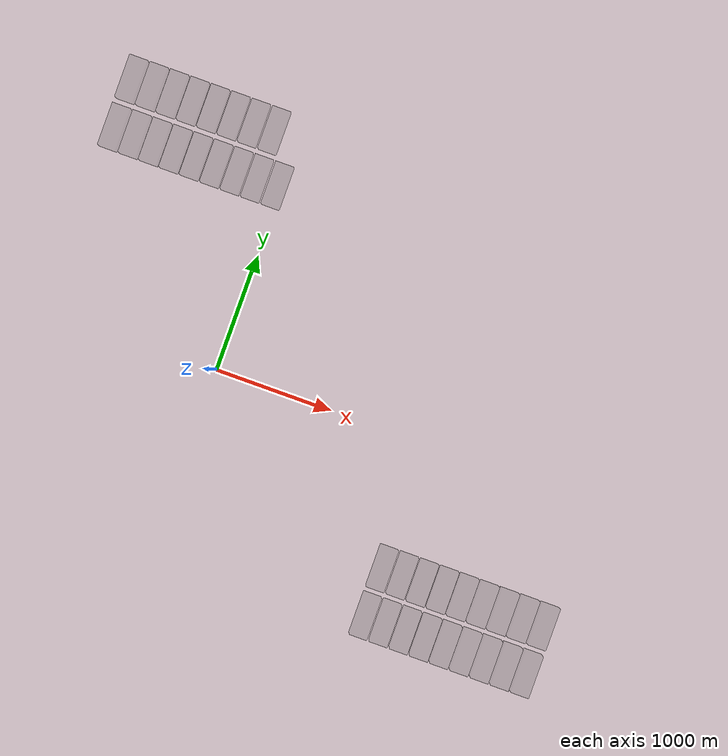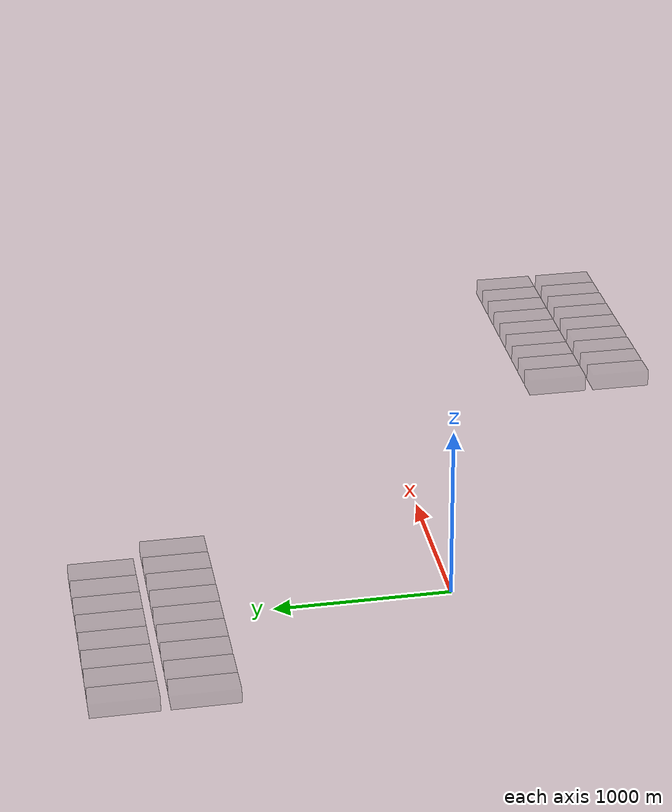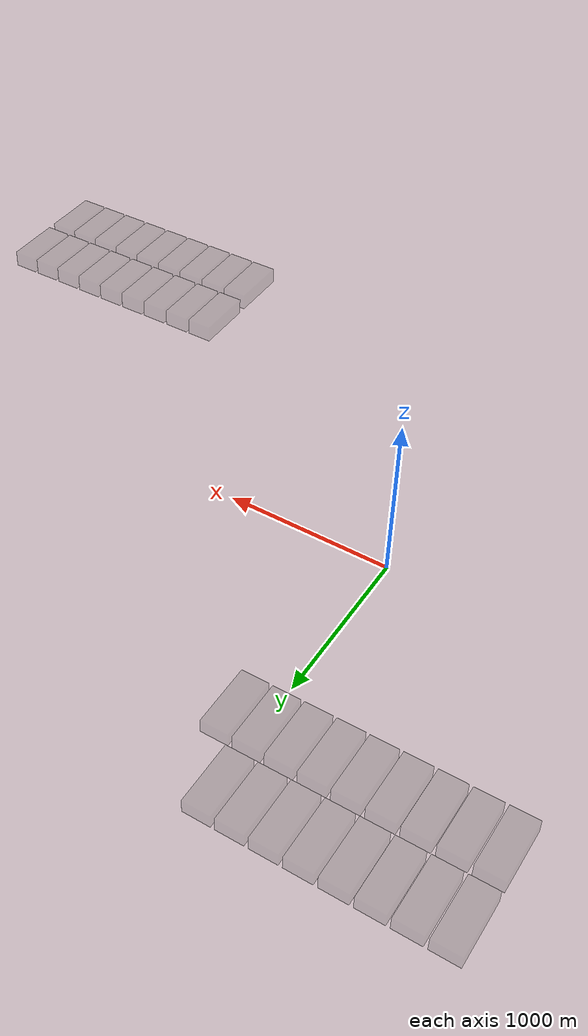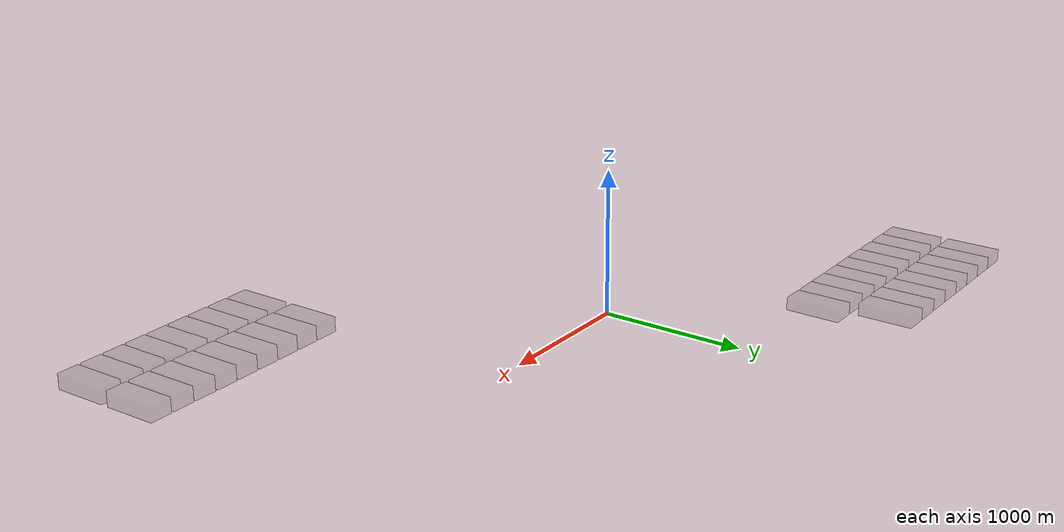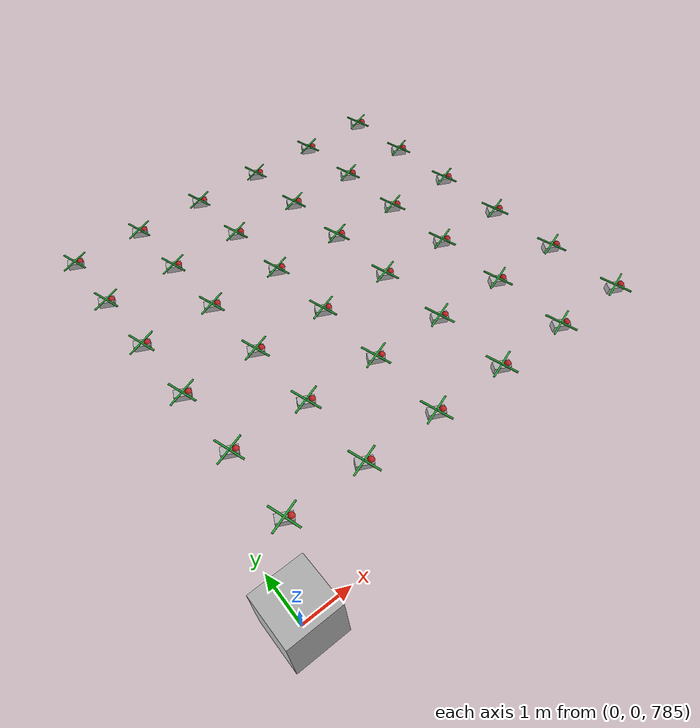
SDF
<sdf version="1.5">
 <world name="default">
  <spherical_coordinates>
   <latitude_deg>35.7753</latitude_deg>
   <longitude_deg>-120.774</longitude_deg>
   <elevation>208</elevation>
   <heading_deg>0</heading_deg>
   <surface_model>EARTH_WGS84</surface_model>
  </spherical_coordinates>
  <scene><shadows>0</shadows><ambient>0.4 0.4 0.4 1</ambient><background>0.7 0.7 0.7 1</background></scene>
  <light name="sun" type="directional">
   <pose>0 0 10 0 -0 0</pose>
   <diffuse>0.8 0.8 0.8 1</diffuse>
   <specular>0.2 0.2 0.2 1</specular>
   <attenuation>
    <range>1000</range>
    <constant>0.9</constant>
    <linear>0.01</linear>
    <quadratic>0.001</quadratic>
   </attenuation>
   <direction>-0.5 0.1 -0.9</direction>
  </light>
  <physics name="default_physics" default="0" type="ode">
   <ode>
    <solver>
     <type>world</type>
     <iters>50</iters>
     <sor>1.3</sor>
     <use_dynamic_moi_rescaling>0</use_dynamic_moi_rescaling>
    </solver>
    <constraints>
     <cfm>0</cfm>
     <erp>0.2</erp>
     <contact_max_correcting_vel>100</contact_max_correcting_vel>
     <contact_surface_layer>0.001</contact_surface_layer>
    </constraints>
   </ode>
   <max_step_size>0.01</max_step_size>
   <real_time_update_rate>100</real_time_update_rate>
   <real_time_factor>1</real_time_factor>
   <gravity>0 0 -9.8</gravity>
   <magnetic_field>6e-06 2.3e-05 -4.2e-05</magnetic_field>
  </physics>
  <plugin name="swarm_broker" filename="libSwarmBrokerPlugin.so">
   <comms_model>
    <neighbor_distance_min>0.0</neighbor_distance_min>
    <neighbor_distance_max>250.0</neighbor_distance_max>
    <neighbor_distance_penalty_tree>200.0</neighbor_distance_penalty_tree>
    <comms_distance_min>0.0</comms_distance_min>
    <comms_distance_max>250.0</comms_distance_max>
    <comms_distance_penalty_tree>200.0</comms_distance_penalty_tree>
    <comms_drop_probability_min>0.0</comms_drop_probability_min>
    <comms_drop_probability_max>0.05</comms_drop_probability_max>
    <comms_outage_probability>0.1</comms_outage_probability>
    <comms_outage_duration_min>1.0</comms_outage_duration_min>
    <comms_outage_duration_max>2.0</comms_outage_duration_max>
    <comms_data_rate_max>54000000</comms_data_rate_max>
   </comms_model>
  </plugin>
  <model name="lost_person">
   <pose>999.144 1001.19 651.982 -0.062539 -0.184761 0.006763</pose>
   <link name="link">
    <sensor name="gps" type="gps"><always_on>1</always_on></sensor>
    <kinematic>1</kinematic>
    <collision name="collision">
     <geometry><box><size>1 1 1</size></box></geometry>
     <surface><friction><ode><mu>0</mu><mu2>0</mu2></ode></friction></surface>
    </collision>
    <visual name="visual"><geometry><box><size>1 1 1</size></box></geometry></visual>
    <visual name="visual_ul">
     <pose>0.5 0.5 0.5 0 -0 0</pose>
     <geometry><sphere><radius>0.04</radius></sphere></geometry>
     <material><script><name>Gazebo/Red</name><uri>__default__</uri></script></material>
    </visual>
    <visual name="visual_ur">
     <pose>0.5 -0.5 0.5 0 -0 0</pose>
     <geometry><sphere><radius>0.04</radius></sphere></geometry>
     <material><script><name>Gazebo/Green</name><uri>__default__</uri></script></material>
    </visual>
    <visual name="visual_lr">
     <pose>-0.5 -0.5 0.5 0 -0 0</pose>
     <geometry><sphere><radius>0.04</radius></sphere></geometry>
     <material><script><name>Gazebo/Blue</name><uri>__default__</uri></script></material>
    </visual>
    <visual name="visual_ll">
     <pose>-0.5 0.5 0.5 0 -0 0</pose>
     <geometry><sphere><radius>0.04</radius></sphere></geometry>
     <material><script><name>Gazebo/Yellow</name><uri>__default__</uri></script></material>
    </visual>
    <inertial>
     <inertia><ixx>1</ixx><ixy>0</ixy><ixz>0</ixz><iyy>1</iyy><iyz>0</iyz><izz>1</izz></inertia>
     <mass>1</mass>
    </inertial>
   </link>
   <plugin name="random" filename="libLostPersonControllerPlugin.so">
    <initial_velocity>0 0.2 0</initial_velocity>
    <velocity_factor>0.5</velocity_factor>
    <update_period>10</update_period>
    <gps>link::gps</gps>
    <swarm_search_area>
     <min_relative_latitude_deg>-0.01</min_relative_latitude_deg>
     <max_relative_latitude_deg>0.01</max_relative_latitude_deg>
     <min_relative_longitude_deg>-0.01</min_relative_longitude_deg>
     <max_relative_longitude_deg>0.01</max_relative_longitude_deg>
    </swarm_search_area>
   </plugin>
  </model>
  <model name="boo">
   <pose>0 0 785.866 -0.185171 0 0</pose>
   <static>1</static>
   <link name="link">
    <kinematic>1</kinematic>
    <collision name="collision">
     <geometry><box><size>1 1 1</size></box></geometry>
     <surface><friction><ode><mu>0</mu><mu2>0</mu2></ode></friction></surface>
    </collision>
    <visual name="visual"><geometry><box><size>1 1 1</size></box></geometry></visual>
   </link>
   <plugin name="boo" filename="libBooControllerPlugin.so">
    <lost_person_model>lost_person</lost_person_model>
    <address>boo</address>
    <type>boo</type>
    <swarm_search_area>
     <min_relative_latitude_deg>-0.01</min_relative_latitude_deg>
     <max_relative_latitude_deg>0.01</max_relative_latitude_deg>
     <min_relative_longitude_deg>-0.01</min_relative_longitude_deg>
     <max_relative_longitude_deg>0.01</max_relative_longitude_deg>
    </swarm_search_area>
   </plugin>
  </model>
  <model name="building_group1_0">
   <pose>0 1535 425 0 -0 0</pose>
   <static>1</static>
   <link name="link">
    <visual name="visual">
     <geometry><box><size>150 350 80</size></box></geometry>
     <material><ambient>0.2 0.2 0.2 0.2</ambient><diffuse>0.2 0.2 0.2 0.2</diffuse></material>
    </visual>
    <collision name="collision"><geometry><box><size>150 350 80</size></box></geometry></collision>
   </link>
  </model>
  <model name="building_group1_1">
   <pose>-170 1535 425 0 -0 0</pose>
   <static>1</static>
   <link name="link">
    <visual name="visual">
     <geometry><box><size>150 350 80</size></box></geometry>
     <material><ambient>0.2 0.2 0.2 0.2</ambient><diffuse>0.2 0.2 0.2 0.2</diffuse></material>
    </visual>
    <collision name="collision"><geometry><box><size>150 350 80</size></box></geometry></collision>
   </link>
  </model>
  <model name="building_group1_2">
   <pose>-340 1535 425 0 -0 0</pose>
   <static>1</static>
   <link name="link">
    <visual name="visual">
     <geometry><box><size>150 350 80</size></box></geometry>
     <material><ambient>0.2 0.2 0.2 0.2</ambient><diffuse>0.2 0.2 0.2 0.2</diffuse></material>
    </visual>
    <collision name="collision"><geometry><box><size>150 350 80</size></box></geometry></collision>
   </link>
  </model>
  <model name="building_group1_3">
   <pose>-510 1535 425 0 -0 0</pose>
   <static>1</static>
   <link name="link">
    <visual name="visual">
     <geometry><box><size>150 350 80</size></box></geometry>
     <material><ambient>0.2 0.2 0.2 0.2</ambient><diffuse>0.2 0.2 0.2 0.2</diffuse></material>
    </visual>
    <collision name="collision"><geometry><box><size>150 350 80</size></box></geometry></collision>
   </link>
  </model>
  <model name="building_group1_4">
   <pose>-680 1535 425 0 -0 0</pose>
   <static>1</static>
   <link name="link">
    <visual name="visual">
     <geometry><box><size>150 350 80</size></box></geometry>
     <material><ambient>0.2 0.2 0.2 0.2</ambient><diffuse>0.2 0.2 0.2 0.2</diffuse></material>
    </visual>
    <collision name="collision"><geometry><box><size>150 350 80</size></box></geometry></collision>
   </link>
  </model>
  <model name="building_group1_5">
   <pose>-850 1535 425 0 -0 0</pose>
   <static>1</static>
   <link name="link">
    <visual name="visual">
     <geometry><box><size>150 350 80</size></box></geometry>
     <material><ambient>0.2 0.2 0.2 0.2</ambient><diffuse>0.2 0.2 0.2 0.2</diffuse></material>
    </visual>
    <collision name="collision"><geometry><box><size>150 350 80</size></box></geometry></collision>
   </link>
  </model>
  <model name="building_group1_6">
   <pose>-1020 1535 425 0 -0 0</pose>
   <static>1</static>
   <link name="link">
    <visual name="visual">
     <geometry><box><size>150 350 80</size></box></geometry>
     <material><ambient>0.2 0.2 0.2 0.2</ambient><diffuse>0.2 0.2 0.2 0.2</diffuse></material>
    </visual>
    <collision name="collision"><geometry><box><size>150 350 80</size></box></geometry></collision>
   </link>
  </model>
  <model name="building_group1_7">
   <pose>-1190 1535 425 0 -0 0</pose>
   <static>1</static>
   <link name="link">
    <visual name="visual">
     <geometry><box><size>150 350 80</size></box></geometry>
     <material><ambient>0.2 0.2 0.2 0.2</ambient><diffuse>0.2 0.2 0.2 0.2</diffuse></material>
    </visual>
    <collision name="collision"><geometry><box><size>150 350 80</size></box></geometry></collision>
   </link>
  </model>
  <model name="building_group1_8">
   <pose>-1360 1535 425 0 -0 0</pose>
   <static>1</static>
   <link name="link">
    <visual name="visual">
     <geometry><box><size>150 350 80</size></box></geometry>
     <material><ambient>0.2 0.2 0.2 0.2</ambient><diffuse>0.2 0.2 0.2 0.2</diffuse></material>
    </visual>
    <collision name="collision"><geometry><box><size>150 350 80</size></box></geometry></collision>
   </link>
  </model>
  <model name="building_group1_8">
   <pose>-1360 1535 425 0 -0 0</pose>
   <static>1</static>
   <link name="link">
    <visual name="visual">
     <geometry><box><size>150 350 80</size></box></geometry>
     <material><ambient>0.2 0.2 0.2 0.2</ambient><diffuse>0.2 0.2 0.2 0.2</diffuse></material>
    </visual>
    <collision name="collision"><geometry><box><size>150 350 80</size></box></geometry></collision>
   </link>
  </model>
  <model name="building_group1_9">
   <pose>-170 1935 425 0 -0 0</pose>
   <static>1</static>
   <link name="link">
    <visual name="visual">
     <geometry><box><size>150 350 80</size></box></geometry>
     <material><ambient>0.2 0.2 0.2 0.2</ambient><diffuse>0.2 0.2 0.2 0.2</diffuse></material>
    </visual>
    <collision name="collision"><geometry><box><size>150 350 80</size></box></geometry></collision>
   </link>
  </model>
  <model name="building_group1_10">
   <pose>-340 1935 425 0 -0 0</pose>
   <static>1</static>
   <link name="link">
    <visual name="visual">
     <geometry><box><size>150 350 80</size></box></geometry>
     <material><ambient>0.2 0.2 0.2 0.2</ambient><diffuse>0.2 0.2 0.2 0.2</diffuse></material>
    </visual>
    <collision name="collision"><geometry><box><size>150 350 80</size></box></geometry></collision>
   </link>
  </model>
  <model name="building_group1_11">
   <pose>-510 1935 425 0 -0 0</pose>
   <static>1</static>
   <link name="link">
    <visual name="visual">
     <geometry><box><size>150 350 80</size></box></geometry>
     <material><ambient>0.2 0.2 0.2 0.2</ambient><diffuse>0.2 0.2 0.2 0.2</diffuse></material>
    </visual>
    <collision name="collision"><geometry><box><size>150 350 80</size></box></geometry></collision>
   </link>
  </model>
  <model name="building_group1_12">
   <pose>-680 1935 425 0 -0 0</pose>
   <static>1</static>
   <link name="link">
    <visual name="visual">
     <geometry><box><size>150 350 80</size></box></geometry>
     <material><ambient>0.2 0.2 0.2 0.2</ambient><diffuse>0.2 0.2 0.2 0.2</diffuse></material>
    </visual>
    <collision name="collision"><geometry><box><size>150 350 80</size></box></geometry></collision>
   </link>
  </model>
  <model name="building_group1_13">
   <pose>-850 1935 425 0 -0 0</pose>
   <static>1</static>
   <link name="link">
    <visual name="visual">
     <geometry><box><size>150 350 80</size></box></geometry>
     <material><ambient>0.2 0.2 0.2 0.2</ambient><diffuse>0.2 0.2 0.2 0.2</diffuse></material>
    </visual>
    <collision name="collision"><geometry><box><size>150 350 80</size></box></geometry></collision>
   </link>
  </model>
  <model name="building_group1_14">
   <pose>-1020 1935 425 0 -0 0</pose>
   <static>1</static>
   <link name="link">
    <visual name="visual">
     <geometry><box><size>150 350 80</size></box></geometry>
     <material><ambient>0.2 0.2 0.2 0.2</ambient><diffuse>0.2 0.2 0.2 0.2</diffuse></material>
    </visual>
    <collision name="collision"><geometry><box><size>150 350 80</size></box></geometry></collision>
   </link>
  </model>
  <model name="building_group1_15">
   <pose>-1190 1935 425 0 -0 0</pose>
   <static>1</static>
   <link name="link">
    <visual name="visual">
     <geometry><box><size>150 350 80</size></box></geometry>
     <material><ambient>0.2 0.2 0.2 0.2</ambient><diffuse>0.2 0.2 0.2 0.2</diffuse></material>
    </visual>
    <collision name="collision"><geometry><box><size>150 350 80</size></box></geometry></collision>
   </link>
  </model>
  <model name="building_group1_16">
   <pose>-1360 1935 425 0 -0 0</pose>
   <static>1</static>
   <link name="link">
    <visual name="visual">
     <geometry><box><size>150 350 80</size></box></geometry>
     <material><ambient>0.2 0.2 0.2 0.2</ambient><diffuse>0.2 0.2 0.2 0.2</diffuse></material>
    </visual>
    <collision name="collision"><geometry><box><size>150 350 80</size></box></geometry></collision>
   </link>
  </model>
  <model name="building_group2_0">
   <pose>1800 -1030 330 0 -0 0</pose>
   <static>1</static>
   <link name="link">
    <visual name="visual">
     <geometry><box><size>150 350 100</size></box></geometry>
     <material><ambient>0.2 0.2 0.2 0.2</ambient><diffuse>0.2 0.2 0.2 0.2</diffuse></material>
    </visual>
    <collision name="collision"><geometry><box><size>150 350 80</size></box></geometry></collision>
   </link>
  </model>
  <model name="building_group2_1">
   <pose>1970 -1030 330 0 -0 0</pose>
   <static>1</static>
   <link name="link">
    <visual name="visual">
     <geometry><box><size>150 350 100</size></box></geometry>
     <material><ambient>0.2 0.2 0.2 0.2</ambient><diffuse>0.2 0.2 0.2 0.2</diffuse></material>
    </visual>
    <collision name="collision"><geometry><box><size>150 350 80</size></box></geometry></collision>
   </link>
  </model>
  <model name="building_group2_2">
   <pose>2140 -1030 330 0 -0 0</pose>
   <static>1</static>
   <link name="link">
    <visual name="visual">
     <geometry><box><size>150 350 100</size></box></geometry>
     <material><ambient>0.2 0.2 0.2 0.2</ambient><diffuse>0.2 0.2 0.2 0.2</diffuse></material>
    </visual>
    <collision name="collision"><geometry><box><size>150 350 80</size></box></geometry></collision>
   </link>
  </model>
  <model name="building_group2_3">
   <pose>2310 -1030 330 0 -0 0</pose>
   <static>1</static>
   <link name="link">
    <visual name="visual">
     <geometry><box><size>150 350 100</size></box></geometry>
     <material><ambient>0.2 0.2 0.2 0.2</ambient><diffuse>0.2 0.2 0.2 0.2</diffuse></material>
    </visual>
    <collision name="collision"><geometry><box><size>150 350 80</size></box></geometry></collision>
   </link>
  </model>
  <model name="building_group2_4">
   <pose>2480 -1030 330 0 -0 0</pose>
   <static>1</static>
   <link name="link">
    <visual name="visual">
     <geometry><box><size>150 350 100</size></box></geometry>
     <material><ambient>0.2 0.2 0.2 0.2</ambient><diffuse>0.2 0.2 0.2 0.2</diffuse></material>
    </visual>
    <collision name="collision"><geometry><box><size>150 350 80</size></box></geometry></collision>
   </link>
  </model>
  <model name="building_group2_5">
   <pose>2650 -1030 330 0 -0 0</pose>
   <static>1</static>
   <link name="link">
    <visual name="visual">
     <geometry><box><size>150 350 100</size></box></geometry>
     <material><ambient>0.2 0.2 0.2 0.2</ambient><diffuse>0.2 0.2 0.2 0.2</diffuse></material>
    </visual>
    <collision name="collision"><geometry><box><size>150 350 80</size></box></geometry></collision>
   </link>
  </model>
  <model name="building_group2_6">
   <pose>2820 -1030 330 0 -0 0</pose>
   <static>1</static>
   <link name="link">
    <visual name="visual">
     <geometry><box><size>150 350 100</size></box></geometry>
     <material><ambient>0.2 0.2 0.2 0.2</ambient><diffuse>0.2 0.2 0.2 0.2</diffuse></material>
    </visual>
    <collision name="collision"><geometry><box><size>150 350 80</size></box></geometry></collision>
   </link>
  </model>
  <model name="building_group2_7">
   <pose>2990 -1030 330 0 -0 0</pose>
   <static>1</static>
   <link name="link">
    <visual name="visual">
     <geometry><box><size>150 350 100</size></box></geometry>
     <material><ambient>0.2 0.2 0.2 0.2</ambient><diffuse>0.2 0.2 0.2 0.2</diffuse></material>
    </visual>
    <collision name="collision"><geometry><box><size>150 350 80</size></box></geometry></collision>
   </link>
  </model>
  <model name="building_group2_8">
   <pose>3160 -1030 330 0 -0 0</pose>
   <static>1</static>
   <link name="link">
    <visual name="visual">
     <geometry><box><size>150 350 100</size></box></geometry>
     <material><ambient>0.2 0.2 0.2 0.2</ambient><diffuse>0.2 0.2 0.2 0.2</diffuse></material>
    </visual>
    <collision name="collision"><geometry><box><size>150 350 80</size></box></geometry></collision>
   </link>
  </model>
  <model name="building_group2_10">
   <pose>1800 -1430 330 0 -0 0</pose>
   <static>1</static>
   <link name="link">
    <visual name="visual">
     <geometry><box><size>150 350 100</size></box></geometry>
     <material><ambient>0.2 0.2 0.2 0.2</ambient><diffuse>0.2 0.2 0.2 0.2</diffuse></material>
    </visual>
    <collision name="collision"><geometry><box><size>150 350 80</size></box></geometry></collision>
   </link>
  </model>
  <model name="building_group2_11">
   <pose>1970 -1430 330 0 -0 0</pose>
   <static>1</static>
   <link name="link">
    <visual name="visual">
     <geometry><box><size>150 350 100</size></box></geometry>
     <material><ambient>0.2 0.2 0.2 0.2</ambient><diffuse>0.2 0.2 0.2 0.2</diffuse></material>
    </visual>
    <collision name="collision"><geometry><box><size>150 350 80</size></box></geometry></collision>
   </link>
  </model>
  <model name="building_group2_12">
   <pose>2140 -1430 330 0 -0 0</pose>
   <static>1</static>
   <link name="link">
    <visual name="visual">
     <geometry><box><size>150 350 100</size></box></geometry>
     <material><ambient>0.2 0.2 0.2 0.2</ambient><diffuse>0.2 0.2 0.2 0.2</diffuse></material>
    </visual>
    <collision name="collision"><geometry><box><size>150 350 80</size></box></geometry></collision>
   </link>
  </model>
  <model name="building_group2_13">
   <pose>2310 -1430 330 0 -0 0</pose>
   <static>1</static>
   <link name="link">
    <visual name="visual">
     <geometry><box><size>150 350 100</size></box></geometry>
     <material><ambient>0.2 0.2 0.2 0.2</ambient><diffuse>0.2 0.2 0.2 0.2</diffuse></material>
    </visual>
    <collision name="collision"><geometry><box><size>150 350 80</size></box></geometry></collision>
   </link>
  </model>
  <model name="building_group2_14">
   <pose>2480 -1430 330 0 -0 0</pose>
   <static>1</static>
   <link name="link">
    <visual name="visual">
     <geometry><box><size>150 350 100</size></box></geometry>
     <material><ambient>0.2 0.2 0.2 0.2</ambient><diffuse>0.2 0.2 0.2 0.2</diffuse></material>
    </visual>
    <collision name="collision"><geometry><box><size>150 350 80</size></box></geometry></collision>
   </link>
  </model>
  <model name="building_group2_15">
   <pose>2650 -1430 330 0 -0 0</pose>
   <static>1</static>
   <link name="link">
    <visual name="visual">
     <geometry><box><size>150 350 100</size></box></geometry>
     <material><ambient>0.2 0.2 0.2 0.2</ambient><diffuse>0.2 0.2 0.2 0.2</diffuse></material>
    </visual>
    <collision name="collision"><geometry><box><size>150 350 80</size></box></geometry></collision>
   </link>
  </model>
  <model name="building_group2_16">
   <pose>2820 -1430 330 0 -0 0</pose>
   <static>1</static>
   <link name="link">
    <visual name="visual">
     <geometry><box><size>150 350 100</size></box></geometry>
     <material><ambient>0.2 0.2 0.2 0.2</ambient><diffuse>0.2 0.2 0.2 0.2</diffuse></material>
    </visual>
    <collision name="collision"><geometry><box><size>150 350 80</size></box></geometry></collision>
   </link>
  </model>
  <model name="building_group2_17">
   <pose>2990 -1430 330 0 -0 0</pose>
   <static>1</static>
   <link name="link">
    <visual name="visual">
     <geometry><box><size>150 350 100</size></box></geometry>
     <material><ambient>0.2 0.2 0.2 0.2</ambient><diffuse>0.2 0.2 0.2 0.2</diffuse></material>
    </visual>
    <collision name="collision"><geometry><box><size>150 350 80</size></box></geometry></collision>
   </link>
  </model>
  <model name="building_group2_18">
   <pose>3160 -1430 330 0 -0 0</pose>
   <static>1</static>
   <link name="link">
    <visual name="visual">
     <geometry><box><size>150 350 100</size></box></geometry>
     <material><ambient>0.2 0.2 0.2 0.2</ambient><diffuse>0.2 0.2 0.2 0.2</diffuse></material>
    </visual>
    <collision name="collision"><geometry><box><size>150 350 80</size></box></geometry></collision>
   </link>
  </model>
  <model name="rotor_0">
   <pose>0 0 789.936 0 0 -0.452</pose>
   <link name="link">
    <sensor name="gps" type="gps">
     <gps>
      <position_sensing>
       <horizontal>
        <noise type="gaussian_quantized">
         <mean>0</mean>
         <stddev>4</stddev>
         <bias_mean>0</bias_mean>
         <bias_stddev>0</bias_stddev>
         <precision>0.001</precision>
        </noise>
       </horizontal>
       <vertical>
        <noise type="gaussian_quantized">
         <mean>0</mean>
         <stddev>8</stddev>
         <bias_mean>0</bias_mean>
         <bias_stddev>0</bias_stddev>
         <precision>0.01</precision>
        </noise>
       </vertical>
      </position_sensing>
      <velocity_sensing>
       <horizontal>
        <noise type="gaussian_quantized">
         <mean>0</mean>
         <stddev>4</stddev>
         <bias_mean>0</bias_mean>
         <bias_stddev>0</bias_stddev>
         <precision>0.001</precision>
        </noise>
       </horizontal>
       <vertical>
        <noise type="gaussian_quantized">
         <mean>0</mean>
         <stddev>8</stddev>
         <bias_mean>0</bias_mean>
         <bias_stddev>0</bias_stddev>
         <precision>0.01</precision>
        </noise>
       </vertical>
      </velocity_sensing>
     </gps>
     <always_on>1</always_on>
    </sensor>
    <sensor name="imu" type="imu">
     <imu>
      <angular_velocity>
       <x>
        <noise type="gaussian">
         <mean>0</mean>
         <stddev>0.0002</stddev>
         <bias_mean>7.5e-06</bias_mean>
         <bias_stddev>8e-07</bias_stddev>
        </noise>
       </x>
       <y>
        <noise type="gaussian">
         <mean>0</mean>
         <stddev>0.0002</stddev>
         <bias_mean>7.5e-06</bias_mean>
         <bias_stddev>8e-07</bias_stddev>
        </noise>
       </y>
       <z>
        <noise type="gaussian">
         <mean>0</mean>
         <stddev>0.0002</stddev>
         <bias_mean>7.5e-06</bias_mean>
         <bias_stddev>8e-07</bias_stddev>
        </noise>
       </z>
      </angular_velocity>
      <linear_acceleration>
       <x>
        <noise type="gaussian">
         <mean>0</mean>
         <stddev>0.0002</stddev>
         <bias_mean>7.5e-06</bias_mean>
         <bias_stddev>8e-07</bias_stddev>
        </noise>
       </x>
       <y>
        <noise type="gaussian">
         <mean>0</mean>
         <stddev>0.0002</stddev>
         <bias_mean>7.5e-06</bias_mean>
         <bias_stddev>8e-07</bias_stddev>
        </noise>
       </y>
       <z>
        <noise type="gaussian">
         <mean>0</mean>
         <stddev>0.0002</stddev>
         <bias_mean>7.5e-06</bias_mean>
         <bias_stddev>8e-07</bias_stddev>
        </noise>
       </z>
      </linear_acceleration>
     </imu>
     <always_on>1</always_on>
    </sensor>
    <sensor name="camera" type="logical_camera">
     <logical_camera>
      <near>0.1</near>
      <far>50</far>
      <horizontal_fov>1.4656</horizontal_fov>
      <aspect_ratio>1.778</aspect_ratio>
     </logical_camera>
     <visualize>0</visualize>
     <always_on>1</always_on>
    </sensor>
    <kinematic>1</kinematic>
    <gravity>0</gravity>
    <collision name="collision"><geometry><box><size>0.2 0.1 0.1</size></box></geometry></collision>
    <visual name="visual"><geometry><box><size>0.2 0.1 0.1</size></box></geometry></visual>
    <visual name="visual_front">
     <pose>0.07 0 0.04 0 -0 0</pose>
     <geometry><sphere><radius>0.04</radius></sphere></geometry>
     <material><script><name>Gazebo/Red</name><uri>__default__</uri></script></material>
    </visual>
    <visual name="visual_blade1">
     <pose>0 0 0.055 0 -0 0.78539</pose>
     <geometry><box><size>0.4 0.02 0.01</size></box></geometry>
     <material><script><name>Gazebo/Green</name><uri>__default__</uri></script></material>
    </visual>
    <visual name="visual_blade2">
     <pose>0 0 0.055 0 -0 2.3562</pose>
     <geometry><box><size>0.4 0.02 0.01</size></box></geometry>
     <material><script><name>Gazebo/Green</name><uri>__default__</uri></script></material>
    </visual>
    <inertial>
     <inertia><ixx>1</ixx><ixy>0</ixy><ixz>0</ixz><iyy>1</iyy><iyz>0</iyz><izz>1</izz></inertia>
     <mass>1</mass>
    </inertial>
   </link>
   <plugin name="swarm_controller_rotor_0" filename="libTeamControllerPlugin.so">
    <type>rotor</type>
    <camera>link::camera</camera>
    <gps>link::gps</gps>
    <imu>link::imu</imu>
    <address>192.168.1.1</address>
    <num_messages>1</num_messages>
    <swarm_search_area>
     <min_relative_latitude_deg>-0.01</min_relative_latitude_deg>
     <max_relative_latitude_deg>0.01</max_relative_latitude_deg>
     <min_relative_longitude_deg>-0.01</min_relative_longitude_deg>
     <max_relative_longitude_deg>0.01</max_relative_longitude_deg>
    </swarm_search_area>
    <battery>
     <capacity>3500</capacity>
     <consumption>1500</consumption>
     <consumption_factor>0.8</consumption_factor>
    </battery>
   </plugin>
  </model>
  <model name="rotor_1">
   <pose>1 0 789.873 0 0 -0.452</pose>
   <link name="link">
    <sensor name="gps" type="gps">
     <gps>
      <position_sensing>
       <horizontal>
        <noise type="gaussian_quantized">
         <mean>0</mean>
         <stddev>4</stddev>
         <bias_mean>0</bias_mean>
         <bias_stddev>0</bias_stddev>
         <precision>0.001</precision>
        </noise>
       </horizontal>
       <vertical>
        <noise type="gaussian_quantized">
         <mean>0</mean>
         <stddev>8</stddev>
         <bias_mean>0</bias_mean>
         <bias_stddev>0</bias_stddev>
         <precision>0.01</precision>
        </noise>
       </vertical>
      </position_sensing>
      <velocity_sensing>
       <horizontal>
        <noise type="gaussian_quantized">
         <mean>0</mean>
         <stddev>4</stddev>
         <bias_mean>0</bias_mean>
         <bias_stddev>0</bias_stddev>
         <precision>0.001</precision>
        </noise>
       </horizontal>
       <vertical>
        <noise type="gaussian_quantized">
         <mean>0</mean>
         <stddev>8</stddev>
         <bias_mean>0</bias_mean>
         <bias_stddev>0</bias_stddev>
         <precision>0.01</precision>
        </noise>
       </vertical>
      </velocity_sensing>
     </gps>
     <always_on>1</always_on>
    </sensor>
    <sensor name="imu" type="imu">
     <imu>
      <angular_velocity>
       <x>
        <noise type="gaussian">
         <mean>0</mean>
         <stddev>0.0002</stddev>
         <bias_mean>7.5e-06</bias_mean>
         <bias_stddev>8e-07</bias_stddev>
        </noise>
       </x>
       <y>
        <noise type="gaussian">
         <mean>0</mean>
         <stddev>0.0002</stddev>
         <bias_mean>7.5e-06</bias_mean>
         <bias_stddev>8e-07</bias_stddev>
        </noise>
       </y>
       <z>
        <noise type="gaussian">
         <mean>0</mean>
         <stddev>0.0002</stddev>
         <bias_mean>7.5e-06</bias_mean>
         <bias_stddev>8e-07</bias_stddev>
        </noise>
       </z>
      </angular_velocity>
      <linear_acceleration>
       <x>
        <noise type="gaussian">
         <mean>0</mean>
         <stddev>0.0002</stddev>
         <bias_mean>7.5e-06</bias_mean>
         <bias_stddev>8e-07</bias_stddev>
        </noise>
       </x>
       <y>
        <noise type="gaussian">
         <mean>0</mean>
         <stddev>0.0002</stddev>
         <bias_mean>7.5e-06</bias_mean>
         <bias_stddev>8e-07</bias_stddev>
        </noise>
       </y>
       <z>
        <noise type="gaussian">
         <mean>0</mean>
         <stddev>0.0002</stddev>
         <bias_mean>7.5e-06</bias_mean>
         <bias_stddev>8e-07</bias_stddev>
        </noise>
       </z>
      </linear_acceleration>
     </imu>
     <always_on>1</always_on>
    </sensor>
    <sensor name="camera" type="logical_camera">
     <logical_camera>
      <near>0.1</near>
      <far>50</far>
      <horizontal_fov>1.4656</horizontal_fov>
      <aspect_ratio>1.778</aspect_ratio>
     </logical_camera>
     <visualize>0</visualize>
     <always_on>1</always_on>
    </sensor>
    <kinematic>1</kinematic>
    <gravity>0</gravity>
    <collision name="collision"><geometry><box><size>0.2 0.1 0.1</size></box></geometry></collision>
    <visual name="visual"><geometry><box><size>0.2 0.1 0.1</size></box></geometry></visual>
    <visual name="visual_front">
     <pose>0.07 0 0.04 0 -0 0</pose>
     <geometry><sphere><radius>0.04</radius></sphere></geometry>
     <material><script><name>Gazebo/Red</name><uri>__default__</uri></script></material>
    </visual>
    <visual name="visual_blade1">
     <pose>0 0 0.055 0 -0 0.78539</pose>
     <geometry><box><size>0.4 0.02 0.01</size></box></geometry>
     <material><script><name>Gazebo/Green</name><uri>__default__</uri></script></material>
    </visual>
    <visual name="visual_blade2">
     <pose>0 0 0.055 0 -0 2.3562</pose>
     <geometry><box><size>0.4 0.02 0.01</size></box></geometry>
     <material><script><name>Gazebo/Green</name><uri>__default__</uri></script></material>
    </visual>
    <inertial>
     <inertia><ixx>1</ixx><ixy>0</ixy><ixz>0</ixz><iyy>1</iyy><iyz>0</iyz><izz>1</izz></inertia>
     <mass>1</mass>
    </inertial>
   </link>
   <plugin name="swarm_controller_rotor_1" filename="libTeamControllerPlugin.so">
    <type>rotor</type>
    <camera>link::camera</camera>
    <gps>link::gps</gps>
    <imu>link::imu</imu>
    <address>192.168.1.2</address>
    <num_messages>1</num_messages>
    <swarm_search_area>
     <min_relative_latitude_deg>-0.01</min_relative_latitude_deg>
     <max_relative_latitude_deg>0.01</max_relative_latitude_deg>
     <min_relative_longitude_deg>-0.01</min_relative_longitude_deg>
     <max_relative_longitude_deg>0.01</max_relative_longitude_deg>
    </swarm_search_area>
    <battery>
     <capacity>3500</capacity>
     <consumption>1500</consumption>
     <consumption_factor>0.8</consumption_factor>
    </battery>
   </plugin>
  </model>
  <model name="rotor_2">
   <pose>2 0 789.811 0 0 -0.452</pose>
   <link name="link">
    <sensor name="gps" type="gps">
     <gps>
      <position_sensing>
       <horizontal>
        <noise type="gaussian_quantized">
         <mean>0</mean>
         <stddev>4</stddev>
         <bias_mean>0</bias_mean>
         <bias_stddev>0</bias_stddev>
         <precision>0.001</precision>
        </noise>
       </horizontal>
       <vertical>
        <noise type="gaussian_quantized">
         <mean>0</mean>
         <stddev>8</stddev>
         <bias_mean>0</bias_mean>
         <bias_stddev>0</bias_stddev>
         <precision>0.01</precision>
        </noise>
       </vertical>
      </position_sensing>
      <velocity_sensing>
       <horizontal>
        <noise type="gaussian_quantized">
         <mean>0</mean>
         <stddev>4</stddev>
         <bias_mean>0</bias_mean>
         <bias_stddev>0</bias_stddev>
         <precision>0.001</precision>
        </noise>
       </horizontal>
       <vertical>
        <noise type="gaussian_quantized">
         <mean>0</mean>
         <stddev>8</stddev>
         <bias_mean>0</bias_mean>
         <bias_stddev>0</bias_stddev>
         <precision>0.01</precision>
        </noise>
       </vertical>
      </velocity_sensing>
     </gps>
     <always_on>1</always_on>
    </sensor>
    <sensor name="imu" type="imu">
     <imu>
      <angular_velocity>
       <x>
        <noise type="gaussian">
         <mean>0</mean>
         <stddev>0.0002</stddev>
         <bias_mean>7.5e-06</bias_mean>
         <bias_stddev>8e-07</bias_stddev>
        </noise>
       </x>
       <y>
        <noise type="gaussian">
         <mean>0</mean>
         <stddev>0.0002</stddev>
         <bias_mean>7.5e-06</bias_mean>
         <bias_stddev>8e-07</bias_stddev>
        </noise>
       </y>
       <z>
        <noise type="gaussian">
         <mean>0</mean>
         <stddev>0.0002</stddev>
         <bias_mean>7.5e-06</bias_mean>
         <bias_stddev>8e-07</bias_stddev>
        </noise>
       </z>
      </angular_velocity>
      <linear_acceleration>
       <x>
        <noise type="gaussian">
         <mean>0</mean>
         <stddev>0.0002</stddev>
         <bias_mean>7.5e-06</bias_mean>
         <bias_stddev>8e-07</bias_stddev>
        </noise>
       </x>
       <y>
        <noise type="gaussian">
         <mean>0</mean>
         <stddev>0.0002</stddev>
         <bias_mean>7.5e-06</bias_mean>
         <bias_stddev>8e-07</bias_stddev>
        </noise>
       </y>
       <z>
        <noise type="gaussian">
         <mean>0</mean>
         <stddev>0.0002</stddev>
         <bias_mean>7.5e-06</bias_mean>
         <bias_stddev>8e-07</bias_stddev>
        </noise>
       </z>
      </linear_acceleration>
     </imu>
     <always_on>1</always_on>
    </sensor>
    <sensor name="camera" type="logical_camera">
     <logical_camera>
      <near>0.1</near>
      <far>50</far>
      <horizontal_fov>1.4656</horizontal_fov>
      <aspect_ratio>1.778</aspect_ratio>
     </logical_camera>
     <visualize>0</visualize>
     <always_on>1</always_on>
    </sensor>
    <kinematic>1</kinematic>
    <gravity>0</gravity>
    <collision name="collision"><geometry><box><size>0.2 0.1 0.1</size></box></geometry></collision>
    <visual name="visual"><geometry><box><size>0.2 0.1 0.1</size></box></geometry></visual>
    <visual name="visual_front">
     <pose>0.07 0 0.04 0 -0 0</pose>
     <geometry><sphere><radius>0.04</radius></sphere></geometry>
     <material><script><name>Gazebo/Red</name><uri>__default__</uri></script></material>
    </visual>
    <visual name="visual_blade1">
     <pose>0 0 0.055 0 -0 0.78539</pose>
     <geometry><box><size>0.4 0.02 0.01</size></box></geometry>
     <material><script><name>Gazebo/Green</name><uri>__default__</uri></script></material>
    </visual>
    <visual name="visual_blade2">
     <pose>0 0 0.055 0 -0 2.3562</pose>
     <geometry><box><size>0.4 0.02 0.01</size></box></geometry>
     <material><script><name>Gazebo/Green</name><uri>__default__</uri></script></material>
    </visual>
    <inertial>
     <inertia><ixx>1</ixx><ixy>0</ixy><ixz>0</ixz><iyy>1</iyy><iyz>0</iyz><izz>1</izz></inertia>
     <mass>1</mass>
    </inertial>
   </link>
   <plugin name="swarm_controller_rotor_2" filename="libTeamControllerPlugin.so">
    <type>rotor</type>
    <camera>link::camera</camera>
    <gps>link::gps</gps>
    <imu>link::imu</imu>
    <address>192.168.1.3</address>
    <num_messages>1</num_messages>
    <swarm_search_area>
     <min_relative_latitude_deg>-0.01</min_relative_latitude_deg>
     <max_relative_latitude_deg>0.01</max_relative_latitude_deg>
     <min_relative_longitude_deg>-0.01</min_relative_longitude_deg>
     <max_relative_longitude_deg>0.01</max_relative_longitude_deg>
    </swarm_search_area>
    <battery>
     <capacity>3500</capacity>
     <consumption>1500</consumption>
     <consumption_factor>0.8</consumption_factor>
    </battery>
   </plugin>
  </model>
  <model name="rotor_3">
   <pose>3 0 789.749 0 0 -0.452</pose>
   <link name="link">
    <sensor name="gps" type="gps">
     <gps>
      <position_sensing>
       <horizontal>
        <noise type="gaussian_quantized">
         <mean>0</mean>
         <stddev>4</stddev>
         <bias_mean>0</bias_mean>
         <bias_stddev>0</bias_stddev>
         <precision>0.001</precision>
        </noise>
       </horizontal>
       <vertical>
        <noise type="gaussian_quantized">
         <mean>0</mean>
         <stddev>8</stddev>
         <bias_mean>0</bias_mean>
         <bias_stddev>0</bias_stddev>
         <precision>0.01</precision>
        </noise>
       </vertical>
      </position_sensing>
      <velocity_sensing>
       <horizontal>
        <noise type="gaussian_quantized">
         <mean>0</mean>
         <stddev>4</stddev>
         <bias_mean>0</bias_mean>
         <bias_stddev>0</bias_stddev>
         <precision>0.001</precision>
        </noise>
       </horizontal>
       <vertical>
        <noise type="gaussian_quantized">
         <mean>0</mean>
         <stddev>8</stddev>
         <bias_mean>0</bias_mean>
         <bias_stddev>0</bias_stddev>
         <precision>0.01</precision>
        </noise>
       </vertical>
      </velocity_sensing>
     </gps>
     <always_on>1</always_on>
    </sensor>
    <sensor name="imu" type="imu">
     <imu>
      <angular_velocity>
       <x>
        <noise type="gaussian">
         <mean>0</mean>
         <stddev>0.0002</stddev>
         <bias_mean>7.5e-06</bias_mean>
         <bias_stddev>8e-07</bias_stddev>
        </noise>
       </x>
       <y>
        <noise type="gaussian">
         <mean>0</mean>
         <stddev>0.0002</stddev>
         <bias_mean>7.5e-06</bias_mean>
         <bias_stddev>8e-07</bias_stddev>
        </noise>
       </y>
       <z>
        <noise type="gaussian">
         <mean>0</mean>
         <stddev>0.0002</stddev>
         <bias_mean>7.5e-06</bias_mean>
         <bias_stddev>8e-07</bias_stddev>
        </noise>
       </z>
      </angular_velocity>
      <linear_acceleration>
       <x>
        <noise type="gaussian">
         <mean>0</mean>
         <stddev>0.0002</stddev>
         <bias_mean>7.5e-06</bias_mean>
         <bias_stddev>8e-07</bias_stddev>
        </noise>
       </x>
       <y>
        <noise type="gaussian">
         <mean>0</mean>
         <stddev>0.0002</stddev>
         <bias_mean>7.5e-06</bias_mean>
         <bias_stddev>8e-07</bias_stddev>
        </noise>
       </y>
       <z>
        <noise type="gaussian">
         <mean>0</mean>
         <stddev>0.0002</stddev>
         <bias_mean>7.5e-06</bias_mean>
         <bias_stddev>8e-07</bias_stddev>
        </noise>
       </z>
      </linear_acceleration>
     </imu>
     <always_on>1</always_on>
    </sensor>
    <sensor name="camera" type="logical_camera">
     <logical_camera>
      <near>0.1</near>
      <far>50</far>
      <horizontal_fov>1.4656</horizontal_fov>
      <aspect_ratio>1.778</aspect_ratio>
     </logical_camera>
     <visualize>0</visualize>
     <always_on>1</always_on>
    </sensor>
    <kinematic>1</kinematic>
    <gravity>0</gravity>
    <collision name="collision"><geometry><box><size>0.2 0.1 0.1</size></box></geometry></collision>
    <visual name="visual"><geometry><box><size>0.2 0.1 0.1</size></box></geometry></visual>
    <visual name="visual_front">
     <pose>0.07 0 0.04 0 -0 0</pose>
     <geometry><sphere><radius>0.04</radius></sphere></geometry>
     <material><script><name>Gazebo/Red</name><uri>__default__</uri></script></material>
    </visual>
    <visual name="visual_blade1">
     <pose>0 0 0.055 0 -0 0.78539</pose>
     <geometry><box><size>0.4 0.02 0.01</size></box></geometry>
     <material><script><name>Gazebo/Green</name><uri>__default__</uri></script></material>
    </visual>
    <visual name="visual_blade2">
     <pose>0 0 0.055 0 -0 2.3562</pose>
     <geometry><box><size>0.4 0.02 0.01</size></box></geometry>
     <material><script><name>Gazebo/Green</name><uri>__default__</uri></script></material>
    </visual>
    <inertial>
     <inertia><ixx>1</ixx><ixy>0</ixy><ixz>0</ixz><iyy>1</iyy><iyz>0</iyz><izz>1</izz></inertia>
     <mass>1</mass>
    </inertial>
   </link>
   <plugin name="swarm_controller_rotor_3" filename="libTeamControllerPlugin.so">
    <type>rotor</type>
    <camera>link::camera</camera>
    <gps>link::gps</gps>
    <imu>link::imu</imu>
    <address>192.168.1.4</address>
    <num_messages>1</num_messages>
    <swarm_search_area>
     <min_relative_latitude_deg>-0.01</min_relative_latitude_deg>
     <max_relative_latitude_deg>0.01</max_relative_latitude_deg>
     <min_relative_longitude_deg>-0.01</min_relative_longitude_deg>
     <max_relative_longitude_deg>0.01</max_relative_longitude_deg>
    </swarm_search_area>
    <battery>
     <capacity>3500</capacity>
     <consumption>1500</consumption>
     <consumption_factor>0.8</consumption_factor>
    </battery>
   </plugin>
  </model>
  <model name="rotor_4">
   <pose>4 0 789.686 0 0 -0.452</pose>
   <link name="link">
    <sensor name="gps" type="gps">
     <gps>
      <position_sensing>
       <horizontal>
        <noise type="gaussian_quantized">
         <mean>0</mean>
         <stddev>4</stddev>
         <bias_mean>0</bias_mean>
         <bias_stddev>0</bias_stddev>
         <precision>0.001</precision>
        </noise>
       </horizontal>
       <vertical>
        <noise type="gaussian_quantized">
         <mean>0</mean>
         <stddev>8</stddev>
         <bias_mean>0</bias_mean>
         <bias_stddev>0</bias_stddev>
         <precision>0.01</precision>
        </noise>
       </vertical>
      </position_sensing>
      <velocity_sensing>
       <horizontal>
        <noise type="gaussian_quantized">
         <mean>0</mean>
         <stddev>4</stddev>
         <bias_mean>0</bias_mean>
         <bias_stddev>0</bias_stddev>
         <precision>0.001</precision>
        </noise>
       </horizontal>
       <vertical>
        <noise type="gaussian_quantized">
         <mean>0</mean>
         <stddev>8</stddev>
         <bias_mean>0</bias_mean>
         <bias_stddev>0</bias_stddev>
         <precision>0.01</precision>
        </noise>
       </vertical>
      </velocity_sensing>
     </gps>
     <always_on>1</always_on>
    </sensor>
    <sensor name="imu" type="imu">
     <imu>
      <angular_velocity>
       <x>
        <noise type="gaussian">
         <mean>0</mean>
         <stddev>0.0002</stddev>
         <bias_mean>7.5e-06</bias_mean>
         <bias_stddev>8e-07</bias_stddev>
        </noise>
       </x>
       <y>
        <noise type="gaussian">
         <mean>0</mean>
         <stddev>0.0002</stddev>
         <bias_mean>7.5e-06</bias_mean>
         <bias_stddev>8e-07</bias_stddev>
        </noise>
       </y>
       <z>
        <noise type="gaussian">
         <mean>0</mean>
         <stddev>0.0002</stddev>
         <bias_mean>7.5e-06</bias_mean>
         <bias_stddev>8e-07</bias_stddev>
        </noise>
       </z>
      </angular_velocity>
      <linear_acceleration>
       <x>
        <noise type="gaussian">
         <mean>0</mean>
         <stddev>0.0002</stddev>
         <bias_mean>7.5e-06</bias_mean>
         <bias_stddev>8e-07</bias_stddev>
        </noise>
       </x>
       <y>
        <noise type="gaussian">
         <mean>0</mean>
         <stddev>0.0002</stddev>
         <bias_mean>7.5e-06</bias_mean>
         <bias_stddev>8e-07</bias_stddev>
        </noise>
       </y>
       <z>
        <noise type="gaussian">
         <mean>0</mean>
         <stddev>0.0002</stddev>
         <bias_mean>7.5e-06</bias_mean>
         <bias_stddev>8e-07</bias_stddev>
        </noise>
       </z>
      </linear_acceleration>
     </imu>
     <always_on>1</always_on>
    </sensor>
    <sensor name="camera" type="logical_camera">
     <logical_camera>
      <near>0.1</near>
      <far>50</far>
      <horizontal_fov>1.4656</horizontal_fov>
      <aspect_ratio>1.778</aspect_ratio>
     </logical_camera>
     <visualize>0</visualize>
     <always_on>1</always_on>
    </sensor>
    <kinematic>1</kinematic>
    <gravity>0</gravity>
    <collision name="collision"><geometry><box><size>0.2 0.1 0.1</size></box></geometry></collision>
    <visual name="visual"><geometry><box><size>0.2 0.1 0.1</size></box></geometry></visual>
    <visual name="visual_front">
     <pose>0.07 0 0.04 0 -0 0</pose>
     <geometry><sphere><radius>0.04</radius></sphere></geometry>
     <material><script><name>Gazebo/Red</name><uri>__default__</uri></script></material>
    </visual>
    <visual name="visual_blade1">
     <pose>0 0 0.055 0 -0 0.78539</pose>
     <geometry><box><size>0.4 0.02 0.01</size></box></geometry>
     <material><script><name>Gazebo/Green</name><uri>__default__</uri></script></material>
    </visual>
    <visual name="visual_blade2">
     <pose>0 0 0.055 0 -0 2.3562</pose>
     <geometry><box><size>0.4 0.02 0.01</size></box></geometry>
     <material><script><name>Gazebo/Green</name><uri>__default__</uri></script></material>
    </visual>
    <inertial>
     <inertia><ixx>1</ixx><ixy>0</ixy><ixz>0</ixz><iyy>1</iyy><iyz>0</iyz><izz>1</izz></inertia>
     <mass>1</mass>
    </inertial>
   </link>
   <plugin name="swarm_controller_rotor_4" filename="libTeamControllerPlugin.so">
    <type>rotor</type>
    <camera>link::camera</camera>
    <gps>link::gps</gps>
    <imu>link::imu</imu>
    <address>192.168.1.5</address>
    <num_messages>1</num_messages>
    <swarm_search_area>
     <min_relative_latitude_deg>-0.01</min_relative_latitude_deg>
     <max_relative_latitude_deg>0.01</max_relative_latitude_deg>
     <min_relative_longitude_deg>-0.01</min_relative_longitude_deg>
     <max_relative_longitude_deg>0.01</max_relative_longitude_deg>
    </swarm_search_area>
    <battery>
     <capacity>3500</capacity>
     <consumption>1500</consumption>
     <consumption_factor>0.8</consumption_factor>
    </battery>
   </plugin>
  </model>
  <model name="rotor_5">
   <pose>5 0 789.624 0 0 -0.452</pose>
   <link name="link">
    <sensor name="gps" type="gps">
     <gps>
      <position_sensing>
       <horizontal>
        <noise type="gaussian_quantized">
         <mean>0</mean>
         <stddev>4</stddev>
         <bias_mean>0</bias_mean>
         <bias_stddev>0</bias_stddev>
         <precision>0.001</precision>
        </noise>
       </horizontal>
       <vertical>
        <noise type="gaussian_quantized">
         <mean>0</mean>
         <stddev>8</stddev>
         <bias_mean>0</bias_mean>
         <bias_stddev>0</bias_stddev>
         <precision>0.01</precision>
        </noise>
       </vertical>
      </position_sensing>
      <velocity_sensing>
       <horizontal>
        <noise type="gaussian_quantized">
         <mean>0</mean>
         <stddev>4</stddev>
         <bias_mean>0</bias_mean>
         <bias_stddev>0</bias_stddev>
         <precision>0.001</precision>
        </noise>
       </horizontal>
       <vertical>
        <noise type="gaussian_quantized">
         <mean>0</mean>
         <stddev>8</stddev>
         <bias_mean>0</bias_mean>
         <bias_stddev>0</bias_stddev>
         <precision>0.01</precision>
        </noise>
       </vertical>
      </velocity_sensing>
     </gps>
     <always_on>1</always_on>
    </sensor>
    <sensor name="imu" type="imu">
     <imu>
      <angular_velocity>
       <x>
        <noise type="gaussian">
         <mean>0</mean>
         <stddev>0.0002</stddev>
         <bias_mean>7.5e-06</bias_mean>
         <bias_stddev>8e-07</bias_stddev>
        </noise>
       </x>
       <y>
        <noise type="gaussian">
         <mean>0</mean>
         <stddev>0.0002</stddev>
         <bias_mean>7.5e-06</bias_mean>
         <bias_stddev>8e-07</bias_stddev>
        </noise>
       </y>
       <z>
        <noise type="gaussian">
         <mean>0</mean>
         <stddev>0.0002</stddev>
         <bias_mean>7.5e-06</bias_mean>
         <bias_stddev>8e-07</bias_stddev>
        </noise>
       </z>
      </angular_velocity>
      <linear_acceleration>
       <x>
        <noise type="gaussian">
         <mean>0</mean>
         <stddev>0.0002</stddev>
         <bias_mean>7.5e-06</bias_mean>
         <bias_stddev>8e-07</bias_stddev>
        </noise>
       </x>
       <y>
        <noise type="gaussian">
         <mean>0</mean>
         <stddev>0.0002</stddev>
         <bias_mean>7.5e-06</bias_mean>
         <bias_stddev>8e-07</bias_stddev>
        </noise>
       </y>
       <z>
        <noise type="gaussian">
         <mean>0</mean>
         <stddev>0.0002</stddev>
         <bias_mean>7.5e-06</bias_mean>
         <bias_stddev>8e-07</bias_stddev>
        </noise>
       </z>
      </linear_acceleration>
     </imu>
     <always_on>1</always_on>
    </sensor>
    <sensor name="camera" type="logical_camera">
     <logical_camera>
      <near>0.1</near>
      <far>50</far>
      <horizontal_fov>1.4656</horizontal_fov>
      <aspect_ratio>1.778</aspect_ratio>
     </logical_camera>
     <visualize>0</visualize>
     <always_on>1</always_on>
    </sensor>
    <kinematic>1</kinematic>
    <gravity>0</gravity>
    <collision name="collision"><geometry><box><size>0.2 0.1 0.1</size></box></geometry></collision>
    <visual name="visual"><geometry><box><size>0.2 0.1 0.1</size></box></geometry></visual>
    <visual name="visual_front">
     <pose>0.07 0 0.04 0 -0 0</pose>
     <geometry><sphere><radius>0.04</radius></sphere></geometry>
     <material><script><name>Gazebo/Red</name><uri>__default__</uri></script></material>
    </visual>
    <visual name="visual_blade1">
     <pose>0 0 0.055 0 -0 0.78539</pose>
     <geometry><box><size>0.4 0.02 0.01</size></box></geometry>
     <material><script><name>Gazebo/Green</name><uri>__default__</uri></script></material>
    </visual>
    <visual name="visual_blade2">
     <pose>0 0 0.055 0 -0 2.3562</pose>
     <geometry><box><size>0.4 0.02 0.01</size></box></geometry>
     <material><script><name>Gazebo/Green</name><uri>__default__</uri></script></material>
    </visual>
    <inertial>
     <inertia><ixx>1</ixx><ixy>0</ixy><ixz>0</ixz><iyy>1</iyy><iyz>0</iyz><izz>1</izz></inertia>
     <mass>1</mass>
    </inertial>
   </link>
   <plugin name="swarm_controller_rotor_5" filename="libTeamControllerPlugin.so">
    <type>rotor</type>
    <camera>link::camera</camera>
    <gps>link::gps</gps>
    <imu>link::imu</imu>
    <address>192.168.1.6</address>
    <num_messages>1</num_messages>
    <swarm_search_area>
     <min_relative_latitude_deg>-0.01</min_relative_latitude_deg>
     <max_relative_latitude_deg>0.01</max_relative_latitude_deg>
     <min_relative_longitude_deg>-0.01</min_relative_longitude_deg>
     <max_relative_longitude_deg>0.01</max_relative_longitude_deg>
    </swarm_search_area>
    <battery>
     <capacity>3500</capacity>
     <consumption>1500</consumption>
     <consumption_factor>0.8</consumption_factor>
    </battery>
   </plugin>
  </model>
  <model name="rotor_6">
   <pose>0 1 789.749 0 0 -0.452</pose>
   <link name="link">
    <sensor name="gps" type="gps">
     <gps>
      <position_sensing>
       <horizontal>
        <noise type="gaussian_quantized">
         <mean>0</mean>
         <stddev>4</stddev>
         <bias_mean>0</bias_mean>
         <bias_stddev>0</bias_stddev>
         <precision>0.001</precision>
        </noise>
       </horizontal>
       <vertical>
        <noise type="gaussian_quantized">
         <mean>0</mean>
         <stddev>8</stddev>
         <bias_mean>0</bias_mean>
         <bias_stddev>0</bias_stddev>
         <precision>0.01</precision>
        </noise>
       </vertical>
      </position_sensing>
      <velocity_sensing>
       <horizontal>
        <noise type="gaussian_quantized">
         <mean>0</mean>
         <stddev>4</stddev>
         <bias_mean>0</bias_mean>
         <bias_stddev>0</bias_stddev>
         <precision>0.001</precision>
        </noise>
       </horizontal>
       <vertical>
        <noise type="gaussian_quantized">
         <mean>0</mean>
         <stddev>8</stddev>
         <bias_mean>0</bias_mean>
         <bias_stddev>0</bias_stddev>
         <precision>0.01</precision>
        </noise>
       </vertical>
      </velocity_sensing>
     </gps>
     <always_on>1</always_on>
    </sensor>
    <sensor name="imu" type="imu">
     <imu>
      <angular_velocity>
       <x>
        <noise type="gaussian">
         <mean>0</mean>
         <stddev>0.0002</stddev>
         <bias_mean>7.5e-06</bias_mean>
         <bias_stddev>8e-07</bias_stddev>
        </noise>
       </x>
       <y>
        <noise type="gaussian">
         <mean>0</mean>
         <stddev>0.0002</stddev>
         <bias_mean>7.5e-06</bias_mean>
         <bias_stddev>8e-07</bias_stddev>
        </noise>
       </y>
       <z>
        <noise type="gaussian">
         <mean>0</mean>
         <stddev>0.0002</stddev>
         <bias_mean>7.5e-06</bias_mean>
         <bias_stddev>8e-07</bias_stddev>
        </noise>
       </z>
      </angular_velocity>
      <linear_acceleration>
       <x>
        <noise type="gaussian">
         <mean>0</mean>
         <stddev>0.0002</stddev>
         <bias_mean>7.5e-06</bias_mean>
         <bias_stddev>8e-07</bias_stddev>
        </noise>
       </x>
       <y>
        <noise type="gaussian">
         <mean>0</mean>
         <stddev>0.0002</stddev>
         <bias_mean>7.5e-06</bias_mean>
         <bias_stddev>8e-07</bias_stddev>
        </noise>
       </y>
       <z>
        <noise type="gaussian">
         <mean>0</mean>
         <stddev>0.0002</stddev>
         <bias_mean>7.5e-06</bias_mean>
         <bias_stddev>8e-07</bias_stddev>
        </noise>
       </z>
      </linear_acceleration>
     </imu>
     <always_on>1</always_on>
    </sensor>
    <sensor name="camera" type="logical_camera">
     <logical_camera>
      <near>0.1</near>
      <far>50</far>
      <horizontal_fov>1.4656</horizontal_fov>
      <aspect_ratio>1.778</aspect_ratio>
     </logical_camera>
     <visualize>0</visualize>
     <always_on>1</always_on>
    </sensor>
    <kinematic>1</kinematic>
    <gravity>0</gravity>
    <collision name="collision"><geometry><box><size>0.2 0.1 0.1</size></box></geometry></collision>
    <visual name="visual"><geometry><box><size>0.2 0.1 0.1</size></box></geometry></visual>
    <visual name="visual_front">
     <pose>0.07 0 0.04 0 -0 0</pose>
     <geometry><sphere><radius>0.04</radius></sphere></geometry>
     <material><script><name>Gazebo/Red</name><uri>__default__</uri></script></material>
    </visual>
    <visual name="visual_blade1">
     <pose>0 0 0.055 0 -0 0.78539</pose>
     <geometry><box><size>0.4 0.02 0.01</size></box></geometry>
     <material><script><name>Gazebo/Green</name><uri>__default__</uri></script></material>
    </visual>
    <visual name="visual_blade2">
     <pose>0 0 0.055 0 -0 2.3562</pose>
     <geometry><box><size>0.4 0.02 0.01</size></box></geometry>
     <material><script><name>Gazebo/Green</name><uri>__default__</uri></script></material>
    </visual>
    <inertial>
     <inertia><ixx>1</ixx><ixy>0</ixy><ixz>0</ixz><iyy>1</iyy><iyz>0</iyz><izz>1</izz></inertia>
     <mass>1</mass>
    </inertial>
   </link>
   <plugin name="swarm_controller_rotor_6" filename="libTeamControllerPlugin.so">
    <type>rotor</type>
    <camera>link::camera</camera>
    <gps>link::gps</gps>
    <imu>link::imu</imu>
    <address>192.168.1.7</address>
    <num_messages>1</num_messages>
    <swarm_search_area>
     <min_relative_latitude_deg>-0.01</min_relative_latitude_deg>
     <max_relative_latitude_deg>0.01</max_relative_latitude_deg>
     <min_relative_longitude_deg>-0.01</min_relative_longitude_deg>
     <max_relative_longitude_deg>0.01</max_relative_longitude_deg>
    </swarm_search_area>
    <battery>
     <capacity>3500</capacity>
     <consumption>1500</consumption>
     <consumption_factor>0.8</consumption_factor>
    </battery>
   </plugin>
  </model>
  <model name="rotor_7">
   <pose>1 1 789.717 0 0 -0.452</pose>
   <link name="link">
    <sensor name="gps" type="gps">
     <gps>
      <position_sensing>
       <horizontal>
        <noise type="gaussian_quantized">
         <mean>0</mean>
         <stddev>4</stddev>
         <bias_mean>0</bias_mean>
         <bias_stddev>0</bias_stddev>
         <precision>0.001</precision>
        </noise>
       </horizontal>
       <vertical>
        <noise type="gaussian_quantized">
         <mean>0</mean>
         <stddev>8</stddev>
         <bias_mean>0</bias_mean>
         <bias_stddev>0</bias_stddev>
         <precision>0.01</precision>
        </noise>
       </vertical>
      </position_sensing>
      <velocity_sensing>
       <horizontal>
        <noise type="gaussian_quantized">
         <mean>0</mean>
         <stddev>4</stddev>
         <bias_mean>0</bias_mean>
         <bias_stddev>0</bias_stddev>
         <precision>0.001</precision>
        </noise>
       </horizontal>
       <vertical>
        <noise type="gaussian_quantized">
         <mean>0</mean>
         <stddev>8</stddev>
         <bias_mean>0</bias_mean>
         <bias_stddev>0</bias_stddev>
         <precision>0.01</precision>
        </noise>
       </vertical>
      </velocity_sensing>
     </gps>
     <always_on>1</always_on>
    </sensor>
    <sensor name="imu" type="imu">
     <imu>
      <angular_velocity>
       <x>
        <noise type="gaussian">
         <mean>0</mean>
         <stddev>0.0002</stddev>
         <bias_mean>7.5e-06</bias_mean>
         <bias_stddev>8e-07</bias_stddev>
        </noise>
       </x>
       <y>
        <noise type="gaussian">
         <mean>0</mean>
         <stddev>0.0002</stddev>
         <bias_mean>7.5e-06</bias_mean>
         <bias_stddev>8e-07</bias_stddev>
        </noise>
       </y>
       <z>
        <noise type="gaussian">
         <mean>0</mean>
         <stddev>0.0002</stddev>
         <bias_mean>7.5e-06</bias_mean>
         <bias_stddev>8e-07</bias_stddev>
        </noise>
       </z>
      </angular_velocity>
      <linear_acceleration>
       <x>
        <noise type="gaussian">
         <mean>0</mean>
         <stddev>0.0002</stddev>
         <bias_mean>7.5e-06</bias_mean>
         <bias_stddev>8e-07</bias_stddev>
        </noise>
       </x>
       <y>
        <noise type="gaussian">
         <mean>0</mean>
         <stddev>0.0002</stddev>
         <bias_mean>7.5e-06</bias_mean>
         <bias_stddev>8e-07</bias_stddev>
        </noise>
       </y>
       <z>
        <noise type="gaussian">
         <mean>0</mean>
         <stddev>0.0002</stddev>
         <bias_mean>7.5e-06</bias_mean>
         <bias_stddev>8e-07</bias_stddev>
        </noise>
       </z>
      </linear_acceleration>
     </imu>
     <always_on>1</always_on>
    </sensor>
    <sensor name="camera" type="logical_camera">
     <logical_camera>
      <near>0.1</near>
      <far>50</far>
      <horizontal_fov>1.4656</horizontal_fov>
      <aspect_ratio>1.778</aspect_ratio>
     </logical_camera>
     <visualize>0</visualize>
     <always_on>1</always_on>
    </sensor>
    <kinematic>1</kinematic>
    <gravity>0</gravity>
    <collision name="collision"><geometry><box><size>0.2 0.1 0.1</size></box></geometry></collision>
    <visual name="visual"><geometry><box><size>0.2 0.1 0.1</size></box></geometry></visual>
    <visual name="visual_front">
     <pose>0.07 0 0.04 0 -0 0</pose>
     <geometry><sphere><radius>0.04</radius></sphere></geometry>
     <material><script><name>Gazebo/Red</name><uri>__default__</uri></script></material>
    </visual>
    <visual name="visual_blade1">
     <pose>0 0 0.055 0 -0 0.78539</pose>
     <geometry><box><size>0.4 0.02 0.01</size></box></geometry>
     <material><script><name>Gazebo/Green</name><uri>__default__</uri></script></material>
    </visual>
    <visual name="visual_blade2">
     <pose>0 0 0.055 0 -0 2.3562</pose>
     <geometry><box><size>0.4 0.02 0.01</size></box></geometry>
     <material><script><name>Gazebo/Green</name><uri>__default__</uri></script></material>
    </visual>
    <inertial>
     <inertia><ixx>1</ixx><ixy>0</ixy><ixz>0</ixz><iyy>1</iyy><iyz>0</iyz><izz>1</izz></inertia>
     <mass>1</mass>
    </inertial>
   </link>
   <plugin name="swarm_controller_rotor_7" filename="libTeamControllerPlugin.so">
    <type>rotor</type>
    <camera>link::camera</camera>
    <gps>link::gps</gps>
    <imu>link::imu</imu>
    <address>192.168.1.8</address>
    <num_messages>1</num_messages>
    <swarm_search_area>
     <min_relative_latitude_deg>-0.01</min_relative_latitude_deg>
     <max_relative_latitude_deg>0.01</max_relative_latitude_deg>
     <min_relative_longitude_deg>-0.01</min_relative_longitude_deg>
     <max_relative_longitude_deg>0.01</max_relative_longitude_deg>
    </swarm_search_area>
    <battery>
     <capacity>3500</capacity>
     <consumption>1500</consumption>
     <consumption_factor>0.8</consumption_factor>
    </battery>
   </plugin>
  </model>
  <model name="rotor_8">
   <pose>2 1 789.655 0 0 -0.452</pose>
   <link name="link">
    <sensor name="gps" type="gps">
     <gps>
      <position_sensing>
       <horizontal>
        <noise type="gaussian_quantized">
         <mean>0</mean>
         <stddev>4</stddev>
         <bias_mean>0</bias_mean>
         <bias_stddev>0</bias_stddev>
         <precision>0.001</precision>
        </noise>
       </horizontal>
       <vertical>
        <noise type="gaussian_quantized">
         <mean>0</mean>
         <stddev>8</stddev>
         <bias_mean>0</bias_mean>
         <bias_stddev>0</bias_stddev>
         <precision>0.01</precision>
        </noise>
       </vertical>
      </position_sensing>
      <velocity_sensing>
       <horizontal>
        <noise type="gaussian_quantized">
         <mean>0</mean>
         <stddev>4</stddev>
         <bias_mean>0</bias_mean>
         <bias_stddev>0</bias_stddev>
         <precision>0.001</precision>
        </noise>
       </horizontal>
       <vertical>
        <noise type="gaussian_quantized">
         <mean>0</mean>
         <stddev>8</stddev>
         <bias_mean>0</bias_mean>
         <bias_stddev>0</bias_stddev>
         <precision>0.01</precision>
        </noise>
       </vertical>
      </velocity_sensing>
     </gps>
     <always_on>1</always_on>
    </sensor>
    <sensor name="imu" type="imu">
     <imu>
      <angular_velocity>
       <x>
        <noise type="gaussian">
         <mean>0</mean>
         <stddev>0.0002</stddev>
         <bias_mean>7.5e-06</bias_mean>
         <bias_stddev>8e-07</bias_stddev>
        </noise>
       </x>
       <y>
        <noise type="gaussian">
         <mean>0</mean>
         <stddev>0.0002</stddev>
         <bias_mean>7.5e-06</bias_mean>
         <bias_stddev>8e-07</bias_stddev>
        </noise>
       </y>
       <z>
        <noise type="gaussian">
         <mean>0</mean>
         <stddev>0.0002</stddev>
         <bias_mean>7.5e-06</bias_mean>
         <bias_stddev>8e-07</bias_stddev>
        </noise>
       </z>
      </angular_velocity>
      <linear_acceleration>
       <x>
        <noise type="gaussian">
         <mean>0</mean>
         <stddev>0.0002</stddev>
         <bias_mean>7.5e-06</bias_mean>
         <bias_stddev>8e-07</bias_stddev>
        </noise>
       </x>
       <y>
        <noise type="gaussian">
         <mean>0</mean>
         <stddev>0.0002</stddev>
         <bias_mean>7.5e-06</bias_mean>
         <bias_stddev>8e-07</bias_stddev>
        </noise>
       </y>
       <z>
        <noise type="gaussian">
         <mean>0</mean>
         <stddev>0.0002</stddev>
         <bias_mean>7.5e-06</bias_mean>
         <bias_stddev>8e-07</bias_stddev>
        </noise>
       </z>
      </linear_acceleration>
     </imu>
     <always_on>1</always_on>
    </sensor>
    <sensor name="camera" type="logical_camera">
     <logical_camera>
      <near>0.1</near>
      <far>50</far>
      <horizontal_fov>1.4656</horizontal_fov>
      <aspect_ratio>1.778</aspect_ratio>
     </logical_camera>
     <visualize>0</visualize>
     <always_on>1</always_on>
    </sensor>
    <kinematic>1</kinematic>
    <gravity>0</gravity>
    <collision name="collision"><geometry><box><size>0.2 0.1 0.1</size></box></geometry></collision>
    <visual name="visual"><geometry><box><size>0.2 0.1 0.1</size></box></geometry></visual>
    <visual name="visual_front">
     <pose>0.07 0 0.04 0 -0 0</pose>
     <geometry><sphere><radius>0.04</radius></sphere></geometry>
     <material><script><name>Gazebo/Red</name><uri>__default__</uri></script></material>
    </visual>
    <visual name="visual_blade1">
     <pose>0 0 0.055 0 -0 0.78539</pose>
     <geometry><box><size>0.4 0.02 0.01</size></box></geometry>
     <material><script><name>Gazebo/Green</name><uri>__default__</uri></script></material>
    </visual>
    <visual name="visual_blade2">
     <pose>0 0 0.055 0 -0 2.3562</pose>
     <geometry><box><size>0.4 0.02 0.01</size></box></geometry>
     <material><script><name>Gazebo/Green</name><uri>__default__</uri></script></material>
    </visual>
    <inertial>
     <inertia><ixx>1</ixx><ixy>0</ixy><ixz>0</ixz><iyy>1</iyy><iyz>0</iyz><izz>1</izz></inertia>
     <mass>1</mass>
    </inertial>
   </link>
   <plugin name="swarm_controller_rotor_8" filename="libTeamControllerPlugin.so">
    <type>rotor</type>
    <camera>link::camera</camera>
    <gps>link::gps</gps>
    <imu>link::imu</imu>
    <address>192.168.1.9</address>
    <num_messages>1</num_messages>
    <swarm_search_area>
     <min_relative_latitude_deg>-0.01</min_relative_latitude_deg>
     <max_relative_latitude_deg>0.01</max_relative_latitude_deg>
     <min_relative_longitude_deg>-0.01</min_relative_longitude_deg>
     <max_relative_longitude_deg>0.01</max_relative_longitude_deg>
    </swarm_search_area>
    <battery>
     <capacity>3500</capacity>
     <consumption>1500</consumption>
     <consumption_factor>0.8</consumption_factor>
    </battery>
   </plugin>
  </model>
  <model name="rotor_9">
   <pose>3 1 789.592 0 0 -0.452</pose>
   <link name="link">
    <sensor name="gps" type="gps">
     <gps>
      <position_sensing>
       <horizontal>
        <noise type="gaussian_quantized">
         <mean>0</mean>
         <stddev>4</stddev>
         <bias_mean>0</bias_mean>
         <bias_stddev>0</bias_stddev>
         <precision>0.001</precision>
        </noise>
       </horizontal>
       <vertical>
        <noise type="gaussian_quantized">
         <mean>0</mean>
         <stddev>8</stddev>
         <bias_mean>0</bias_mean>
         <bias_stddev>0</bias_stddev>
         <precision>0.01</precision>
        </noise>
       </vertical>
      </position_sensing>
      <velocity_sensing>
       <horizontal>
        <noise type="gaussian_quantized">
         <mean>0</mean>
         <stddev>4</stddev>
         <bias_mean>0</bias_mean>
         <bias_stddev>0</bias_stddev>
         <precision>0.001</precision>
        </noise>
       </horizontal>
       <vertical>
        <noise type="gaussian_quantized">
         <mean>0</mean>
         <stddev>8</stddev>
         <bias_mean>0</bias_mean>
         <bias_stddev>0</bias_stddev>
         <precision>0.01</precision>
        </noise>
       </vertical>
      </velocity_sensing>
     </gps>
     <always_on>1</always_on>
    </sensor>
    <sensor name="imu" type="imu">
     <imu>
      <angular_velocity>
       <x>
        <noise type="gaussian">
         <mean>0</mean>
         <stddev>0.0002</stddev>
         <bias_mean>7.5e-06</bias_mean>
         <bias_stddev>8e-07</bias_stddev>
        </noise>
       </x>
       <y>
        <noise type="gaussian">
         <mean>0</mean>
         <stddev>0.0002</stddev>
         <bias_mean>7.5e-06</bias_mean>
         <bias_stddev>8e-07</bias_stddev>
        </noise>
       </y>
       <z>
        <noise type="gaussian">
         <mean>0</mean>
         <stddev>0.0002</stddev>
         <bias_mean>7.5e-06</bias_mean>
         <bias_stddev>8e-07</bias_stddev>
        </noise>
       </z>
      </angular_velocity>
      <linear_acceleration>
       <x>
        <noise type="gaussian">
         <mean>0</mean>
         <stddev>0.0002</stddev>
         <bias_mean>7.5e-06</bias_mean>
         <bias_stddev>8e-07</bias_stddev>
        </noise>
       </x>
       <y>
        <noise type="gaussian">
         <mean>0</mean>
         <stddev>0.0002</stddev>
         <bias_mean>7.5e-06</bias_mean>
         <bias_stddev>8e-07</bias_stddev>
        </noise>
       </y>
       <z>
        <noise type="gaussian">
         <mean>0</mean>
         <stddev>0.0002</stddev>
         <bias_mean>7.5e-06</bias_mean>
         <bias_stddev>8e-07</bias_stddev>
        </noise>
       </z>
      </linear_acceleration>
     </imu>
     <always_on>1</always_on>
    </sensor>
    <sensor name="camera" type="logical_camera">
     <logical_camera>
      <near>0.1</near>
      <far>50</far>
      <horizontal_fov>1.4656</horizontal_fov>
      <aspect_ratio>1.778</aspect_ratio>
     </logical_camera>
     <visualize>0</visualize>
     <always_on>1</always_on>
    </sensor>
    <kinematic>1</kinematic>
    <gravity>0</gravity>
    <collision name="collision"><geometry><box><size>0.2 0.1 0.1</size></box></geometry></collision>
    <visual name="visual"><geometry><box><size>0.2 0.1 0.1</size></box></geometry></visual>
    <visual name="visual_front">
     <pose>0.07 0 0.04 0 -0 0</pose>
     <geometry><sphere><radius>0.04</radius></sphere></geometry>
     <material><script><name>Gazebo/Red</name><uri>__default__</uri></script></material>
    </visual>
    <visual name="visual_blade1">
     <pose>0 0 0.055 0 -0 0.78539</pose>
     <geometry><box><size>0.4 0.02 0.01</size></box></geometry>
     <material><script><name>Gazebo/Green</name><uri>__default__</uri></script></material>
    </visual>
    <visual name="visual_blade2">
     <pose>0 0 0.055 0 -0 2.3562</pose>
     <geometry><box><size>0.4 0.02 0.01</size></box></geometry>
     <material><script><name>Gazebo/Green</name><uri>__default__</uri></script></material>
    </visual>
    <inertial>
     <inertia><ixx>1</ixx><ixy>0</ixy><ixz>0</ixz><iyy>1</iyy><iyz>0</iyz><izz>1</izz></inertia>
     <mass>1</mass>
    </inertial>
   </link>
   <plugin name="swarm_controller_rotor_9" filename="libTeamControllerPlugin.so">
    <type>rotor</type>
    <camera>link::camera</camera>
    <gps>link::gps</gps>
    <imu>link::imu</imu>
    <address>192.168.1.10</address>
    <num_messages>1</num_messages>
    <swarm_search_area>
     <min_relative_latitude_deg>-0.01</min_relative_latitude_deg>
     <max_relative_latitude_deg>0.01</max_relative_latitude_deg>
     <min_relative_longitude_deg>-0.01</min_relative_longitude_deg>
     <max_relative_longitude_deg>0.01</max_relative_longitude_deg>
    </swarm_search_area>
    <battery>
     <capacity>3500</capacity>
     <consumption>1500</consumption>
     <consumption_factor>0.8</consumption_factor>
    </battery>
   </plugin>
  </model>
  <model name="rotor_10">
   <pose>4 1 789.53 0 0 -0.452</pose>
   <link name="link">
    <sensor name="gps" type="gps">
     <gps>
      <position_sensing>
       <horizontal>
        <noise type="gaussian_quantized">
         <mean>0</mean>
         <stddev>4</stddev>
         <bias_mean>0</bias_mean>
         <bias_stddev>0</bias_stddev>
         <precision>0.001</precision>
        </noise>
       </horizontal>
       <vertical>
        <noise type="gaussian_quantized">
         <mean>0</mean>
         <stddev>8</stddev>
         <bias_mean>0</bias_mean>
         <bias_stddev>0</bias_stddev>
         <precision>0.01</precision>
        </noise>
       </vertical>
      </position_sensing>
      <velocity_sensing>
       <horizontal>
        <noise type="gaussian_quantized">
         <mean>0</mean>
         <stddev>4</stddev>
         <bias_mean>0</bias_mean>
         <bias_stddev>0</bias_stddev>
         <precision>0.001</precision>
        </noise>
       </horizontal>
       <vertical>
        <noise type="gaussian_quantized">
         <mean>0</mean>
         <stddev>8</stddev>
         <bias_mean>0</bias_mean>
         <bias_stddev>0</bias_stddev>
         <precision>0.01</precision>
        </noise>
       </vertical>
      </velocity_sensing>
     </gps>
     <always_on>1</always_on>
    </sensor>
    <sensor name="imu" type="imu">
     <imu>
      <angular_velocity>
       <x>
        <noise type="gaussian">
         <mean>0</mean>
         <stddev>0.0002</stddev>
         <bias_mean>7.5e-06</bias_mean>
         <bias_stddev>8e-07</bias_stddev>
        </noise>
       </x>
       <y>
        <noise type="gaussian">
         <mean>0</mean>
         <stddev>0.0002</stddev>
         <bias_mean>7.5e-06</bias_mean>
         <bias_stddev>8e-07</bias_stddev>
        </noise>
       </y>
       <z>
        <noise type="gaussian">
         <mean>0</mean>
         <stddev>0.0002</stddev>
         <bias_mean>7.5e-06</bias_mean>
         <bias_stddev>8e-07</bias_stddev>
        </noise>
       </z>
      </angular_velocity>
      <linear_acceleration>
       <x>
        <noise type="gaussian">
         <mean>0</mean>
         <stddev>0.0002</stddev>
         <bias_mean>7.5e-06</bias_mean>
         <bias_stddev>8e-07</bias_stddev>
        </noise>
       </x>
       <y>
        <noise type="gaussian">
         <mean>0</mean>
         <stddev>0.0002</stddev>
         <bias_mean>7.5e-06</bias_mean>
         <bias_stddev>8e-07</bias_stddev>
        </noise>
       </y>
       <z>
        <noise type="gaussian">
         <mean>0</mean>
         <stddev>0.0002</stddev>
         <bias_mean>7.5e-06</bias_mean>
         <bias_stddev>8e-07</bias_stddev>
        </noise>
       </z>
      </linear_acceleration>
     </imu>
     <always_on>1</always_on>
    </sensor>
    <sensor name="camera" type="logical_camera">
     <logical_camera>
      <near>0.1</near>
      <far>50</far>
      <horizontal_fov>1.4656</horizontal_fov>
      <aspect_ratio>1.778</aspect_ratio>
     </logical_camera>
     <visualize>0</visualize>
     <always_on>1</always_on>
    </sensor>
    <kinematic>1</kinematic>
    <gravity>0</gravity>
    <collision name="collision"><geometry><box><size>0.2 0.1 0.1</size></box></geometry></collision>
    <visual name="visual"><geometry><box><size>0.2 0.1 0.1</size></box></geometry></visual>
    <visual name="visual_front">
     <pose>0.07 0 0.04 0 -0 0</pose>
     <geometry><sphere><radius>0.04</radius></sphere></geometry>
     <material><script><name>Gazebo/Red</name><uri>__default__</uri></script></material>
    </visual>
    <visual name="visual_blade1">
     <pose>0 0 0.055 0 -0 0.78539</pose>
     <geometry><box><size>0.4 0.02 0.01</size></box></geometry>
     <material><script><name>Gazebo/Green</name><uri>__default__</uri></script></material>
    </visual>
    <visual name="visual_blade2">
     <pose>0 0 0.055 0 -0 2.3562</pose>
     <geometry><box><size>0.4 0.02 0.01</size></box></geometry>
     <material><script><name>Gazebo/Green</name><uri>__default__</uri></script></material>
    </visual>
    <inertial>
     <inertia><ixx>1</ixx><ixy>0</ixy><ixz>0</ixz><iyy>1</iyy><iyz>0</iyz><izz>1</izz></inertia>
     <mass>1</mass>
    </inertial>
   </link>
   <plugin name="swarm_controller_rotor_10" filename="libTeamControllerPlugin.so">
    <type>rotor</type>
    <camera>link::camera</camera>
    <gps>link::gps</gps>
    <imu>link::imu</imu>
    <address>192.168.1.11</address>
    <num_messages>1</num_messages>
    <swarm_search_area>
     <min_relative_latitude_deg>-0.01</min_relative_latitude_deg>
     <max_relative_latitude_deg>0.01</max_relative_latitude_deg>
     <min_relative_longitude_deg>-0.01</min_relative_longitude_deg>
     <max_relative_longitude_deg>0.01</max_relative_longitude_deg>
    </swarm_search_area>
    <battery>
     <capacity>3500</capacity>
     <consumption>1500</consumption>
     <consumption_factor>0.8</consumption_factor>
    </battery>
   </plugin>
  </model>
  <model name="rotor_11">
   <pose>5 1 789.468 0 0 -0.452</pose>
   <link name="link">
    <sensor name="gps" type="gps">
     <gps>
      <position_sensing>
       <horizontal>
        <noise type="gaussian_quantized">
         <mean>0</mean>
         <stddev>4</stddev>
         <bias_mean>0</bias_mean>
         <bias_stddev>0</bias_stddev>
         <precision>0.001</precision>
        </noise>
       </horizontal>
       <vertical>
        <noise type="gaussian_quantized">
         <mean>0</mean>
         <stddev>8</stddev>
         <bias_mean>0</bias_mean>
         <bias_stddev>0</bias_stddev>
         <precision>0.01</precision>
        </noise>
       </vertical>
      </position_sensing>
      <velocity_sensing>
       <horizontal>
        <noise type="gaussian_quantized">
         <mean>0</mean>
         <stddev>4</stddev>
         <bias_mean>0</bias_mean>
         <bias_stddev>0</bias_stddev>
         <precision>0.001</precision>
        </noise>
       </horizontal>
       <vertical>
        <noise type="gaussian_quantized">
         <mean>0</mean>
         <stddev>8</stddev>
         <bias_mean>0</bias_mean>
         <bias_stddev>0</bias_stddev>
         <precision>0.01</precision>
        </noise>
       </vertical>
      </velocity_sensing>
     </gps>
     <always_on>1</always_on>
    </sensor>
    <sensor name="imu" type="imu">
     <imu>
      <angular_velocity>
       <x>
        <noise type="gaussian">
         <mean>0</mean>
         <stddev>0.0002</stddev>
         <bias_mean>7.5e-06</bias_mean>
         <bias_stddev>8e-07</bias_stddev>
        </noise>
       </x>
       <y>
        <noise type="gaussian">
         <mean>0</mean>
         <stddev>0.0002</stddev>
         <bias_mean>7.5e-06</bias_mean>
         <bias_stddev>8e-07</bias_stddev>
        </noise>
       </y>
       <z>
        <noise type="gaussian">
         <mean>0</mean>
         <stddev>0.0002</stddev>
         <bias_mean>7.5e-06</bias_mean>
         <bias_stddev>8e-07</bias_stddev>
        </noise>
       </z>
      </angular_velocity>
      <linear_acceleration>
       <x>
        <noise type="gaussian">
         <mean>0</mean>
         <stddev>0.0002</stddev>
         <bias_mean>7.5e-06</bias_mean>
         <bias_stddev>8e-07</bias_stddev>
        </noise>
       </x>
       <y>
        <noise type="gaussian">
         <mean>0</mean>
         <stddev>0.0002</stddev>
         <bias_mean>7.5e-06</bias_mean>
         <bias_stddev>8e-07</bias_stddev>
        </noise>
       </y>
       <z>
        <noise type="gaussian">
         <mean>0</mean>
         <stddev>0.0002</stddev>
         <bias_mean>7.5e-06</bias_mean>
         <bias_stddev>8e-07</bias_stddev>
        </noise>
       </z>
      </linear_acceleration>
     </imu>
     <always_on>1</always_on>
    </sensor>
    <sensor name="camera" type="logical_camera">
     <logical_camera>
      <near>0.1</near>
      <far>50</far>
      <horizontal_fov>1.4656</horizontal_fov>
      <aspect_ratio>1.778</aspect_ratio>
     </logical_camera>
     <visualize>0</visualize>
     <always_on>1</always_on>
    </sensor>
    <kinematic>1</kinematic>
    <gravity>0</gravity>
    <collision name="collision"><geometry><box><size>0.2 0.1 0.1</size></box></geometry></collision>
    <visual name="visual"><geometry><box><size>0.2 0.1 0.1</size></box></geometry></visual>
    <visual name="visual_front">
     <pose>0.07 0 0.04 0 -0 0</pose>
     <geometry><sphere><radius>0.04</radius></sphere></geometry>
     <material><script><name>Gazebo/Red</name><uri>__default__</uri></script></material>
    </visual>
    <visual name="visual_blade1">
     <pose>0 0 0.055 0 -0 0.78539</pose>
     <geometry><box><size>0.4 0.02 0.01</size></box></geometry>
     <material><script><name>Gazebo/Green</name><uri>__default__</uri></script></material>
    </visual>
    <visual name="visual_blade2">
     <pose>0 0 0.055 0 -0 2.3562</pose>
     <geometry><box><size>0.4 0.02 0.01</size></box></geometry>
     <material><script><name>Gazebo/Green</name><uri>__default__</uri></script></material>
    </visual>
    <inertial>
     <inertia><ixx>1</ixx><ixy>0</ixy><ixz>0</ixz><iyy>1</iyy><iyz>0</iyz><izz>1</izz></inertia>
     <mass>1</mass>
    </inertial>
   </link>
   <plugin name="swarm_controller_rotor_11" filename="libTeamControllerPlugin.so">
    <type>rotor</type>
    <camera>link::camera</camera>
    <gps>link::gps</gps>
    <imu>link::imu</imu>
    <address>192.168.1.12</address>
    <num_messages>1</num_messages>
    <swarm_search_area>
     <min_relative_latitude_deg>-0.01</min_relative_latitude_deg>
     <max_relative_latitude_deg>0.01</max_relative_latitude_deg>
     <min_relative_longitude_deg>-0.01</min_relative_longitude_deg>
     <max_relative_longitude_deg>0.01</max_relative_longitude_deg>
    </swarm_search_area>
    <battery>
     <capacity>3500</capacity>
     <consumption>1500</consumption>
     <consumption_factor>0.8</consumption_factor>
    </battery>
   </plugin>
  </model>
  <model name="rotor_12">
   <pose>0 2 789.561 0 0 -0.452</pose>
   <link name="link">
    <sensor name="gps" type="gps">
     <gps>
      <position_sensing>
       <horizontal>
        <noise type="gaussian_quantized">
         <mean>0</mean>
         <stddev>4</stddev>
         <bias_mean>0</bias_mean>
         <bias_stddev>0</bias_stddev>
         <precision>0.001</precision>
        </noise>
       </horizontal>
       <vertical>
        <noise type="gaussian_quantized">
         <mean>0</mean>
         <stddev>8</stddev>
         <bias_mean>0</bias_mean>
         <bias_stddev>0</bias_stddev>
         <precision>0.01</precision>
        </noise>
       </vertical>
      </position_sensing>
      <velocity_sensing>
       <horizontal>
        <noise type="gaussian_quantized">
         <mean>0</mean>
         <stddev>4</stddev>
         <bias_mean>0</bias_mean>
         <bias_stddev>0</bias_stddev>
         <precision>0.001</precision>
        </noise>
       </horizontal>
       <vertical>
        <noise type="gaussian_quantized">
         <mean>0</mean>
         <stddev>8</stddev>
         <bias_mean>0</bias_mean>
         <bias_stddev>0</bias_stddev>
         <precision>0.01</precision>
        </noise>
       </vertical>
      </velocity_sensing>
     </gps>
     <always_on>1</always_on>
    </sensor>
    <sensor name="imu" type="imu">
     <imu>
      <angular_velocity>
       <x>
        <noise type="gaussian">
         <mean>0</mean>
         <stddev>0.0002</stddev>
         <bias_mean>7.5e-06</bias_mean>
         <bias_stddev>8e-07</bias_stddev>
        </noise>
       </x>
       <y>
        <noise type="gaussian">
         <mean>0</mean>
         <stddev>0.0002</stddev>
         <bias_mean>7.5e-06</bias_mean>
         <bias_stddev>8e-07</bias_stddev>
        </noise>
       </y>
       <z>
        <noise type="gaussian">
         <mean>0</mean>
         <stddev>0.0002</stddev>
         <bias_mean>7.5e-06</bias_mean>
         <bias_stddev>8e-07</bias_stddev>
        </noise>
       </z>
      </angular_velocity>
      <linear_acceleration>
       <x>
        <noise type="gaussian">
         <mean>0</mean>
         <stddev>0.0002</stddev>
         <bias_mean>7.5e-06</bias_mean>
         <bias_stddev>8e-07</bias_stddev>
        </noise>
       </x>
       <y>
        <noise type="gaussian">
         <mean>0</mean>
         <stddev>0.0002</stddev>
         <bias_mean>7.5e-06</bias_mean>
         <bias_stddev>8e-07</bias_stddev>
        </noise>
       </y>
       <z>
        <noise type="gaussian">
         <mean>0</mean>
         <stddev>0.0002</stddev>
         <bias_mean>7.5e-06</bias_mean>
         <bias_stddev>8e-07</bias_stddev>
        </noise>
       </z>
      </linear_acceleration>
     </imu>
     <always_on>1</always_on>
    </sensor>
    <sensor name="camera" type="logical_camera">
     <logical_camera>
      <near>0.1</near>
      <far>50</far>
      <horizontal_fov>1.4656</horizontal_fov>
      <aspect_ratio>1.778</aspect_ratio>
     </logical_camera>
     <visualize>0</visualize>
     <always_on>1</always_on>
    </sensor>
    <kinematic>1</kinematic>
    <gravity>0</gravity>
    <collision name="collision"><geometry><box><size>0.2 0.1 0.1</size></box></geometry></collision>
    <visual name="visual"><geometry><box><size>0.2 0.1 0.1</size></box></geometry></visual>
    <visual name="visual_front">
     <pose>0.07 0 0.04 0 -0 0</pose>
     <geometry><sphere><radius>0.04</radius></sphere></geometry>
     <material><script><name>Gazebo/Red</name><uri>__default__</uri></script></material>
    </visual>
    <visual name="visual_blade1">
     <pose>0 0 0.055 0 -0 0.78539</pose>
     <geometry><box><size>0.4 0.02 0.01</size></box></geometry>
     <material><script><name>Gazebo/Green</name><uri>__default__</uri></script></material>
    </visual>
    <visual name="visual_blade2">
     <pose>0 0 0.055 0 -0 2.3562</pose>
     <geometry><box><size>0.4 0.02 0.01</size></box></geometry>
     <material><script><name>Gazebo/Green</name><uri>__default__</uri></script></material>
    </visual>
    <inertial>
     <inertia><ixx>1</ixx><ixy>0</ixy><ixz>0</ixz><iyy>1</iyy><iyz>0</iyz><izz>1</izz></inertia>
     <mass>1</mass>
    </inertial>
   </link>
   <plugin name="swarm_controller_rotor_12" filename="libTeamControllerPlugin.so">
    <type>rotor</type>
    <camera>link::camera</camera>
    <gps>link::gps</gps>
    <imu>link::imu</imu>
    <address>192.168.1.13</address>
    <num_messages>1</num_messages>
    <swarm_search_area>
     <min_relative_latitude_deg>-0.01</min_relative_latitude_deg>
     <max_relative_latitude_deg>0.01</max_relative_latitude_deg>
     <min_relative_longitude_deg>-0.01</min_relative_longitude_deg>
     <max_relative_longitude_deg>0.01</max_relative_longitude_deg>
    </swarm_search_area>
    <battery>
     <capacity>3500</capacity>
     <consumption>1500</consumption>
     <consumption_factor>0.8</consumption_factor>
    </battery>
   </plugin>
  </model>
  <model name="rotor_13">
   <pose>1 2 789.53 0 0 -0.452</pose>
   <link name="link">
    <sensor name="gps" type="gps">
     <gps>
      <position_sensing>
       <horizontal>
        <noise type="gaussian_quantized">
         <mean>0</mean>
         <stddev>4</stddev>
         <bias_mean>0</bias_mean>
         <bias_stddev>0</bias_stddev>
         <precision>0.001</precision>
        </noise>
       </horizontal>
       <vertical>
        <noise type="gaussian_quantized">
         <mean>0</mean>
         <stddev>8</stddev>
         <bias_mean>0</bias_mean>
         <bias_stddev>0</bias_stddev>
         <precision>0.01</precision>
        </noise>
       </vertical>
      </position_sensing>
      <velocity_sensing>
       <horizontal>
        <noise type="gaussian_quantized">
         <mean>0</mean>
         <stddev>4</stddev>
         <bias_mean>0</bias_mean>
         <bias_stddev>0</bias_stddev>
         <precision>0.001</precision>
        </noise>
       </horizontal>
       <vertical>
        <noise type="gaussian_quantized">
         <mean>0</mean>
         <stddev>8</stddev>
         <bias_mean>0</bias_mean>
         <bias_stddev>0</bias_stddev>
         <precision>0.01</precision>
        </noise>
       </vertical>
      </velocity_sensing>
     </gps>
     <always_on>1</always_on>
    </sensor>
    <sensor name="imu" type="imu">
     <imu>
      <angular_velocity>
       <x>
        <noise type="gaussian">
         <mean>0</mean>
         <stddev>0.0002</stddev>
         <bias_mean>7.5e-06</bias_mean>
         <bias_stddev>8e-07</bias_stddev>
        </noise>
       </x>
       <y>
        <noise type="gaussian">
         <mean>0</mean>
         <stddev>0.0002</stddev>
         <bias_mean>7.5e-06</bias_mean>
         <bias_stddev>8e-07</bias_stddev>
        </noise>
       </y>
       <z>
        <noise type="gaussian">
         <mean>0</mean>
         <stddev>0.0002</stddev>
         <bias_mean>7.5e-06</bias_mean>
         <bias_stddev>8e-07</bias_stddev>
        </noise>
       </z>
      </angular_velocity>
      <linear_acceleration>
       <x>
        <noise type="gaussian">
         <mean>0</mean>
         <stddev>0.0002</stddev>
         <bias_mean>7.5e-06</bias_mean>
         <bias_stddev>8e-07</bias_stddev>
        </noise>
       </x>
       <y>
        <noise type="gaussian">
         <mean>0</mean>
         <stddev>0.0002</stddev>
         <bias_mean>7.5e-06</bias_mean>
         <bias_stddev>8e-07</bias_stddev>
        </noise>
       </y>
       <z>
        <noise type="gaussian">
         <mean>0</mean>
         <stddev>0.0002</stddev>
         <bias_mean>7.5e-06</bias_mean>
         <bias_stddev>8e-07</bias_stddev>
        </noise>
       </z>
      </linear_acceleration>
     </imu>
     <always_on>1</always_on>
    </sensor>
    <sensor name="camera" type="logical_camera">
     <logical_camera>
      <near>0.1</near>
      <far>50</far>
      <horizontal_fov>1.4656</horizontal_fov>
      <aspect_ratio>1.778</aspect_ratio>
     </logical_camera>
     <visualize>0</visualize>
     <always_on>1</always_on>
    </sensor>
    <kinematic>1</kinematic>
    <gravity>0</gravity>
    <collision name="collision"><geometry><box><size>0.2 0.1 0.1</size></box></geometry></collision>
    <visual name="visual"><geometry><box><size>0.2 0.1 0.1</size></box></geometry></visual>
    <visual name="visual_front">
     <pose>0.07 0 0.04 0 -0 0</pose>
     <geometry><sphere><radius>0.04</radius></sphere></geometry>
     <material><script><name>Gazebo/Red</name><uri>__default__</uri></script></material>
    </visual>
    <visual name="visual_blade1">
     <pose>0 0 0.055 0 -0 0.78539</pose>
     <geometry><box><size>0.4 0.02 0.01</size></box></geometry>
     <material><script><name>Gazebo/Green</name><uri>__default__</uri></script></material>
    </visual>
    <visual name="visual_blade2">
     <pose>0 0 0.055 0 -0 2.3562</pose>
     <geometry><box><size>0.4 0.02 0.01</size></box></geometry>
     <material><script><name>Gazebo/Green</name><uri>__default__</uri></script></material>
    </visual>
    <inertial>
     <inertia><ixx>1</ixx><ixy>0</ixy><ixz>0</ixz><iyy>1</iyy><iyz>0</iyz><izz>1</izz></inertia>
     <mass>1</mass>
    </inertial>
   </link>
   <plugin name="swarm_controller_rotor_13" filename="libTeamControllerPlugin.so">
    <type>rotor</type>
    <camera>link::camera</camera>
    <gps>link::gps</gps>
    <imu>link::imu</imu>
    <address>192.168.1.14</address>
    <num_messages>1</num_messages>
    <swarm_search_area>
     <min_relative_latitude_deg>-0.01</min_relative_latitude_deg>
     <max_relative_latitude_deg>0.01</max_relative_latitude_deg>
     <min_relative_longitude_deg>-0.01</min_relative_longitude_deg>
     <max_relative_longitude_deg>0.01</max_relative_longitude_deg>
    </swarm_search_area>
    <battery>
     <capacity>3500</capacity>
     <consumption>1500</consumption>
     <consumption_factor>0.8</consumption_factor>
    </battery>
   </plugin>
  </model>
  <model name="rotor_14">
   <pose>2 2 789.499 0 0 -0.452</pose>
   <link name="link">
    <sensor name="gps" type="gps">
     <gps>
      <position_sensing>
       <horizontal>
        <noise type="gaussian_quantized">
         <mean>0</mean>
         <stddev>4</stddev>
         <bias_mean>0</bias_mean>
         <bias_stddev>0</bias_stddev>
         <precision>0.001</precision>
        </noise>
       </horizontal>
       <vertical>
        <noise type="gaussian_quantized">
         <mean>0</mean>
         <stddev>8</stddev>
         <bias_mean>0</bias_mean>
         <bias_stddev>0</bias_stddev>
         <precision>0.01</precision>
        </noise>
       </vertical>
      </position_sensing>
      <velocity_sensing>
       <horizontal>
        <noise type="gaussian_quantized">
         <mean>0</mean>
         <stddev>4</stddev>
         <bias_mean>0</bias_mean>
         <bias_stddev>0</bias_stddev>
         <precision>0.001</precision>
        </noise>
       </horizontal>
       <vertical>
        <noise type="gaussian_quantized">
         <mean>0</mean>
         <stddev>8</stddev>
         <bias_mean>0</bias_mean>
         <bias_stddev>0</bias_stddev>
         <precision>0.01</precision>
        </noise>
       </vertical>
      </velocity_sensing>
     </gps>
     <always_on>1</always_on>
    </sensor>
    <sensor name="imu" type="imu">
     <imu>
      <angular_velocity>
       <x>
        <noise type="gaussian">
         <mean>0</mean>
         <stddev>0.0002</stddev>
         <bias_mean>7.5e-06</bias_mean>
         <bias_stddev>8e-07</bias_stddev>
        </noise>
       </x>
       <y>
        <noise type="gaussian">
         <mean>0</mean>
         <stddev>0.0002</stddev>
         <bias_mean>7.5e-06</bias_mean>
         <bias_stddev>8e-07</bias_stddev>
        </noise>
       </y>
       <z>
        <noise type="gaussian">
         <mean>0</mean>
         <stddev>0.0002</stddev>
         <bias_mean>7.5e-06</bias_mean>
         <bias_stddev>8e-07</bias_stddev>
        </noise>
       </z>
      </angular_velocity>
      <linear_acceleration>
       <x>
        <noise type="gaussian">
         <mean>0</mean>
         <stddev>0.0002</stddev>
         <bias_mean>7.5e-06</bias_mean>
         <bias_stddev>8e-07</bias_stddev>
        </noise>
       </x>
       <y>
        <noise type="gaussian">
         <mean>0</mean>
         <stddev>0.0002</stddev>
         <bias_mean>7.5e-06</bias_mean>
         <bias_stddev>8e-07</bias_stddev>
        </noise>
       </y>
       <z>
        <noise type="gaussian">
         <mean>0</mean>
         <stddev>0.0002</stddev>
         <bias_mean>7.5e-06</bias_mean>
         <bias_stddev>8e-07</bias_stddev>
        </noise>
       </z>
      </linear_acceleration>
     </imu>
     <always_on>1</always_on>
    </sensor>
    <sensor name="camera" type="logical_camera">
     <logical_camera>
      <near>0.1</near>
      <far>50</far>
      <horizontal_fov>1.4656</horizontal_fov>
      <aspect_ratio>1.778</aspect_ratio>
     </logical_camera>
     <visualize>0</visualize>
     <always_on>1</always_on>
    </sensor>
    <kinematic>1</kinematic>
    <gravity>0</gravity>
    <collision name="collision"><geometry><box><size>0.2 0.1 0.1</size></box></geometry></collision>
    <visual name="visual"><geometry><box><size>0.2 0.1 0.1</size></box></geometry></visual>
    <visual name="visual_front">
     <pose>0.07 0 0.04 0 -0 0</pose>
     <geometry><sphere><radius>0.04</radius></sphere></geometry>
     <material><script><name>Gazebo/Red</name><uri>__default__</uri></script></material>
    </visual>
    <visual name="visual_blade1">
     <pose>0 0 0.055 0 -0 0.78539</pose>
     <geometry><box><size>0.4 0.02 0.01</size></box></geometry>
     <material><script><name>Gazebo/Green</name><uri>__default__</uri></script></material>
    </visual>
    <visual name="visual_blade2">
     <pose>0 0 0.055 0 -0 2.3562</pose>
     <geometry><box><size>0.4 0.02 0.01</size></box></geometry>
     <material><script><name>Gazebo/Green</name><uri>__default__</uri></script></material>
    </visual>
    <inertial>
     <inertia><ixx>1</ixx><ixy>0</ixy><ixz>0</ixz><iyy>1</iyy><iyz>0</iyz><izz>1</izz></inertia>
     <mass>1</mass>
    </inertial>
   </link>
   <plugin name="swarm_controller_rotor_14" filename="libTeamControllerPlugin.so">
    <type>rotor</type>
    <camera>link::camera</camera>
    <gps>link::gps</gps>
    <imu>link::imu</imu>
    <address>192.168.1.15</address>
    <num_messages>1</num_messages>
    <swarm_search_area>
     <min_relative_latitude_deg>-0.01</min_relative_latitude_deg>
     <max_relative_latitude_deg>0.01</max_relative_latitude_deg>
     <min_relative_longitude_deg>-0.01</min_relative_longitude_deg>
     <max_relative_longitude_deg>0.01</max_relative_longitude_deg>
    </swarm_search_area>
    <battery>
     <capacity>3500</capacity>
     <consumption>1500</consumption>
     <consumption_factor>0.8</consumption_factor>
    </battery>
   </plugin>
  </model>
  <model name="rotor_15">
   <pose>3 2 789.436 0 0 -0.452</pose>
   <link name="link">
    <sensor name="gps" type="gps">
     <gps>
      <position_sensing>
       <horizontal>
        <noise type="gaussian_quantized">
         <mean>0</mean>
         <stddev>4</stddev>
         <bias_mean>0</bias_mean>
         <bias_stddev>0</bias_stddev>
         <precision>0.001</precision>
        </noise>
       </horizontal>
       <vertical>
        <noise type="gaussian_quantized">
         <mean>0</mean>
         <stddev>8</stddev>
         <bias_mean>0</bias_mean>
         <bias_stddev>0</bias_stddev>
         <precision>0.01</precision>
        </noise>
       </vertical>
      </position_sensing>
      <velocity_sensing>
       <horizontal>
        <noise type="gaussian_quantized">
         <mean>0</mean>
         <stddev>4</stddev>
         <bias_mean>0</bias_mean>
         <bias_stddev>0</bias_stddev>
         <precision>0.001</precision>
        </noise>
       </horizontal>
       <vertical>
        <noise type="gaussian_quantized">
         <mean>0</mean>
         <stddev>8</stddev>
         <bias_mean>0</bias_mean>
         <bias_stddev>0</bias_stddev>
         <precision>0.01</precision>
        </noise>
       </vertical>
      </velocity_sensing>
     </gps>
     <always_on>1</always_on>
    </sensor>
    <sensor name="imu" type="imu">
     <imu>
      <angular_velocity>
       <x>
        <noise type="gaussian">
         <mean>0</mean>
         <stddev>0.0002</stddev>
         <bias_mean>7.5e-06</bias_mean>
         <bias_stddev>8e-07</bias_stddev>
        </noise>
       </x>
       <y>
        <noise type="gaussian">
         <mean>0</mean>
         <stddev>0.0002</stddev>
         <bias_mean>7.5e-06</bias_mean>
         <bias_stddev>8e-07</bias_stddev>
        </noise>
       </y>
       <z>
        <noise type="gaussian">
         <mean>0</mean>
         <stddev>0.0002</stddev>
         <bias_mean>7.5e-06</bias_mean>
         <bias_stddev>8e-07</bias_stddev>
        </noise>
       </z>
      </angular_velocity>
      <linear_acceleration>
       <x>
        <noise type="gaussian">
         <mean>0</mean>
         <stddev>0.0002</stddev>
         <bias_mean>7.5e-06</bias_mean>
         <bias_stddev>8e-07</bias_stddev>
        </noise>
       </x>
       <y>
        <noise type="gaussian">
         <mean>0</mean>
         <stddev>0.0002</stddev>
         <bias_mean>7.5e-06</bias_mean>
         <bias_stddev>8e-07</bias_stddev>
        </noise>
       </y>
       <z>
        <noise type="gaussian">
         <mean>0</mean>
         <stddev>0.0002</stddev>
         <bias_mean>7.5e-06</bias_mean>
         <bias_stddev>8e-07</bias_stddev>
        </noise>
       </z>
      </linear_acceleration>
     </imu>
     <always_on>1</always_on>
    </sensor>
    <sensor name="camera" type="logical_camera">
     <logical_camera>
      <near>0.1</near>
      <far>50</far>
      <horizontal_fov>1.4656</horizontal_fov>
      <aspect_ratio>1.778</aspect_ratio>
     </logical_camera>
     <visualize>0</visualize>
     <always_on>1</always_on>
    </sensor>
    <kinematic>1</kinematic>
    <gravity>0</gravity>
    <collision name="collision"><geometry><box><size>0.2 0.1 0.1</size></box></geometry></collision>
    <visual name="visual"><geometry><box><size>0.2 0.1 0.1</size></box></geometry></visual>
    <visual name="visual_front">
     <pose>0.07 0 0.04 0 -0 0</pose>
     <geometry><sphere><radius>0.04</radius></sphere></geometry>
     <material><script><name>Gazebo/Red</name><uri>__default__</uri></script></material>
    </visual>
    <visual name="visual_blade1">
     <pose>0 0 0.055 0 -0 0.78539</pose>
     <geometry><box><size>0.4 0.02 0.01</size></box></geometry>
     <material><script><name>Gazebo/Green</name><uri>__default__</uri></script></material>
    </visual>
    <visual name="visual_blade2">
     <pose>0 0 0.055 0 -0 2.3562</pose>
     <geometry><box><size>0.4 0.02 0.01</size></box></geometry>
     <material><script><name>Gazebo/Green</name><uri>__default__</uri></script></material>
    </visual>
    <inertial>
     <inertia><ixx>1</ixx><ixy>0</ixy><ixz>0</ixz><iyy>1</iyy><iyz>0</iyz><izz>1</izz></inertia>
     <mass>1</mass>
    </inertial>
   </link>
   <plugin name="swarm_controller_rotor_15" filename="libTeamControllerPlugin.so">
    <type>rotor</type>
    <camera>link::camera</camera>
    <gps>link::gps</gps>
    <imu>link::imu</imu>
    <address>192.168.1.16</address>
    <num_messages>1</num_messages>
    <swarm_search_area>
     <min_relative_latitude_deg>-0.01</min_relative_latitude_deg>
     <max_relative_latitude_deg>0.01</max_relative_latitude_deg>
     <min_relative_longitude_deg>-0.01</min_relative_longitude_deg>
     <max_relative_longitude_deg>0.01</max_relative_longitude_deg>
    </swarm_search_area>
    <battery>
     <capacity>3500</capacity>
     <consumption>1500</consumption>
     <consumption_factor>0.8</consumption_factor>
    </battery>
   </plugin>
  </model>
  <model name="rotor_16">
   <pose>4 2 789.374 0 0 -0.452</pose>
   <link name="link">
    <sensor name="gps" type="gps">
     <gps>
      <position_sensing>
       <horizontal>
        <noise type="gaussian_quantized">
         <mean>0</mean>
         <stddev>4</stddev>
         <bias_mean>0</bias_mean>
         <bias_stddev>0</bias_stddev>
         <precision>0.001</precision>
        </noise>
       </horizontal>
       <vertical>
        <noise type="gaussian_quantized">
         <mean>0</mean>
         <stddev>8</stddev>
         <bias_mean>0</bias_mean>
         <bias_stddev>0</bias_stddev>
         <precision>0.01</precision>
        </noise>
       </vertical>
      </position_sensing>
      <velocity_sensing>
       <horizontal>
        <noise type="gaussian_quantized">
         <mean>0</mean>
         <stddev>4</stddev>
         <bias_mean>0</bias_mean>
         <bias_stddev>0</bias_stddev>
         <precision>0.001</precision>
        </noise>
       </horizontal>
       <vertical>
        <noise type="gaussian_quantized">
         <mean>0</mean>
         <stddev>8</stddev>
         <bias_mean>0</bias_mean>
         <bias_stddev>0</bias_stddev>
         <precision>0.01</precision>
        </noise>
       </vertical>
      </velocity_sensing>
     </gps>
     <always_on>1</always_on>
    </sensor>
    <sensor name="imu" type="imu">
     <imu>
      <angular_velocity>
       <x>
        <noise type="gaussian">
         <mean>0</mean>
         <stddev>0.0002</stddev>
         <bias_mean>7.5e-06</bias_mean>
         <bias_stddev>8e-07</bias_stddev>
        </noise>
       </x>
       <y>
        <noise type="gaussian">
         <mean>0</mean>
         <stddev>0.0002</stddev>
         <bias_mean>7.5e-06</bias_mean>
         <bias_stddev>8e-07</bias_stddev>
        </noise>
       </y>
       <z>
        <noise type="gaussian">
         <mean>0</mean>
         <stddev>0.0002</stddev>
         <bias_mean>7.5e-06</bias_mean>
         <bias_stddev>8e-07</bias_stddev>
        </noise>
       </z>
      </angular_velocity>
      <linear_acceleration>
       <x>
        <noise type="gaussian">
         <mean>0</mean>
         <stddev>0.0002</stddev>
         <bias_mean>7.5e-06</bias_mean>
         <bias_stddev>8e-07</bias_stddev>
        </noise>
       </x>
       <y>
        <noise type="gaussian">
         <mean>0</mean>
         <stddev>0.0002</stddev>
         <bias_mean>7.5e-06</bias_mean>
         <bias_stddev>8e-07</bias_stddev>
        </noise>
       </y>
       <z>
        <noise type="gaussian">
         <mean>0</mean>
         <stddev>0.0002</stddev>
         <bias_mean>7.5e-06</bias_mean>
         <bias_stddev>8e-07</bias_stddev>
        </noise>
       </z>
      </linear_acceleration>
     </imu>
     <always_on>1</always_on>
    </sensor>
    <sensor name="camera" type="logical_camera">
     <logical_camera>
      <near>0.1</near>
      <far>50</far>
      <horizontal_fov>1.4656</horizontal_fov>
      <aspect_ratio>1.778</aspect_ratio>
     </logical_camera>
     <visualize>0</visualize>
     <always_on>1</always_on>
    </sensor>
    <kinematic>1</kinematic>
    <gravity>0</gravity>
    <collision name="collision"><geometry><box><size>0.2 0.1 0.1</size></box></geometry></collision>
    <visual name="visual"><geometry><box><size>0.2 0.1 0.1</size></box></geometry></visual>
    <visual name="visual_front">
     <pose>0.07 0 0.04 0 -0 0</pose>
     <geometry><sphere><radius>0.04</radius></sphere></geometry>
     <material><script><name>Gazebo/Red</name><uri>__default__</uri></script></material>
    </visual>
    <visual name="visual_blade1">
     <pose>0 0 0.055 0 -0 0.78539</pose>
     <geometry><box><size>0.4 0.02 0.01</size></box></geometry>
     <material><script><name>Gazebo/Green</name><uri>__default__</uri></script></material>
    </visual>
    <visual name="visual_blade2">
     <pose>0 0 0.055 0 -0 2.3562</pose>
     <geometry><box><size>0.4 0.02 0.01</size></box></geometry>
     <material><script><name>Gazebo/Green</name><uri>__default__</uri></script></material>
    </visual>
    <inertial>
     <inertia><ixx>1</ixx><ixy>0</ixy><ixz>0</ixz><iyy>1</iyy><iyz>0</iyz><izz>1</izz></inertia>
     <mass>1</mass>
    </inertial>
   </link>
   <plugin name="swarm_controller_rotor_16" filename="libTeamControllerPlugin.so">
    <type>rotor</type>
    <camera>link::camera</camera>
    <gps>link::gps</gps>
    <imu>link::imu</imu>
    <address>192.168.1.17</address>
    <num_messages>1</num_messages>
    <swarm_search_area>
     <min_relative_latitude_deg>-0.01</min_relative_latitude_deg>
     <max_relative_latitude_deg>0.01</max_relative_latitude_deg>
     <min_relative_longitude_deg>-0.01</min_relative_longitude_deg>
     <max_relative_longitude_deg>0.01</max_relative_longitude_deg>
    </swarm_search_area>
    <battery>
     <capacity>3500</capacity>
     <consumption>1500</consumption>
     <consumption_factor>0.8</consumption_factor>
    </battery>
   </plugin>
  </model>
  <model name="rotor_17">
   <pose>5 2 789.311 0 0 -0.452</pose>
   <link name="link">
    <sensor name="gps" type="gps">
     <gps>
      <position_sensing>
       <horizontal>
        <noise type="gaussian_quantized">
         <mean>0</mean>
         <stddev>4</stddev>
         <bias_mean>0</bias_mean>
         <bias_stddev>0</bias_stddev>
         <precision>0.001</precision>
        </noise>
       </horizontal>
       <vertical>
        <noise type="gaussian_quantized">
         <mean>0</mean>
         <stddev>8</stddev>
         <bias_mean>0</bias_mean>
         <bias_stddev>0</bias_stddev>
         <precision>0.01</precision>
        </noise>
       </vertical>
      </position_sensing>
      <velocity_sensing>
       <horizontal>
        <noise type="gaussian_quantized">
         <mean>0</mean>
         <stddev>4</stddev>
         <bias_mean>0</bias_mean>
         <bias_stddev>0</bias_stddev>
         <precision>0.001</precision>
        </noise>
       </horizontal>
       <vertical>
        <noise type="gaussian_quantized">
         <mean>0</mean>
         <stddev>8</stddev>
         <bias_mean>0</bias_mean>
         <bias_stddev>0</bias_stddev>
         <precision>0.01</precision>
        </noise>
       </vertical>
      </velocity_sensing>
     </gps>
     <always_on>1</always_on>
    </sensor>
    <sensor name="imu" type="imu">
     <imu>
      <angular_velocity>
       <x>
        <noise type="gaussian">
         <mean>0</mean>
         <stddev>0.0002</stddev>
         <bias_mean>7.5e-06</bias_mean>
         <bias_stddev>8e-07</bias_stddev>
        </noise>
       </x>
       <y>
        <noise type="gaussian">
         <mean>0</mean>
         <stddev>0.0002</stddev>
         <bias_mean>7.5e-06</bias_mean>
         <bias_stddev>8e-07</bias_stddev>
        </noise>
       </y>
       <z>
        <noise type="gaussian">
         <mean>0</mean>
         <stddev>0.0002</stddev>
         <bias_mean>7.5e-06</bias_mean>
         <bias_stddev>8e-07</bias_stddev>
        </noise>
       </z>
      </angular_velocity>
      <linear_acceleration>
       <x>
        <noise type="gaussian">
         <mean>0</mean>
         <stddev>0.0002</stddev>
         <bias_mean>7.5e-06</bias_mean>
         <bias_stddev>8e-07</bias_stddev>
        </noise>
       </x>
       <y>
        <noise type="gaussian">
         <mean>0</mean>
         <stddev>0.0002</stddev>
         <bias_mean>7.5e-06</bias_mean>
         <bias_stddev>8e-07</bias_stddev>
        </noise>
       </y>
       <z>
        <noise type="gaussian">
         <mean>0</mean>
         <stddev>0.0002</stddev>
         <bias_mean>7.5e-06</bias_mean>
         <bias_stddev>8e-07</bias_stddev>
        </noise>
       </z>
      </linear_acceleration>
     </imu>
     <always_on>1</always_on>
    </sensor>
    <sensor name="camera" type="logical_camera">
     <logical_camera>
      <near>0.1</near>
      <far>50</far>
      <horizontal_fov>1.4656</horizontal_fov>
      <aspect_ratio>1.778</aspect_ratio>
     </logical_camera>
     <visualize>0</visualize>
     <always_on>1</always_on>
    </sensor>
    <kinematic>1</kinematic>
    <gravity>0</gravity>
    <collision name="collision"><geometry><box><size>0.2 0.1 0.1</size></box></geometry></collision>
    <visual name="visual"><geometry><box><size>0.2 0.1 0.1</size></box></geometry></visual>
    <visual name="visual_front">
     <pose>0.07 0 0.04 0 -0 0</pose>
     <geometry><sphere><radius>0.04</radius></sphere></geometry>
     <material><script><name>Gazebo/Red</name><uri>__default__</uri></script></material>
    </visual>
    <visual name="visual_blade1">
     <pose>0 0 0.055 0 -0 0.78539</pose>
     <geometry><box><size>0.4 0.02 0.01</size></box></geometry>
     <material><script><name>Gazebo/Green</name><uri>__default__</uri></script></material>
    </visual>
    <visual name="visual_blade2">
     <pose>0 0 0.055 0 -0 2.3562</pose>
     <geometry><box><size>0.4 0.02 0.01</size></box></geometry>
     <material><script><name>Gazebo/Green</name><uri>__default__</uri></script></material>
    </visual>
    <inertial>
     <inertia><ixx>1</ixx><ixy>0</ixy><ixz>0</ixz><iyy>1</iyy><iyz>0</iyz><izz>1</izz></inertia>
     <mass>1</mass>
    </inertial>
   </link>
   <plugin name="swarm_controller_rotor_17" filename="libTeamControllerPlugin.so">
    <type>rotor</type>
    <camera>link::camera</camera>
    <gps>link::gps</gps>
    <imu>link::imu</imu>
    <address>192.168.1.18</address>
    <num_messages>1</num_messages>
    <swarm_search_area>
     <min_relative_latitude_deg>-0.01</min_relative_latitude_deg>
     <max_relative_latitude_deg>0.01</max_relative_latitude_deg>
     <min_relative_longitude_deg>-0.01</min_relative_longitude_deg>
     <max_relative_longitude_deg>0.01</max_relative_longitude_deg>
    </swarm_search_area>
    <battery>
     <capacity>3500</capacity>
     <consumption>1500</consumption>
     <consumption_factor>0.8</consumption_factor>
    </battery>
   </plugin>
  </model>
  <model name="rotor_18">
   <pose>0 3 789.374 0 0 -0.452</pose>
   <link name="link">
    <sensor name="gps" type="gps">
     <gps>
      <position_sensing>
       <horizontal>
        <noise type="gaussian_quantized">
         <mean>0</mean>
         <stddev>4</stddev>
         <bias_mean>0</bias_mean>
         <bias_stddev>0</bias_stddev>
         <precision>0.001</precision>
        </noise>
       </horizontal>
       <vertical>
        <noise type="gaussian_quantized">
         <mean>0</mean>
         <stddev>8</stddev>
         <bias_mean>0</bias_mean>
         <bias_stddev>0</bias_stddev>
         <precision>0.01</precision>
        </noise>
       </vertical>
      </position_sensing>
      <velocity_sensing>
       <horizontal>
        <noise type="gaussian_quantized">
         <mean>0</mean>
         <stddev>4</stddev>
         <bias_mean>0</bias_mean>
         <bias_stddev>0</bias_stddev>
         <precision>0.001</precision>
        </noise>
       </horizontal>
       <vertical>
        <noise type="gaussian_quantized">
         <mean>0</mean>
         <stddev>8</stddev>
         <bias_mean>0</bias_mean>
         <bias_stddev>0</bias_stddev>
         <precision>0.01</precision>
        </noise>
       </vertical>
      </velocity_sensing>
     </gps>
     <always_on>1</always_on>
    </sensor>
    <sensor name="imu" type="imu">
     <imu>
      <angular_velocity>
       <x>
        <noise type="gaussian">
         <mean>0</mean>
         <stddev>0.0002</stddev>
         <bias_mean>7.5e-06</bias_mean>
         <bias_stddev>8e-07</bias_stddev>
        </noise>
       </x>
       <y>
        <noise type="gaussian">
         <mean>0</mean>
         <stddev>0.0002</stddev>
         <bias_mean>7.5e-06</bias_mean>
         <bias_stddev>8e-07</bias_stddev>
        </noise>
       </y>
       <z>
        <noise type="gaussian">
         <mean>0</mean>
         <stddev>0.0002</stddev>
         <bias_mean>7.5e-06</bias_mean>
         <bias_stddev>8e-07</bias_stddev>
        </noise>
       </z>
      </angular_velocity>
      <linear_acceleration>
       <x>
        <noise type="gaussian">
         <mean>0</mean>
         <stddev>0.0002</stddev>
         <bias_mean>7.5e-06</bias_mean>
         <bias_stddev>8e-07</bias_stddev>
        </noise>
       </x>
       <y>
        <noise type="gaussian">
         <mean>0</mean>
         <stddev>0.0002</stddev>
         <bias_mean>7.5e-06</bias_mean>
         <bias_stddev>8e-07</bias_stddev>
        </noise>
       </y>
       <z>
        <noise type="gaussian">
         <mean>0</mean>
         <stddev>0.0002</stddev>
         <bias_mean>7.5e-06</bias_mean>
         <bias_stddev>8e-07</bias_stddev>
        </noise>
       </z>
      </linear_acceleration>
     </imu>
     <always_on>1</always_on>
    </sensor>
    <sensor name="camera" type="logical_camera">
     <logical_camera>
      <near>0.1</near>
      <far>50</far>
      <horizontal_fov>1.4656</horizontal_fov>
      <aspect_ratio>1.778</aspect_ratio>
     </logical_camera>
     <visualize>0</visualize>
     <always_on>1</always_on>
    </sensor>
    <kinematic>1</kinematic>
    <gravity>0</gravity>
    <collision name="collision"><geometry><box><size>0.2 0.1 0.1</size></box></geometry></collision>
    <visual name="visual"><geometry><box><size>0.2 0.1 0.1</size></box></geometry></visual>
    <visual name="visual_front">
     <pose>0.07 0 0.04 0 -0 0</pose>
     <geometry><sphere><radius>0.04</radius></sphere></geometry>
     <material><script><name>Gazebo/Red</name><uri>__default__</uri></script></material>
    </visual>
    <visual name="visual_blade1">
     <pose>0 0 0.055 0 -0 0.78539</pose>
     <geometry><box><size>0.4 0.02 0.01</size></box></geometry>
     <material><script><name>Gazebo/Green</name><uri>__default__</uri></script></material>
    </visual>
    <visual name="visual_blade2">
     <pose>0 0 0.055 0 -0 2.3562</pose>
     <geometry><box><size>0.4 0.02 0.01</size></box></geometry>
     <material><script><name>Gazebo/Green</name><uri>__default__</uri></script></material>
    </visual>
    <inertial>
     <inertia><ixx>1</ixx><ixy>0</ixy><ixz>0</ixz><iyy>1</iyy><iyz>0</iyz><izz>1</izz></inertia>
     <mass>1</mass>
    </inertial>
   </link>
   <plugin name="swarm_controller_rotor_18" filename="libTeamControllerPlugin.so">
    <type>rotor</type>
    <camera>link::camera</camera>
    <gps>link::gps</gps>
    <imu>link::imu</imu>
    <address>192.168.1.19</address>
    <num_messages>1</num_messages>
    <swarm_search_area>
     <min_relative_latitude_deg>-0.01</min_relative_latitude_deg>
     <max_relative_latitude_deg>0.01</max_relative_latitude_deg>
     <min_relative_longitude_deg>-0.01</min_relative_longitude_deg>
     <max_relative_longitude_deg>0.01</max_relative_longitude_deg>
    </swarm_search_area>
    <battery>
     <capacity>3500</capacity>
     <consumption>1500</consumption>
     <consumption_factor>0.8</consumption_factor>
    </battery>
   </plugin>
  </model>
  <model name="rotor_19">
   <pose>1 3 789.343 0 0 -0.452</pose>
   <link name="link">
    <sensor name="gps" type="gps">
     <gps>
      <position_sensing>
       <horizontal>
        <noise type="gaussian_quantized">
         <mean>0</mean>
         <stddev>4</stddev>
         <bias_mean>0</bias_mean>
         <bias_stddev>0</bias_stddev>
         <precision>0.001</precision>
        </noise>
       </horizontal>
       <vertical>
        <noise type="gaussian_quantized">
         <mean>0</mean>
         <stddev>8</stddev>
         <bias_mean>0</bias_mean>
         <bias_stddev>0</bias_stddev>
         <precision>0.01</precision>
        </noise>
       </vertical>
      </position_sensing>
      <velocity_sensing>
       <horizontal>
        <noise type="gaussian_quantized">
         <mean>0</mean>
         <stddev>4</stddev>
         <bias_mean>0</bias_mean>
         <bias_stddev>0</bias_stddev>
         <precision>0.001</precision>
        </noise>
       </horizontal>
       <vertical>
        <noise type="gaussian_quantized">
         <mean>0</mean>
         <stddev>8</stddev>
         <bias_mean>0</bias_mean>
         <bias_stddev>0</bias_stddev>
         <precision>0.01</precision>
        </noise>
       </vertical>
      </velocity_sensing>
     </gps>
     <always_on>1</always_on>
    </sensor>
    <sensor name="imu" type="imu">
     <imu>
      <angular_velocity>
       <x>
        <noise type="gaussian">
         <mean>0</mean>
         <stddev>0.0002</stddev>
         <bias_mean>7.5e-06</bias_mean>
         <bias_stddev>8e-07</bias_stddev>
        </noise>
       </x>
       <y>
        <noise type="gaussian">
         <mean>0</mean>
         <stddev>0.0002</stddev>
         <bias_mean>7.5e-06</bias_mean>
         <bias_stddev>8e-07</bias_stddev>
        </noise>
       </y>
       <z>
        <noise type="gaussian">
         <mean>0</mean>
         <stddev>0.0002</stddev>
         <bias_mean>7.5e-06</bias_mean>
         <bias_stddev>8e-07</bias_stddev>
        </noise>
       </z>
      </angular_velocity>
      <linear_acceleration>
       <x>
        <noise type="gaussian">
         <mean>0</mean>
         <stddev>0.0002</stddev>
         <bias_mean>7.5e-06</bias_mean>
         <bias_stddev>8e-07</bias_stddev>
        </noise>
       </x>
       <y>
        <noise type="gaussian">
         <mean>0</mean>
         <stddev>0.0002</stddev>
         <bias_mean>7.5e-06</bias_mean>
         <bias_stddev>8e-07</bias_stddev>
        </noise>
       </y>
       <z>
        <noise type="gaussian">
         <mean>0</mean>
         <stddev>0.0002</stddev>
         <bias_mean>7.5e-06</bias_mean>
         <bias_stddev>8e-07</bias_stddev>
        </noise>
       </z>
      </linear_acceleration>
     </imu>
     <always_on>1</always_on>
    </sensor>
    <sensor name="camera" type="logical_camera">
     <logical_camera>
      <near>0.1</near>
      <far>50</far>
      <horizontal_fov>1.4656</horizontal_fov>
      <aspect_ratio>1.778</aspect_ratio>
     </logical_camera>
     <visualize>0</visualize>
     <always_on>1</always_on>
    </sensor>
    <kinematic>1</kinematic>
    <gravity>0</gravity>
    <collision name="collision"><geometry><box><size>0.2 0.1 0.1</size></box></geometry></collision>
    <visual name="visual"><geometry><box><size>0.2 0.1 0.1</size></box></geometry></visual>
    <visual name="visual_front">
     <pose>0.07 0 0.04 0 -0 0</pose>
     <geometry><sphere><radius>0.04</radius></sphere></geometry>
     <material><script><name>Gazebo/Red</name><uri>__default__</uri></script></material>
    </visual>
    <visual name="visual_blade1">
     <pose>0 0 0.055 0 -0 0.78539</pose>
     <geometry><box><size>0.4 0.02 0.01</size></box></geometry>
     <material><script><name>Gazebo/Green</name><uri>__default__</uri></script></material>
    </visual>
    <visual name="visual_blade2">
     <pose>0 0 0.055 0 -0 2.3562</pose>
     <geometry><box><size>0.4 0.02 0.01</size></box></geometry>
     <material><script><name>Gazebo/Green</name><uri>__default__</uri></script></material>
    </visual>
    <inertial>
     <inertia><ixx>1</ixx><ixy>0</ixy><ixz>0</ixz><iyy>1</iyy><iyz>0</iyz><izz>1</izz></inertia>
     <mass>1</mass>
    </inertial>
   </link>
   <plugin name="swarm_controller_rotor_19" filename="libTeamControllerPlugin.so">
    <type>rotor</type>
    <camera>link::camera</camera>
    <gps>link::gps</gps>
    <imu>link::imu</imu>
    <address>192.168.1.20</address>
    <num_messages>1</num_messages>
    <swarm_search_area>
     <min_relative_latitude_deg>-0.01</min_relative_latitude_deg>
     <max_relative_latitude_deg>0.01</max_relative_latitude_deg>
     <min_relative_longitude_deg>-0.01</min_relative_longitude_deg>
     <max_relative_longitude_deg>0.01</max_relative_longitude_deg>
    </swarm_search_area>
    <battery>
     <capacity>3500</capacity>
     <consumption>1500</consumption>
     <consumption_factor>0.8</consumption_factor>
    </battery>
   </plugin>
  </model>
  <model name="rotor_20">
   <pose>2 3 789.311 0 0 -0.452</pose>
   <link name="link">
    <sensor name="gps" type="gps">
     <gps>
      <position_sensing>
       <horizontal>
        <noise type="gaussian_quantized">
         <mean>0</mean>
         <stddev>4</stddev>
         <bias_mean>0</bias_mean>
         <bias_stddev>0</bias_stddev>
         <precision>0.001</precision>
        </noise>
       </horizontal>
       <vertical>
        <noise type="gaussian_quantized">
         <mean>0</mean>
         <stddev>8</stddev>
         <bias_mean>0</bias_mean>
         <bias_stddev>0</bias_stddev>
         <precision>0.01</precision>
        </noise>
       </vertical>
      </position_sensing>
      <velocity_sensing>
       <horizontal>
        <noise type="gaussian_quantized">
         <mean>0</mean>
         <stddev>4</stddev>
         <bias_mean>0</bias_mean>
         <bias_stddev>0</bias_stddev>
         <precision>0.001</precision>
        </noise>
       </horizontal>
       <vertical>
        <noise type="gaussian_quantized">
         <mean>0</mean>
         <stddev>8</stddev>
         <bias_mean>0</bias_mean>
         <bias_stddev>0</bias_stddev>
         <precision>0.01</precision>
        </noise>
       </vertical>
      </velocity_sensing>
     </gps>
     <always_on>1</always_on>
    </sensor>
    <sensor name="imu" type="imu">
     <imu>
      <angular_velocity>
       <x>
        <noise type="gaussian">
         <mean>0</mean>
         <stddev>0.0002</stddev>
         <bias_mean>7.5e-06</bias_mean>
         <bias_stddev>8e-07</bias_stddev>
        </noise>
       </x>
       <y>
        <noise type="gaussian">
         <mean>0</mean>
         <stddev>0.0002</stddev>
         <bias_mean>7.5e-06</bias_mean>
         <bias_stddev>8e-07</bias_stddev>
        </noise>
       </y>
       <z>
        <noise type="gaussian">
         <mean>0</mean>
         <stddev>0.0002</stddev>
         <bias_mean>7.5e-06</bias_mean>
         <bias_stddev>8e-07</bias_stddev>
        </noise>
       </z>
      </angular_velocity>
      <linear_acceleration>
       <x>
        <noise type="gaussian">
         <mean>0</mean>
         <stddev>0.0002</stddev>
         <bias_mean>7.5e-06</bias_mean>
         <bias_stddev>8e-07</bias_stddev>
        </noise>
       </x>
       <y>
        <noise type="gaussian">
         <mean>0</mean>
         <stddev>0.0002</stddev>
         <bias_mean>7.5e-06</bias_mean>
         <bias_stddev>8e-07</bias_stddev>
        </noise>
       </y>
       <z>
        <noise type="gaussian">
         <mean>0</mean>
         <stddev>0.0002</stddev>
         <bias_mean>7.5e-06</bias_mean>
         <bias_stddev>8e-07</bias_stddev>
        </noise>
       </z>
      </linear_acceleration>
     </imu>
     <always_on>1</always_on>
    </sensor>
    <sensor name="camera" type="logical_camera">
     <logical_camera>
      <near>0.1</near>
      <far>50</far>
      <horizontal_fov>1.4656</horizontal_fov>
      <aspect_ratio>1.778</aspect_ratio>
     </logical_camera>
     <visualize>0</visualize>
     <always_on>1</always_on>
    </sensor>
    <kinematic>1</kinematic>
    <gravity>0</gravity>
    <collision name="collision"><geometry><box><size>0.2 0.1 0.1</size></box></geometry></collision>
    <visual name="visual"><geometry><box><size>0.2 0.1 0.1</size></box></geometry></visual>
    <visual name="visual_front">
     <pose>0.07 0 0.04 0 -0 0</pose>
     <geometry><sphere><radius>0.04</radius></sphere></geometry>
     <material><script><name>Gazebo/Red</name><uri>__default__</uri></script></material>
    </visual>
    <visual name="visual_blade1">
     <pose>0 0 0.055 0 -0 0.78539</pose>
     <geometry><box><size>0.4 0.02 0.01</size></box></geometry>
     <material><script><name>Gazebo/Green</name><uri>__default__</uri></script></material>
    </visual>
    <visual name="visual_blade2">
     <pose>0 0 0.055 0 -0 2.3562</pose>
     <geometry><box><size>0.4 0.02 0.01</size></box></geometry>
     <material><script><name>Gazebo/Green</name><uri>__default__</uri></script></material>
    </visual>
    <inertial>
     <inertia><ixx>1</ixx><ixy>0</ixy><ixz>0</ixz><iyy>1</iyy><iyz>0</iyz><izz>1</izz></inertia>
     <mass>1</mass>
    </inertial>
   </link>
   <plugin name="swarm_controller_rotor_20" filename="libTeamControllerPlugin.so">
    <type>rotor</type>
    <camera>link::camera</camera>
    <gps>link::gps</gps>
    <imu>link::imu</imu>
    <address>192.168.1.21</address>
    <num_messages>1</num_messages>
    <swarm_search_area>
     <min_relative_latitude_deg>-0.01</min_relative_latitude_deg>
     <max_relative_latitude_deg>0.01</max_relative_latitude_deg>
     <min_relative_longitude_deg>-0.01</min_relative_longitude_deg>
     <max_relative_longitude_deg>0.01</max_relative_longitude_deg>
    </swarm_search_area>
    <battery>
     <capacity>3500</capacity>
     <consumption>1500</consumption>
     <consumption_factor>0.8</consumption_factor>
    </battery>
   </plugin>
  </model>
  <model name="rotor_21">
   <pose>3 3 789.28 0 0 -0.452</pose>
   <link name="link">
    <sensor name="gps" type="gps">
     <gps>
      <position_sensing>
       <horizontal>
        <noise type="gaussian_quantized">
         <mean>0</mean>
         <stddev>4</stddev>
         <bias_mean>0</bias_mean>
         <bias_stddev>0</bias_stddev>
         <precision>0.001</precision>
        </noise>
       </horizontal>
       <vertical>
        <noise type="gaussian_quantized">
         <mean>0</mean>
         <stddev>8</stddev>
         <bias_mean>0</bias_mean>
         <bias_stddev>0</bias_stddev>
         <precision>0.01</precision>
        </noise>
       </vertical>
      </position_sensing>
      <velocity_sensing>
       <horizontal>
        <noise type="gaussian_quantized">
         <mean>0</mean>
         <stddev>4</stddev>
         <bias_mean>0</bias_mean>
         <bias_stddev>0</bias_stddev>
         <precision>0.001</precision>
        </noise>
       </horizontal>
       <vertical>
        <noise type="gaussian_quantized">
         <mean>0</mean>
         <stddev>8</stddev>
         <bias_mean>0</bias_mean>
         <bias_stddev>0</bias_stddev>
         <precision>0.01</precision>
        </noise>
       </vertical>
      </velocity_sensing>
     </gps>
     <always_on>1</always_on>
    </sensor>
    <sensor name="imu" type="imu">
     <imu>
      <angular_velocity>
       <x>
        <noise type="gaussian">
         <mean>0</mean>
         <stddev>0.0002</stddev>
         <bias_mean>7.5e-06</bias_mean>
         <bias_stddev>8e-07</bias_stddev>
        </noise>
       </x>
       <y>
        <noise type="gaussian">
         <mean>0</mean>
         <stddev>0.0002</stddev>
         <bias_mean>7.5e-06</bias_mean>
         <bias_stddev>8e-07</bias_stddev>
        </noise>
       </y>
       <z>
        <noise type="gaussian">
         <mean>0</mean>
         <stddev>0.0002</stddev>
         <bias_mean>7.5e-06</bias_mean>
         <bias_stddev>8e-07</bias_stddev>
        </noise>
       </z>
      </angular_velocity>
      <linear_acceleration>
       <x>
        <noise type="gaussian">
         <mean>0</mean>
         <stddev>0.0002</stddev>
         <bias_mean>7.5e-06</bias_mean>
         <bias_stddev>8e-07</bias_stddev>
        </noise>
       </x>
       <y>
        <noise type="gaussian">
         <mean>0</mean>
         <stddev>0.0002</stddev>
         <bias_mean>7.5e-06</bias_mean>
         <bias_stddev>8e-07</bias_stddev>
        </noise>
       </y>
       <z>
        <noise type="gaussian">
         <mean>0</mean>
         <stddev>0.0002</stddev>
         <bias_mean>7.5e-06</bias_mean>
         <bias_stddev>8e-07</bias_stddev>
        </noise>
       </z>
      </linear_acceleration>
     </imu>
     <always_on>1</always_on>
    </sensor>
    <sensor name="camera" type="logical_camera">
     <logical_camera>
      <near>0.1</near>
      <far>50</far>
      <horizontal_fov>1.4656</horizontal_fov>
      <aspect_ratio>1.778</aspect_ratio>
     </logical_camera>
     <visualize>0</visualize>
     <always_on>1</always_on>
    </sensor>
    <kinematic>1</kinematic>
    <gravity>0</gravity>
    <collision name="collision"><geometry><box><size>0.2 0.1 0.1</size></box></geometry></collision>
    <visual name="visual"><geometry><box><size>0.2 0.1 0.1</size></box></geometry></visual>
    <visual name="visual_front">
     <pose>0.07 0 0.04 0 -0 0</pose>
     <geometry><sphere><radius>0.04</radius></sphere></geometry>
     <material><script><name>Gazebo/Red</name><uri>__default__</uri></script></material>
    </visual>
    <visual name="visual_blade1">
     <pose>0 0 0.055 0 -0 0.78539</pose>
     <geometry><box><size>0.4 0.02 0.01</size></box></geometry>
     <material><script><name>Gazebo/Green</name><uri>__default__</uri></script></material>
    </visual>
    <visual name="visual_blade2">
     <pose>0 0 0.055 0 -0 2.3562</pose>
     <geometry><box><size>0.4 0.02 0.01</size></box></geometry>
     <material><script><name>Gazebo/Green</name><uri>__default__</uri></script></material>
    </visual>
    <inertial>
     <inertia><ixx>1</ixx><ixy>0</ixy><ixz>0</ixz><iyy>1</iyy><iyz>0</iyz><izz>1</izz></inertia>
     <mass>1</mass>
    </inertial>
   </link>
   <plugin name="swarm_controller_rotor_21" filename="libTeamControllerPlugin.so">
    <type>rotor</type>
    <camera>link::camera</camera>
    <gps>link::gps</gps>
    <imu>link::imu</imu>
    <address>192.168.1.22</address>
    <num_messages>1</num_messages>
    <swarm_search_area>
     <min_relative_latitude_deg>-0.01</min_relative_latitude_deg>
     <max_relative_latitude_deg>0.01</max_relative_latitude_deg>
     <min_relative_longitude_deg>-0.01</min_relative_longitude_deg>
     <max_relative_longitude_deg>0.01</max_relative_longitude_deg>
    </swarm_search_area>
    <battery>
     <capacity>3500</capacity>
     <consumption>1500</consumption>
     <consumption_factor>0.8</consumption_factor>
    </battery>
   </plugin>
  </model>
  <model name="rotor_22">
   <pose>4 3 789.218 0 0 -0.452</pose>
   <link name="link">
    <sensor name="gps" type="gps">
     <gps>
      <position_sensing>
       <horizontal>
        <noise type="gaussian_quantized">
         <mean>0</mean>
         <stddev>4</stddev>
         <bias_mean>0</bias_mean>
         <bias_stddev>0</bias_stddev>
         <precision>0.001</precision>
        </noise>
       </horizontal>
       <vertical>
        <noise type="gaussian_quantized">
         <mean>0</mean>
         <stddev>8</stddev>
         <bias_mean>0</bias_mean>
         <bias_stddev>0</bias_stddev>
         <precision>0.01</precision>
        </noise>
       </vertical>
      </position_sensing>
      <velocity_sensing>
       <horizontal>
        <noise type="gaussian_quantized">
         <mean>0</mean>
         <stddev>4</stddev>
         <bias_mean>0</bias_mean>
         <bias_stddev>0</bias_stddev>
         <precision>0.001</precision>
        </noise>
       </horizontal>
       <vertical>
        <noise type="gaussian_quantized">
         <mean>0</mean>
         <stddev>8</stddev>
         <bias_mean>0</bias_mean>
         <bias_stddev>0</bias_stddev>
         <precision>0.01</precision>
        </noise>
       </vertical>
      </velocity_sensing>
     </gps>
     <always_on>1</always_on>
    </sensor>
    <sensor name="imu" type="imu">
     <imu>
      <angular_velocity>
       <x>
        <noise type="gaussian">
         <mean>0</mean>
         <stddev>0.0002</stddev>
         <bias_mean>7.5e-06</bias_mean>
         <bias_stddev>8e-07</bias_stddev>
        </noise>
       </x>
       <y>
        <noise type="gaussian">
         <mean>0</mean>
         <stddev>0.0002</stddev>
         <bias_mean>7.5e-06</bias_mean>
         <bias_stddev>8e-07</bias_stddev>
        </noise>
       </y>
       <z>
        <noise type="gaussian">
         <mean>0</mean>
         <stddev>0.0002</stddev>
         <bias_mean>7.5e-06</bias_mean>
         <bias_stddev>8e-07</bias_stddev>
        </noise>
       </z>
      </angular_velocity>
      <linear_acceleration>
       <x>
        <noise type="gaussian">
         <mean>0</mean>
         <stddev>0.0002</stddev>
         <bias_mean>7.5e-06</bias_mean>
         <bias_stddev>8e-07</bias_stddev>
        </noise>
       </x>
       <y>
        <noise type="gaussian">
         <mean>0</mean>
         <stddev>0.0002</stddev>
         <bias_mean>7.5e-06</bias_mean>
         <bias_stddev>8e-07</bias_stddev>
        </noise>
       </y>
       <z>
        <noise type="gaussian">
         <mean>0</mean>
         <stddev>0.0002</stddev>
         <bias_mean>7.5e-06</bias_mean>
         <bias_stddev>8e-07</bias_stddev>
        </noise>
       </z>
      </linear_acceleration>
     </imu>
     <always_on>1</always_on>
    </sensor>
    <sensor name="camera" type="logical_camera">
     <logical_camera>
      <near>0.1</near>
      <far>50</far>
      <horizontal_fov>1.4656</horizontal_fov>
      <aspect_ratio>1.778</aspect_ratio>
     </logical_camera>
     <visualize>0</visualize>
     <always_on>1</always_on>
    </sensor>
    <kinematic>1</kinematic>
    <gravity>0</gravity>
    <collision name="collision"><geometry><box><size>0.2 0.1 0.1</size></box></geometry></collision>
    <visual name="visual"><geometry><box><size>0.2 0.1 0.1</size></box></geometry></visual>
    <visual name="visual_front">
     <pose>0.07 0 0.04 0 -0 0</pose>
     <geometry><sphere><radius>0.04</radius></sphere></geometry>
     <material><script><name>Gazebo/Red</name><uri>__default__</uri></script></material>
    </visual>
    <visual name="visual_blade1">
     <pose>0 0 0.055 0 -0 0.78539</pose>
     <geometry><box><size>0.4 0.02 0.01</size></box></geometry>
     <material><script><name>Gazebo/Green</name><uri>__default__</uri></script></material>
    </visual>
    <visual name="visual_blade2">
     <pose>0 0 0.055 0 -0 2.3562</pose>
     <geometry><box><size>0.4 0.02 0.01</size></box></geometry>
     <material><script><name>Gazebo/Green</name><uri>__default__</uri></script></material>
    </visual>
    <inertial>
     <inertia><ixx>1</ixx><ixy>0</ixy><ixz>0</ixz><iyy>1</iyy><iyz>0</iyz><izz>1</izz></inertia>
     <mass>1</mass>
    </inertial>
   </link>
   <plugin name="swarm_controller_rotor_22" filename="libTeamControllerPlugin.so">
    <type>rotor</type>
    <camera>link::camera</camera>
    <gps>link::gps</gps>
    <imu>link::imu</imu>
    <address>192.168.1.23</address>
    <num_messages>1</num_messages>
    <swarm_search_area>
     <min_relative_latitude_deg>-0.01</min_relative_latitude_deg>
     <max_relative_latitude_deg>0.01</max_relative_latitude_deg>
     <min_relative_longitude_deg>-0.01</min_relative_longitude_deg>
     <max_relative_longitude_deg>0.01</max_relative_longitude_deg>
    </swarm_search_area>
    <battery>
     <capacity>3500</capacity>
     <consumption>1500</consumption>
     <consumption_factor>0.8</consumption_factor>
    </battery>
   </plugin>
  </model>
  <model name="rotor_23">
   <pose>5 3 789.155 0 0 -0.452</pose>
   <link name="link">
    <sensor name="gps" type="gps">
     <gps>
      <position_sensing>
       <horizontal>
        <noise type="gaussian_quantized">
         <mean>0</mean>
         <stddev>4</stddev>
         <bias_mean>0</bias_mean>
         <bias_stddev>0</bias_stddev>
         <precision>0.001</precision>
        </noise>
       </horizontal>
       <vertical>
        <noise type="gaussian_quantized">
         <mean>0</mean>
         <stddev>8</stddev>
         <bias_mean>0</bias_mean>
         <bias_stddev>0</bias_stddev>
         <precision>0.01</precision>
        </noise>
       </vertical>
      </position_sensing>
      <velocity_sensing>
       <horizontal>
        <noise type="gaussian_quantized">
         <mean>0</mean>
         <stddev>4</stddev>
         <bias_mean>0</bias_mean>
         <bias_stddev>0</bias_stddev>
         <precision>0.001</precision>
        </noise>
       </horizontal>
       <vertical>
        <noise type="gaussian_quantized">
         <mean>0</mean>
         <stddev>8</stddev>
         <bias_mean>0</bias_mean>
         <bias_stddev>0</bias_stddev>
         <precision>0.01</precision>
        </noise>
       </vertical>
      </velocity_sensing>
     </gps>
     <always_on>1</always_on>
    </sensor>
    <sensor name="imu" type="imu">
     <imu>
      <angular_velocity>
       <x>
        <noise type="gaussian">
         <mean>0</mean>
         <stddev>0.0002</stddev>
         <bias_mean>7.5e-06</bias_mean>
         <bias_stddev>8e-07</bias_stddev>
        </noise>
       </x>
       <y>
        <noise type="gaussian">
         <mean>0</mean>
         <stddev>0.0002</stddev>
         <bias_mean>7.5e-06</bias_mean>
         <bias_stddev>8e-07</bias_stddev>
        </noise>
       </y>
       <z>
        <noise type="gaussian">
         <mean>0</mean>
         <stddev>0.0002</stddev>
         <bias_mean>7.5e-06</bias_mean>
         <bias_stddev>8e-07</bias_stddev>
        </noise>
       </z>
      </angular_velocity>
      <linear_acceleration>
       <x>
        <noise type="gaussian">
         <mean>0</mean>
         <stddev>0.0002</stddev>
         <bias_mean>7.5e-06</bias_mean>
         <bias_stddev>8e-07</bias_stddev>
        </noise>
       </x>
       <y>
        <noise type="gaussian">
         <mean>0</mean>
         <stddev>0.0002</stddev>
         <bias_mean>7.5e-06</bias_mean>
         <bias_stddev>8e-07</bias_stddev>
        </noise>
       </y>
       <z>
        <noise type="gaussian">
         <mean>0</mean>
         <stddev>0.0002</stddev>
         <bias_mean>7.5e-06</bias_mean>
         <bias_stddev>8e-07</bias_stddev>
        </noise>
       </z>
      </linear_acceleration>
     </imu>
     <always_on>1</always_on>
    </sensor>
    <sensor name="camera" type="logical_camera">
     <logical_camera>
      <near>0.1</near>
      <far>50</far>
      <horizontal_fov>1.4656</horizontal_fov>
      <aspect_ratio>1.778</aspect_ratio>
     </logical_camera>
     <visualize>0</visualize>
     <always_on>1</always_on>
    </sensor>
    <kinematic>1</kinematic>
    <gravity>0</gravity>
    <collision name="collision"><geometry><box><size>0.2 0.1 0.1</size></box></geometry></collision>
    <visual name="visual"><geometry><box><size>0.2 0.1 0.1</size></box></geometry></visual>
    <visual name="visual_front">
     <pose>0.07 0 0.04 0 -0 0</pose>
     <geometry><sphere><radius>0.04</radius></sphere></geometry>
     <material><script><name>Gazebo/Red</name><uri>__default__</uri></script></material>
    </visual>
    <visual name="visual_blade1">
     <pose>0 0 0.055 0 -0 0.78539</pose>
     <geometry><box><size>0.4 0.02 0.01</size></box></geometry>
     <material><script><name>Gazebo/Green</name><uri>__default__</uri></script></material>
    </visual>
    <visual name="visual_blade2">
     <pose>0 0 0.055 0 -0 2.3562</pose>
     <geometry><box><size>0.4 0.02 0.01</size></box></geometry>
     <material><script><name>Gazebo/Green</name><uri>__default__</uri></script></material>
    </visual>
    <inertial>
     <inertia><ixx>1</ixx><ixy>0</ixy><ixz>0</ixz><iyy>1</iyy><iyz>0</iyz><izz>1</izz></inertia>
     <mass>1</mass>
    </inertial>
   </link>
   <plugin name="swarm_controller_rotor_23" filename="libTeamControllerPlugin.so">
    <type>rotor</type>
    <camera>link::camera</camera>
    <gps>link::gps</gps>
    <imu>link::imu</imu>
    <address>192.168.1.24</address>
    <num_messages>1</num_messages>
    <swarm_search_area>
     <min_relative_latitude_deg>-0.01</min_relative_latitude_deg>
     <max_relative_latitude_deg>0.01</max_relative_latitude_deg>
     <min_relative_longitude_deg>-0.01</min_relative_longitude_deg>
     <max_relative_longitude_deg>0.01</max_relative_longitude_deg>
    </swarm_search_area>
    <battery>
     <capacity>3500</capacity>
     <consumption>1500</consumption>
     <consumption_factor>0.8</consumption_factor>
    </battery>
   </plugin>
  </model>
  <model name="rotor_24">
   <pose>0 4 789.187 0 0 -0.452</pose>
   <link name="link">
    <sensor name="gps" type="gps">
     <gps>
      <position_sensing>
       <horizontal>
        <noise type="gaussian_quantized">
         <mean>0</mean>
         <stddev>4</stddev>
         <bias_mean>0</bias_mean>
         <bias_stddev>0</bias_stddev>
         <precision>0.001</precision>
        </noise>
       </horizontal>
       <vertical>
        <noise type="gaussian_quantized">
         <mean>0</mean>
         <stddev>8</stddev>
         <bias_mean>0</bias_mean>
         <bias_stddev>0</bias_stddev>
         <precision>0.01</precision>
        </noise>
       </vertical>
      </position_sensing>
      <velocity_sensing>
       <horizontal>
        <noise type="gaussian_quantized">
         <mean>0</mean>
         <stddev>4</stddev>
         <bias_mean>0</bias_mean>
         <bias_stddev>0</bias_stddev>
         <precision>0.001</precision>
        </noise>
       </horizontal>
       <vertical>
        <noise type="gaussian_quantized">
         <mean>0</mean>
         <stddev>8</stddev>
         <bias_mean>0</bias_mean>
         <bias_stddev>0</bias_stddev>
         <precision>0.01</precision>
        </noise>
       </vertical>
      </velocity_sensing>
     </gps>
     <always_on>1</always_on>
    </sensor>
    <sensor name="imu" type="imu">
     <imu>
      <angular_velocity>
       <x>
        <noise type="gaussian">
         <mean>0</mean>
         <stddev>0.0002</stddev>
         <bias_mean>7.5e-06</bias_mean>
         <bias_stddev>8e-07</bias_stddev>
        </noise>
       </x>
       <y>
        <noise type="gaussian">
         <mean>0</mean>
         <stddev>0.0002</stddev>
         <bias_mean>7.5e-06</bias_mean>
         <bias_stddev>8e-07</bias_stddev>
        </noise>
       </y>
       <z>
        <noise type="gaussian">
         <mean>0</mean>
         <stddev>0.0002</stddev>
         <bias_mean>7.5e-06</bias_mean>
         <bias_stddev>8e-07</bias_stddev>
        </noise>
       </z>
      </angular_velocity>
      <linear_acceleration>
       <x>
        <noise type="gaussian">
         <mean>0</mean>
         <stddev>0.0002</stddev>
         <bias_mean>7.5e-06</bias_mean>
         <bias_stddev>8e-07</bias_stddev>
        </noise>
       </x>
       <y>
        <noise type="gaussian">
         <mean>0</mean>
         <stddev>0.0002</stddev>
         <bias_mean>7.5e-06</bias_mean>
         <bias_stddev>8e-07</bias_stddev>
        </noise>
       </y>
       <z>
        <noise type="gaussian">
         <mean>0</mean>
         <stddev>0.0002</stddev>
         <bias_mean>7.5e-06</bias_mean>
         <bias_stddev>8e-07</bias_stddev>
        </noise>
       </z>
      </linear_acceleration>
     </imu>
     <always_on>1</always_on>
    </sensor>
    <sensor name="camera" type="logical_camera">
     <logical_camera>
      <near>0.1</near>
      <far>50</far>
      <horizontal_fov>1.4656</horizontal_fov>
      <aspect_ratio>1.778</aspect_ratio>
     </logical_camera>
     <visualize>0</visualize>
     <always_on>1</always_on>
    </sensor>
    <kinematic>1</kinematic>
    <gravity>0</gravity>
    <collision name="collision"><geometry><box><size>0.2 0.1 0.1</size></box></geometry></collision>
    <visual name="visual"><geometry><box><size>0.2 0.1 0.1</size></box></geometry></visual>
    <visual name="visual_front">
     <pose>0.07 0 0.04 0 -0 0</pose>
     <geometry><sphere><radius>0.04</radius></sphere></geometry>
     <material><script><name>Gazebo/Red</name><uri>__default__</uri></script></material>
    </visual>
    <visual name="visual_blade1">
     <pose>0 0 0.055 0 -0 0.78539</pose>
     <geometry><box><size>0.4 0.02 0.01</size></box></geometry>
     <material><script><name>Gazebo/Green</name><uri>__default__</uri></script></material>
    </visual>
    <visual name="visual_blade2">
     <pose>0 0 0.055 0 -0 2.3562</pose>
     <geometry><box><size>0.4 0.02 0.01</size></box></geometry>
     <material><script><name>Gazebo/Green</name><uri>__default__</uri></script></material>
    </visual>
    <inertial>
     <inertia><ixx>1</ixx><ixy>0</ixy><ixz>0</ixz><iyy>1</iyy><iyz>0</iyz><izz>1</izz></inertia>
     <mass>1</mass>
    </inertial>
   </link>
   <plugin name="swarm_controller_rotor_24" filename="libTeamControllerPlugin.so">
    <type>rotor</type>
    <camera>link::camera</camera>
    <gps>link::gps</gps>
    <imu>link::imu</imu>
    <address>192.168.1.25</address>
    <num_messages>1</num_messages>
    <swarm_search_area>
     <min_relative_latitude_deg>-0.01</min_relative_latitude_deg>
     <max_relative_latitude_deg>0.01</max_relative_latitude_deg>
     <min_relative_longitude_deg>-0.01</min_relative_longitude_deg>
     <max_relative_longitude_deg>0.01</max_relative_longitude_deg>
    </swarm_search_area>
    <battery>
     <capacity>3500</capacity>
     <consumption>1500</consumption>
     <consumption_factor>0.8</consumption_factor>
    </battery>
   </plugin>
  </model>
  <model name="rotor_25">
   <pose>1 4 789.155 0 0 -0.452</pose>
   <link name="link">
    <sensor name="gps" type="gps">
     <gps>
      <position_sensing>
       <horizontal>
        <noise type="gaussian_quantized">
         <mean>0</mean>
         <stddev>4</stddev>
         <bias_mean>0</bias_mean>
         <bias_stddev>0</bias_stddev>
         <precision>0.001</precision>
        </noise>
       </horizontal>
       <vertical>
        <noise type="gaussian_quantized">
         <mean>0</mean>
         <stddev>8</stddev>
         <bias_mean>0</bias_mean>
         <bias_stddev>0</bias_stddev>
         <precision>0.01</precision>
        </noise>
       </vertical>
      </position_sensing>
      <velocity_sensing>
       <horizontal>
        <noise type="gaussian_quantized">
         <mean>0</mean>
         <stddev>4</stddev>
         <bias_mean>0</bias_mean>
         <bias_stddev>0</bias_stddev>
         <precision>0.001</precision>
        </noise>
       </horizontal>
       <vertical>
        <noise type="gaussian_quantized">
         <mean>0</mean>
         <stddev>8</stddev>
         <bias_mean>0</bias_mean>
         <bias_stddev>0</bias_stddev>
         <precision>0.01</precision>
        </noise>
       </vertical>
      </velocity_sensing>
     </gps>
     <always_on>1</always_on>
    </sensor>
    <sensor name="imu" type="imu">
     <imu>
      <angular_velocity>
       <x>
        <noise type="gaussian">
         <mean>0</mean>
         <stddev>0.0002</stddev>
         <bias_mean>7.5e-06</bias_mean>
         <bias_stddev>8e-07</bias_stddev>
        </noise>
       </x>
       <y>
        <noise type="gaussian">
         <mean>0</mean>
         <stddev>0.0002</stddev>
         <bias_mean>7.5e-06</bias_mean>
         <bias_stddev>8e-07</bias_stddev>
        </noise>
       </y>
       <z>
        <noise type="gaussian">
         <mean>0</mean>
         <stddev>0.0002</stddev>
         <bias_mean>7.5e-06</bias_mean>
         <bias_stddev>8e-07</bias_stddev>
        </noise>
       </z>
      </angular_velocity>
      <linear_acceleration>
       <x>
        <noise type="gaussian">
         <mean>0</mean>
         <stddev>0.0002</stddev>
         <bias_mean>7.5e-06</bias_mean>
         <bias_stddev>8e-07</bias_stddev>
        </noise>
       </x>
       <y>
        <noise type="gaussian">
         <mean>0</mean>
         <stddev>0.0002</stddev>
         <bias_mean>7.5e-06</bias_mean>
         <bias_stddev>8e-07</bias_stddev>
        </noise>
       </y>
       <z>
        <noise type="gaussian">
         <mean>0</mean>
         <stddev>0.0002</stddev>
         <bias_mean>7.5e-06</bias_mean>
         <bias_stddev>8e-07</bias_stddev>
        </noise>
       </z>
      </linear_acceleration>
     </imu>
     <always_on>1</always_on>
    </sensor>
    <sensor name="camera" type="logical_camera">
     <logical_camera>
      <near>0.1</near>
      <far>50</far>
      <horizontal_fov>1.4656</horizontal_fov>
      <aspect_ratio>1.778</aspect_ratio>
     </logical_camera>
     <visualize>0</visualize>
     <always_on>1</always_on>
    </sensor>
    <kinematic>1</kinematic>
    <gravity>0</gravity>
    <collision name="collision"><geometry><box><size>0.2 0.1 0.1</size></box></geometry></collision>
    <visual name="visual"><geometry><box><size>0.2 0.1 0.1</size></box></geometry></visual>
    <visual name="visual_front">
     <pose>0.07 0 0.04 0 -0 0</pose>
     <geometry><sphere><radius>0.04</radius></sphere></geometry>
     <material><script><name>Gazebo/Red</name><uri>__default__</uri></script></material>
    </visual>
    <visual name="visual_blade1">
     <pose>0 0 0.055 0 -0 0.78539</pose>
     <geometry><box><size>0.4 0.02 0.01</size></box></geometry>
     <material><script><name>Gazebo/Green</name><uri>__default__</uri></script></material>
    </visual>
    <visual name="visual_blade2">
     <pose>0 0 0.055 0 -0 2.3562</pose>
     <geometry><box><size>0.4 0.02 0.01</size></box></geometry>
     <material><script><name>Gazebo/Green</name><uri>__default__</uri></script></material>
    </visual>
    <inertial>
     <inertia><ixx>1</ixx><ixy>0</ixy><ixz>0</ixz><iyy>1</iyy><iyz>0</iyz><izz>1</izz></inertia>
     <mass>1</mass>
    </inertial>
   </link>
   <plugin name="swarm_controller_rotor_25" filename="libTeamControllerPlugin.so">
    <type>rotor</type>
    <camera>link::camera</camera>
    <gps>link::gps</gps>
    <imu>link::imu</imu>
    <address>192.168.1.26</address>
    <num_messages>1</num_messages>
    <swarm_search_area>
     <min_relative_latitude_deg>-0.01</min_relative_latitude_deg>
     <max_relative_latitude_deg>0.01</max_relative_latitude_deg>
     <min_relative_longitude_deg>-0.01</min_relative_longitude_deg>
     <max_relative_longitude_deg>0.01</max_relative_longitude_deg>
    </swarm_search_area>
    <battery>
     <capacity>3500</capacity>
     <consumption>1500</consumption>
     <consumption_factor>0.8</consumption_factor>
    </battery>
   </plugin>
  </model>
  <model name="rotor_26">
   <pose>2 4 789.124 0 0 -0.452</pose>
   <link name="link">
    <sensor name="gps" type="gps">
     <gps>
      <position_sensing>
       <horizontal>
        <noise type="gaussian_quantized">
         <mean>0</mean>
         <stddev>4</stddev>
         <bias_mean>0</bias_mean>
         <bias_stddev>0</bias_stddev>
         <precision>0.001</precision>
        </noise>
       </horizontal>
       <vertical>
        <noise type="gaussian_quantized">
         <mean>0</mean>
         <stddev>8</stddev>
         <bias_mean>0</bias_mean>
         <bias_stddev>0</bias_stddev>
         <precision>0.01</precision>
        </noise>
       </vertical>
      </position_sensing>
      <velocity_sensing>
       <horizontal>
        <noise type="gaussian_quantized">
         <mean>0</mean>
         <stddev>4</stddev>
         <bias_mean>0</bias_mean>
         <bias_stddev>0</bias_stddev>
         <precision>0.001</precision>
        </noise>
       </horizontal>
       <vertical>
        <noise type="gaussian_quantized">
         <mean>0</mean>
         <stddev>8</stddev>
         <bias_mean>0</bias_mean>
         <bias_stddev>0</bias_stddev>
         <precision>0.01</precision>
        </noise>
       </vertical>
      </velocity_sensing>
     </gps>
     <always_on>1</always_on>
    </sensor>
    <sensor name="imu" type="imu">
     <imu>
      <angular_velocity>
       <x>
        <noise type="gaussian">
         <mean>0</mean>
         <stddev>0.0002</stddev>
         <bias_mean>7.5e-06</bias_mean>
         <bias_stddev>8e-07</bias_stddev>
        </noise>
       </x>
       <y>
        <noise type="gaussian">
         <mean>0</mean>
         <stddev>0.0002</stddev>
         <bias_mean>7.5e-06</bias_mean>
         <bias_stddev>8e-07</bias_stddev>
        </noise>
       </y>
       <z>
        <noise type="gaussian">
         <mean>0</mean>
         <stddev>0.0002</stddev>
         <bias_mean>7.5e-06</bias_mean>
         <bias_stddev>8e-07</bias_stddev>
        </noise>
       </z>
      </angular_velocity>
      <linear_acceleration>
       <x>
        <noise type="gaussian">
         <mean>0</mean>
         <stddev>0.0002</stddev>
         <bias_mean>7.5e-06</bias_mean>
         <bias_stddev>8e-07</bias_stddev>
        </noise>
       </x>
       <y>
        <noise type="gaussian">
         <mean>0</mean>
         <stddev>0.0002</stddev>
         <bias_mean>7.5e-06</bias_mean>
         <bias_stddev>8e-07</bias_stddev>
        </noise>
       </y>
       <z>
        <noise type="gaussian">
         <mean>0</mean>
         <stddev>0.0002</stddev>
         <bias_mean>7.5e-06</bias_mean>
         <bias_stddev>8e-07</bias_stddev>
        </noise>
       </z>
      </linear_acceleration>
     </imu>
     <always_on>1</always_on>
    </sensor>
    <sensor name="camera" type="logical_camera">
     <logical_camera>
      <near>0.1</near>
      <far>50</far>
      <horizontal_fov>1.4656</horizontal_fov>
      <aspect_ratio>1.778</aspect_ratio>
     </logical_camera>
     <visualize>0</visualize>
     <always_on>1</always_on>
    </sensor>
    <kinematic>1</kinematic>
    <gravity>0</gravity>
    <collision name="collision"><geometry><box><size>0.2 0.1 0.1</size></box></geometry></collision>
    <visual name="visual"><geometry><box><size>0.2 0.1 0.1</size></box></geometry></visual>
    <visual name="visual_front">
     <pose>0.07 0 0.04 0 -0 0</pose>
     <geometry><sphere><radius>0.04</radius></sphere></geometry>
     <material><script><name>Gazebo/Red</name><uri>__default__</uri></script></material>
    </visual>
    <visual name="visual_blade1">
     <pose>0 0 0.055 0 -0 0.78539</pose>
     <geometry><box><size>0.4 0.02 0.01</size></box></geometry>
     <material><script><name>Gazebo/Green</name><uri>__default__</uri></script></material>
    </visual>
    <visual name="visual_blade2">
     <pose>0 0 0.055 0 -0 2.3562</pose>
     <geometry><box><size>0.4 0.02 0.01</size></box></geometry>
     <material><script><name>Gazebo/Green</name><uri>__default__</uri></script></material>
    </visual>
    <inertial>
     <inertia><ixx>1</ixx><ixy>0</ixy><ixz>0</ixz><iyy>1</iyy><iyz>0</iyz><izz>1</izz></inertia>
     <mass>1</mass>
    </inertial>
   </link>
   <plugin name="swarm_controller_rotor_26" filename="libTeamControllerPlugin.so">
    <type>rotor</type>
    <camera>link::camera</camera>
    <gps>link::gps</gps>
    <imu>link::imu</imu>
    <address>192.168.1.27</address>
    <num_messages>1</num_messages>
    <swarm_search_area>
     <min_relative_latitude_deg>-0.01</min_relative_latitude_deg>
     <max_relative_latitude_deg>0.01</max_relative_latitude_deg>
     <min_relative_longitude_deg>-0.01</min_relative_longitude_deg>
     <max_relative_longitude_deg>0.01</max_relative_longitude_deg>
    </swarm_search_area>
    <battery>
     <capacity>3500</capacity>
     <consumption>1500</consumption>
     <consumption_factor>0.8</consumption_factor>
    </battery>
   </plugin>
  </model>
  <model name="rotor_27">
   <pose>3 4 789.093 0 0 -0.452</pose>
   <link name="link">
    <sensor name="gps" type="gps">
     <gps>
      <position_sensing>
       <horizontal>
        <noise type="gaussian_quantized">
         <mean>0</mean>
         <stddev>4</stddev>
         <bias_mean>0</bias_mean>
         <bias_stddev>0</bias_stddev>
         <precision>0.001</precision>
        </noise>
       </horizontal>
       <vertical>
        <noise type="gaussian_quantized">
         <mean>0</mean>
         <stddev>8</stddev>
         <bias_mean>0</bias_mean>
         <bias_stddev>0</bias_stddev>
         <precision>0.01</precision>
        </noise>
       </vertical>
      </position_sensing>
      <velocity_sensing>
       <horizontal>
        <noise type="gaussian_quantized">
         <mean>0</mean>
         <stddev>4</stddev>
         <bias_mean>0</bias_mean>
         <bias_stddev>0</bias_stddev>
         <precision>0.001</precision>
        </noise>
       </horizontal>
       <vertical>
        <noise type="gaussian_quantized">
         <mean>0</mean>
         <stddev>8</stddev>
         <bias_mean>0</bias_mean>
         <bias_stddev>0</bias_stddev>
         <precision>0.01</precision>
        </noise>
       </vertical>
      </velocity_sensing>
     </gps>
     <always_on>1</always_on>
    </sensor>
    <sensor name="imu" type="imu">
     <imu>
      <angular_velocity>
       <x>
        <noise type="gaussian">
         <mean>0</mean>
         <stddev>0.0002</stddev>
         <bias_mean>7.5e-06</bias_mean>
         <bias_stddev>8e-07</bias_stddev>
        </noise>
       </x>
       <y>
        <noise type="gaussian">
         <mean>0</mean>
         <stddev>0.0002</stddev>
         <bias_mean>7.5e-06</bias_mean>
         <bias_stddev>8e-07</bias_stddev>
        </noise>
       </y>
       <z>
        <noise type="gaussian">
         <mean>0</mean>
         <stddev>0.0002</stddev>
         <bias_mean>7.5e-06</bias_mean>
         <bias_stddev>8e-07</bias_stddev>
        </noise>
       </z>
      </angular_velocity>
      <linear_acceleration>
       <x>
        <noise type="gaussian">
         <mean>0</mean>
         <stddev>0.0002</stddev>
         <bias_mean>7.5e-06</bias_mean>
         <bias_stddev>8e-07</bias_stddev>
        </noise>
       </x>
       <y>
        <noise type="gaussian">
         <mean>0</mean>
         <stddev>0.0002</stddev>
         <bias_mean>7.5e-06</bias_mean>
         <bias_stddev>8e-07</bias_stddev>
        </noise>
       </y>
       <z>
        <noise type="gaussian">
         <mean>0</mean>
         <stddev>0.0002</stddev>
         <bias_mean>7.5e-06</bias_mean>
         <bias_stddev>8e-07</bias_stddev>
        </noise>
       </z>
      </linear_acceleration>
     </imu>
     <always_on>1</always_on>
    </sensor>
    <sensor name="camera" type="logical_camera">
     <logical_camera>
      <near>0.1</near>
      <far>50</far>
      <horizontal_fov>1.4656</horizontal_fov>
      <aspect_ratio>1.778</aspect_ratio>
     </logical_camera>
     <visualize>0</visualize>
     <always_on>1</always_on>
    </sensor>
    <kinematic>1</kinematic>
    <gravity>0</gravity>
    <collision name="collision"><geometry><box><size>0.2 0.1 0.1</size></box></geometry></collision>
    <visual name="visual"><geometry><box><size>0.2 0.1 0.1</size></box></geometry></visual>
    <visual name="visual_front">
     <pose>0.07 0 0.04 0 -0 0</pose>
     <geometry><sphere><radius>0.04</radius></sphere></geometry>
     <material><script><name>Gazebo/Red</name><uri>__default__</uri></script></material>
    </visual>
    <visual name="visual_blade1">
     <pose>0 0 0.055 0 -0 0.78539</pose>
     <geometry><box><size>0.4 0.02 0.01</size></box></geometry>
     <material><script><name>Gazebo/Green</name><uri>__default__</uri></script></material>
    </visual>
    <visual name="visual_blade2">
     <pose>0 0 0.055 0 -0 2.3562</pose>
     <geometry><box><size>0.4 0.02 0.01</size></box></geometry>
     <material><script><name>Gazebo/Green</name><uri>__default__</uri></script></material>
    </visual>
    <inertial>
     <inertia><ixx>1</ixx><ixy>0</ixy><ixz>0</ixz><iyy>1</iyy><iyz>0</iyz><izz>1</izz></inertia>
     <mass>1</mass>
    </inertial>
   </link>
   <plugin name="swarm_controller_rotor_27" filename="libTeamControllerPlugin.so">
    <type>rotor</type>
    <camera>link::camera</camera>
    <gps>link::gps</gps>
    <imu>link::imu</imu>
    <address>192.168.1.28</address>
    <num_messages>1</num_messages>
    <swarm_search_area>
     <min_relative_latitude_deg>-0.01</min_relative_latitude_deg>
     <max_relative_latitude_deg>0.01</max_relative_latitude_deg>
     <min_relative_longitude_deg>-0.01</min_relative_longitude_deg>
     <max_relative_longitude_deg>0.01</max_relative_longitude_deg>
    </swarm_search_area>
    <battery>
     <capacity>3500</capacity>
     <consumption>1500</consumption>
     <consumption_factor>0.8</consumption_factor>
    </battery>
   </plugin>
  </model>
  <model name="rotor_28">
   <pose>4 4 789.062 0 0 -0.452</pose>
   <link name="link">
    <sensor name="gps" type="gps">
     <gps>
      <position_sensing>
       <horizontal>
        <noise type="gaussian_quantized">
         <mean>0</mean>
         <stddev>4</stddev>
         <bias_mean>0</bias_mean>
         <bias_stddev>0</bias_stddev>
         <precision>0.001</precision>
        </noise>
       </horizontal>
       <vertical>
        <noise type="gaussian_quantized">
         <mean>0</mean>
         <stddev>8</stddev>
         <bias_mean>0</bias_mean>
         <bias_stddev>0</bias_stddev>
         <precision>0.01</precision>
        </noise>
       </vertical>
      </position_sensing>
      <velocity_sensing>
       <horizontal>
        <noise type="gaussian_quantized">
         <mean>0</mean>
         <stddev>4</stddev>
         <bias_mean>0</bias_mean>
         <bias_stddev>0</bias_stddev>
         <precision>0.001</precision>
        </noise>
       </horizontal>
       <vertical>
        <noise type="gaussian_quantized">
         <mean>0</mean>
         <stddev>8</stddev>
         <bias_mean>0</bias_mean>
         <bias_stddev>0</bias_stddev>
         <precision>0.01</precision>
        </noise>
       </vertical>
      </velocity_sensing>
     </gps>
     <always_on>1</always_on>
    </sensor>
    <sensor name="imu" type="imu">
     <imu>
      <angular_velocity>
       <x>
        <noise type="gaussian">
         <mean>0</mean>
         <stddev>0.0002</stddev>
         <bias_mean>7.5e-06</bias_mean>
         <bias_stddev>8e-07</bias_stddev>
        </noise>
       </x>
       <y>
        <noise type="gaussian">
         <mean>0</mean>
         <stddev>0.0002</stddev>
         <bias_mean>7.5e-06</bias_mean>
         <bias_stddev>8e-07</bias_stddev>
        </noise>
       </y>
       <z>
        <noise type="gaussian">
         <mean>0</mean>
         <stddev>0.0002</stddev>
         <bias_mean>7.5e-06</bias_mean>
         <bias_stddev>8e-07</bias_stddev>
        </noise>
       </z>
      </angular_velocity>
      <linear_acceleration>
       <x>
        <noise type="gaussian">
         <mean>0</mean>
         <stddev>0.0002</stddev>
         <bias_mean>7.5e-06</bias_mean>
         <bias_stddev>8e-07</bias_stddev>
        </noise>
       </x>
       <y>
        <noise type="gaussian">
         <mean>0</mean>
         <stddev>0.0002</stddev>
         <bias_mean>7.5e-06</bias_mean>
         <bias_stddev>8e-07</bias_stddev>
        </noise>
       </y>
       <z>
        <noise type="gaussian">
         <mean>0</mean>
         <stddev>0.0002</stddev>
         <bias_mean>7.5e-06</bias_mean>
         <bias_stddev>8e-07</bias_stddev>
        </noise>
       </z>
      </linear_acceleration>
     </imu>
     <always_on>1</always_on>
    </sensor>
    <sensor name="camera" type="logical_camera">
     <logical_camera>
      <near>0.1</near>
      <far>50</far>
      <horizontal_fov>1.4656</horizontal_fov>
      <aspect_ratio>1.778</aspect_ratio>
     </logical_camera>
     <visualize>0</visualize>
     <always_on>1</always_on>
    </sensor>
    <kinematic>1</kinematic>
    <gravity>0</gravity>
    <collision name="collision"><geometry><box><size>0.2 0.1 0.1</size></box></geometry></collision>
    <visual name="visual"><geometry><box><size>0.2 0.1 0.1</size></box></geometry></visual>
    <visual name="visual_front">
     <pose>0.07 0 0.04 0 -0 0</pose>
     <geometry><sphere><radius>0.04</radius></sphere></geometry>
     <material><script><name>Gazebo/Red</name><uri>__default__</uri></script></material>
    </visual>
    <visual name="visual_blade1">
     <pose>0 0 0.055 0 -0 0.78539</pose>
     <geometry><box><size>0.4 0.02 0.01</size></box></geometry>
     <material><script><name>Gazebo/Green</name><uri>__default__</uri></script></material>
    </visual>
    <visual name="visual_blade2">
     <pose>0 0 0.055 0 -0 2.3562</pose>
     <geometry><box><size>0.4 0.02 0.01</size></box></geometry>
     <material><script><name>Gazebo/Green</name><uri>__default__</uri></script></material>
    </visual>
    <inertial>
     <inertia><ixx>1</ixx><ixy>0</ixy><ixz>0</ixz><iyy>1</iyy><iyz>0</iyz><izz>1</izz></inertia>
     <mass>1</mass>
    </inertial>
   </link>
   <plugin name="swarm_controller_rotor_28" filename="libTeamControllerPlugin.so">
    <type>rotor</type>
    <camera>link::camera</camera>
    <gps>link::gps</gps>
    <imu>link::imu</imu>
    <address>192.168.1.29</address>
    <num_messages>1</num_messages>
    <swarm_search_area>
     <min_relative_latitude_deg>-0.01</min_relative_latitude_deg>
     <max_relative_latitude_deg>0.01</max_relative_latitude_deg>
     <min_relative_longitude_deg>-0.01</min_relative_longitude_deg>
     <max_relative_longitude_deg>0.01</max_relative_longitude_deg>
    </swarm_search_area>
    <battery>
     <capacity>3500</capacity>
     <consumption>1500</consumption>
     <consumption_factor>0.8</consumption_factor>
    </battery>
   </plugin>
  </model>
  <model name="rotor_29">
   <pose>5 4 788.999 0 0 -0.452</pose>
   <link name="link">
    <sensor name="gps" type="gps">
     <gps>
      <position_sensing>
       <horizontal>
        <noise type="gaussian_quantized">
         <mean>0</mean>
         <stddev>4</stddev>
         <bias_mean>0</bias_mean>
         <bias_stddev>0</bias_stddev>
         <precision>0.001</precision>
        </noise>
       </horizontal>
       <vertical>
        <noise type="gaussian_quantized">
         <mean>0</mean>
         <stddev>8</stddev>
         <bias_mean>0</bias_mean>
         <bias_stddev>0</bias_stddev>
         <precision>0.01</precision>
        </noise>
       </vertical>
      </position_sensing>
      <velocity_sensing>
       <horizontal>
        <noise type="gaussian_quantized">
         <mean>0</mean>
         <stddev>4</stddev>
         <bias_mean>0</bias_mean>
         <bias_stddev>0</bias_stddev>
         <precision>0.001</precision>
        </noise>
       </horizontal>
       <vertical>
        <noise type="gaussian_quantized">
         <mean>0</mean>
         <stddev>8</stddev>
         <bias_mean>0</bias_mean>
         <bias_stddev>0</bias_stddev>
         <precision>0.01</precision>
        </noise>
       </vertical>
      </velocity_sensing>
     </gps>
     <always_on>1</always_on>
    </sensor>
    <sensor name="imu" type="imu">
     <imu>
      <angular_velocity>
       <x>
        <noise type="gaussian">
         <mean>0</mean>
         <stddev>0.0002</stddev>
         <bias_mean>7.5e-06</bias_mean>
         <bias_stddev>8e-07</bias_stddev>
        </noise>
       </x>
       <y>
        <noise type="gaussian">
         <mean>0</mean>
         <stddev>0.0002</stddev>
         <bias_mean>7.5e-06</bias_mean>
         <bias_stddev>8e-07</bias_stddev>
        </noise>
       </y>
       <z>
        <noise type="gaussian">
         <mean>0</mean>
         <stddev>0.0002</stddev>
         <bias_mean>7.5e-06</bias_mean>
         <bias_stddev>8e-07</bias_stddev>
        </noise>
       </z>
      </angular_velocity>
      <linear_acceleration>
       <x>
        <noise type="gaussian">
         <mean>0</mean>
         <stddev>0.0002</stddev>
         <bias_mean>7.5e-06</bias_mean>
         <bias_stddev>8e-07</bias_stddev>
        </noise>
       </x>
       <y>
        <noise type="gaussian">
         <mean>0</mean>
         <stddev>0.0002</stddev>
         <bias_mean>7.5e-06</bias_mean>
         <bias_stddev>8e-07</bias_stddev>
        </noise>
       </y>
       <z>
        <noise type="gaussian">
         <mean>0</mean>
         <stddev>0.0002</stddev>
         <bias_mean>7.5e-06</bias_mean>
         <bias_stddev>8e-07</bias_stddev>
        </noise>
       </z>
      </linear_acceleration>
     </imu>
     <always_on>1</always_on>
    </sensor>
    <sensor name="camera" type="logical_camera">
     <logical_camera>
      <near>0.1</near>
      <far>50</far>
      <horizontal_fov>1.4656</horizontal_fov>
      <aspect_ratio>1.778</aspect_ratio>
     </logical_camera>
     <visualize>0</visualize>
     <always_on>1</always_on>
    </sensor>
    <kinematic>1</kinematic>
    <gravity>0</gravity>
    <collision name="collision"><geometry><box><size>0.2 0.1 0.1</size></box></geometry></collision>
    <visual name="visual"><geometry><box><size>0.2 0.1 0.1</size></box></geometry></visual>
    <visual name="visual_front">
     <pose>0.07 0 0.04 0 -0 0</pose>
     <geometry><sphere><radius>0.04</radius></sphere></geometry>
     <material><script><name>Gazebo/Red</name><uri>__default__</uri></script></material>
    </visual>
    <visual name="visual_blade1">
     <pose>0 0 0.055 0 -0 0.78539</pose>
     <geometry><box><size>0.4 0.02 0.01</size></box></geometry>
     <material><script><name>Gazebo/Green</name><uri>__default__</uri></script></material>
    </visual>
    <visual name="visual_blade2">
     <pose>0 0 0.055 0 -0 2.3562</pose>
     <geometry><box><size>0.4 0.02 0.01</size></box></geometry>
     <material><script><name>Gazebo/Green</name><uri>__default__</uri></script></material>
    </visual>
    <inertial>
     <inertia><ixx>1</ixx><ixy>0</ixy><ixz>0</ixz><iyy>1</iyy><iyz>0</iyz><izz>1</izz></inertia>
     <mass>1</mass>
    </inertial>
   </link>
   <plugin name="swarm_controller_rotor_29" filename="libTeamControllerPlugin.so">
    <type>rotor</type>
    <camera>link::camera</camera>
    <gps>link::gps</gps>
    <imu>link::imu</imu>
    <address>192.168.1.30</address>
    <num_messages>1</num_messages>
    <swarm_search_area>
     <min_relative_latitude_deg>-0.01</min_relative_latitude_deg>
     <max_relative_latitude_deg>0.01</max_relative_latitude_deg>
     <min_relative_longitude_deg>-0.01</min_relative_longitude_deg>
     <max_relative_longitude_deg>0.01</max_relative_longitude_deg>
    </swarm_search_area>
    <battery>
     <capacity>3500</capacity>
     <consumption>1500</consumption>
     <consumption_factor>0.8</consumption_factor>
    </battery>
   </plugin>
  </model>
  <model name="rotor_30">
   <pose>0 5 788.999 0 0 -0.452</pose>
   <link name="link">
    <sensor name="gps" type="gps">
     <gps>
      <position_sensing>
       <horizontal>
        <noise type="gaussian_quantized">
         <mean>0</mean>
         <stddev>4</stddev>
         <bias_mean>0</bias_mean>
         <bias_stddev>0</bias_stddev>
         <precision>0.001</precision>
        </noise>
       </horizontal>
       <vertical>
        <noise type="gaussian_quantized">
         <mean>0</mean>
         <stddev>8</stddev>
         <bias_mean>0</bias_mean>
         <bias_stddev>0</bias_stddev>
         <precision>0.01</precision>
        </noise>
       </vertical>
      </position_sensing>
      <velocity_sensing>
       <horizontal>
        <noise type="gaussian_quantized">
         <mean>0</mean>
         <stddev>4</stddev>
         <bias_mean>0</bias_mean>
         <bias_stddev>0</bias_stddev>
         <precision>0.001</precision>
        </noise>
       </horizontal>
       <vertical>
        <noise type="gaussian_quantized">
         <mean>0</mean>
         <stddev>8</stddev>
         <bias_mean>0</bias_mean>
         <bias_stddev>0</bias_stddev>
         <precision>0.01</precision>
        </noise>
       </vertical>
      </velocity_sensing>
     </gps>
     <always_on>1</always_on>
    </sensor>
    <sensor name="imu" type="imu">
     <imu>
      <angular_velocity>
       <x>
        <noise type="gaussian">
         <mean>0</mean>
         <stddev>0.0002</stddev>
         <bias_mean>7.5e-06</bias_mean>
         <bias_stddev>8e-07</bias_stddev>
        </noise>
       </x>
       <y>
        <noise type="gaussian">
         <mean>0</mean>
         <stddev>0.0002</stddev>
         <bias_mean>7.5e-06</bias_mean>
         <bias_stddev>8e-07</bias_stddev>
        </noise>
       </y>
       <z>
        <noise type="gaussian">
         <mean>0</mean>
         <stddev>0.0002</stddev>
         <bias_mean>7.5e-06</bias_mean>
         <bias_stddev>8e-07</bias_stddev>
        </noise>
       </z>
      </angular_velocity>
      <linear_acceleration>
       <x>
        <noise type="gaussian">
         <mean>0</mean>
         <stddev>0.0002</stddev>
         <bias_mean>7.5e-06</bias_mean>
         <bias_stddev>8e-07</bias_stddev>
        </noise>
       </x>
       <y>
        <noise type="gaussian">
         <mean>0</mean>
         <stddev>0.0002</stddev>
         <bias_mean>7.5e-06</bias_mean>
         <bias_stddev>8e-07</bias_stddev>
        </noise>
       </y>
       <z>
        <noise type="gaussian">
         <mean>0</mean>
         <stddev>0.0002</stddev>
         <bias_mean>7.5e-06</bias_mean>
         <bias_stddev>8e-07</bias_stddev>
        </noise>
       </z>
      </linear_acceleration>
     </imu>
     <always_on>1</always_on>
    </sensor>
    <sensor name="camera" type="logical_camera">
     <logical_camera>
      <near>0.1</near>
      <far>50</far>
      <horizontal_fov>1.4656</horizontal_fov>
      <aspect_ratio>1.778</aspect_ratio>
     </logical_camera>
     <visualize>0</visualize>
     <always_on>1</always_on>
    </sensor>
    <kinematic>1</kinematic>
    <gravity>0</gravity>
    <collision name="collision"><geometry><box><size>0.2 0.1 0.1</size></box></geometry></collision>
    <visual name="visual"><geometry><box><size>0.2 0.1 0.1</size></box></geometry></visual>
    <visual name="visual_front">
     <pose>0.07 0 0.04 0 -0 0</pose>
     <geometry><sphere><radius>0.04</radius></sphere></geometry>
     <material><script><name>Gazebo/Red</name><uri>__default__</uri></script></material>
    </visual>
    <visual name="visual_blade1">
     <pose>0 0 0.055 0 -0 0.78539</pose>
     <geometry><box><size>0.4 0.02 0.01</size></box></geometry>
     <material><script><name>Gazebo/Green</name><uri>__default__</uri></script></material>
    </visual>
    <visual name="visual_blade2">
     <pose>0 0 0.055 0 -0 2.3562</pose>
     <geometry><box><size>0.4 0.02 0.01</size></box></geometry>
     <material><script><name>Gazebo/Green</name><uri>__default__</uri></script></material>
    </visual>
    <inertial>
     <inertia><ixx>1</ixx><ixy>0</ixy><ixz>0</ixz><iyy>1</iyy><iyz>0</iyz><izz>1</izz></inertia>
     <mass>1</mass>
    </inertial>
   </link>
   <plugin name="swarm_controller_rotor_30" filename="libTeamControllerPlugin.so">
    <type>rotor</type>
    <camera>link::camera</camera>
    <gps>link::gps</gps>
    <imu>link::imu</imu>
    <address>192.168.1.31</address>
    <num_messages>1</num_messages>
    <swarm_search_area>
     <min_relative_latitude_deg>-0.01</min_relative_latitude_deg>
     <max_relative_latitude_deg>0.01</max_relative_latitude_deg>
     <min_relative_longitude_deg>-0.01</min_relative_longitude_deg>
     <max_relative_longitude_deg>0.01</max_relative_longitude_deg>
    </swarm_search_area>
    <battery>
     <capacity>3500</capacity>
     <consumption>1500</consumption>
     <consumption_factor>0.8</consumption_factor>
    </battery>
   </plugin>
  </model>
  <model name="rotor_31">
   <pose>1 5 788.968 0 0 -0.452</pose>
   <link name="link">
    <sensor name="gps" type="gps">
     <gps>
      <position_sensing>
       <horizontal>
        <noise type="gaussian_quantized">
         <mean>0</mean>
         <stddev>4</stddev>
         <bias_mean>0</bias_mean>
         <bias_stddev>0</bias_stddev>
         <precision>0.001</precision>
        </noise>
       </horizontal>
       <vertical>
        <noise type="gaussian_quantized">
         <mean>0</mean>
         <stddev>8</stddev>
         <bias_mean>0</bias_mean>
         <bias_stddev>0</bias_stddev>
         <precision>0.01</precision>
        </noise>
       </vertical>
      </position_sensing>
      <velocity_sensing>
       <horizontal>
        <noise type="gaussian_quantized">
         <mean>0</mean>
         <stddev>4</stddev>
         <bias_mean>0</bias_mean>
         <bias_stddev>0</bias_stddev>
         <precision>0.001</precision>
        </noise>
       </horizontal>
       <vertical>
        <noise type="gaussian_quantized">
         <mean>0</mean>
         <stddev>8</stddev>
         <bias_mean>0</bias_mean>
         <bias_stddev>0</bias_stddev>
         <precision>0.01</precision>
        </noise>
       </vertical>
      </velocity_sensing>
     </gps>
     <always_on>1</always_on>
    </sensor>
    <sensor name="imu" type="imu">
     <imu>
      <angular_velocity>
       <x>
        <noise type="gaussian">
         <mean>0</mean>
         <stddev>0.0002</stddev>
         <bias_mean>7.5e-06</bias_mean>
         <bias_stddev>8e-07</bias_stddev>
        </noise>
       </x>
       <y>
        <noise type="gaussian">
         <mean>0</mean>
         <stddev>0.0002</stddev>
         <bias_mean>7.5e-06</bias_mean>
         <bias_stddev>8e-07</bias_stddev>
        </noise>
       </y>
       <z>
        <noise type="gaussian">
         <mean>0</mean>
         <stddev>0.0002</stddev>
         <bias_mean>7.5e-06</bias_mean>
         <bias_stddev>8e-07</bias_stddev>
        </noise>
       </z>
      </angular_velocity>
      <linear_acceleration>
       <x>
        <noise type="gaussian">
         <mean>0</mean>
         <stddev>0.0002</stddev>
         <bias_mean>7.5e-06</bias_mean>
         <bias_stddev>8e-07</bias_stddev>
        </noise>
       </x>
       <y>
        <noise type="gaussian">
         <mean>0</mean>
         <stddev>0.0002</stddev>
         <bias_mean>7.5e-06</bias_mean>
         <bias_stddev>8e-07</bias_stddev>
        </noise>
       </y>
       <z>
        <noise type="gaussian">
         <mean>0</mean>
         <stddev>0.0002</stddev>
         <bias_mean>7.5e-06</bias_mean>
         <bias_stddev>8e-07</bias_stddev>
        </noise>
       </z>
      </linear_acceleration>
     </imu>
     <always_on>1</always_on>
    </sensor>
    <sensor name="camera" type="logical_camera">
     <logical_camera>
      <near>0.1</near>
      <far>50</far>
      <horizontal_fov>1.4656</horizontal_fov>
      <aspect_ratio>1.778</aspect_ratio>
     </logical_camera>
     <visualize>0</visualize>
     <always_on>1</always_on>
    </sensor>
    <kinematic>1</kinematic>
    <gravity>0</gravity>
    <collision name="collision"><geometry><box><size>0.2 0.1 0.1</size></box></geometry></collision>
    <visual name="visual"><geometry><box><size>0.2 0.1 0.1</size></box></geometry></visual>
    <visual name="visual_front">
     <pose>0.07 0 0.04 0 -0 0</pose>
     <geometry><sphere><radius>0.04</radius></sphere></geometry>
     <material><script><name>Gazebo/Red</name><uri>__default__</uri></script></material>
    </visual>
    <visual name="visual_blade1">
     <pose>0 0 0.055 0 -0 0.78539</pose>
     <geometry><box><size>0.4 0.02 0.01</size></box></geometry>
     <material><script><name>Gazebo/Green</name><uri>__default__</uri></script></material>
    </visual>
    <visual name="visual_blade2">
     <pose>0 0 0.055 0 -0 2.3562</pose>
     <geometry><box><size>0.4 0.02 0.01</size></box></geometry>
     <material><script><name>Gazebo/Green</name><uri>__default__</uri></script></material>
    </visual>
    <inertial>
     <inertia><ixx>1</ixx><ixy>0</ixy><ixz>0</ixz><iyy>1</iyy><iyz>0</iyz><izz>1</izz></inertia>
     <mass>1</mass>
    </inertial>
   </link>
   <plugin name="swarm_controller_rotor_31" filename="libTeamControllerPlugin.so">
    <type>rotor</type>
    <camera>link::camera</camera>
    <gps>link::gps</gps>
    <imu>link::imu</imu>
    <address>192.168.1.32</address>
    <num_messages>1</num_messages>
    <swarm_search_area>
     <min_relative_latitude_deg>-0.01</min_relative_latitude_deg>
     <max_relative_latitude_deg>0.01</max_relative_latitude_deg>
     <min_relative_longitude_deg>-0.01</min_relative_longitude_deg>
     <max_relative_longitude_deg>0.01</max_relative_longitude_deg>
    </swarm_search_area>
    <battery>
     <capacity>3500</capacity>
     <consumption>1500</consumption>
     <consumption_factor>0.8</consumption_factor>
    </battery>
   </plugin>
  </model>
  <model name="rotor_32">
   <pose>2 5 788.937 0 0 -0.452</pose>
   <link name="link">
    <sensor name="gps" type="gps">
     <gps>
      <position_sensing>
       <horizontal>
        <noise type="gaussian_quantized">
         <mean>0</mean>
         <stddev>4</stddev>
         <bias_mean>0</bias_mean>
         <bias_stddev>0</bias_stddev>
         <precision>0.001</precision>
        </noise>
       </horizontal>
       <vertical>
        <noise type="gaussian_quantized">
         <mean>0</mean>
         <stddev>8</stddev>
         <bias_mean>0</bias_mean>
         <bias_stddev>0</bias_stddev>
         <precision>0.01</precision>
        </noise>
       </vertical>
      </position_sensing>
      <velocity_sensing>
       <horizontal>
        <noise type="gaussian_quantized">
         <mean>0</mean>
         <stddev>4</stddev>
         <bias_mean>0</bias_mean>
         <bias_stddev>0</bias_stddev>
         <precision>0.001</precision>
        </noise>
       </horizontal>
       <vertical>
        <noise type="gaussian_quantized">
         <mean>0</mean>
         <stddev>8</stddev>
         <bias_mean>0</bias_mean>
         <bias_stddev>0</bias_stddev>
         <precision>0.01</precision>
        </noise>
       </vertical>
      </velocity_sensing>
     </gps>
     <always_on>1</always_on>
    </sensor>
    <sensor name="imu" type="imu">
     <imu>
      <angular_velocity>
       <x>
        <noise type="gaussian">
         <mean>0</mean>
         <stddev>0.0002</stddev>
         <bias_mean>7.5e-06</bias_mean>
         <bias_stddev>8e-07</bias_stddev>
        </noise>
       </x>
       <y>
        <noise type="gaussian">
         <mean>0</mean>
         <stddev>0.0002</stddev>
         <bias_mean>7.5e-06</bias_mean>
         <bias_stddev>8e-07</bias_stddev>
        </noise>
       </y>
       <z>
        <noise type="gaussian">
         <mean>0</mean>
         <stddev>0.0002</stddev>
         <bias_mean>7.5e-06</bias_mean>
         <bias_stddev>8e-07</bias_stddev>
        </noise>
       </z>
      </angular_velocity>
      <linear_acceleration>
       <x>
        <noise type="gaussian">
         <mean>0</mean>
         <stddev>0.0002</stddev>
         <bias_mean>7.5e-06</bias_mean>
         <bias_stddev>8e-07</bias_stddev>
        </noise>
       </x>
       <y>
        <noise type="gaussian">
         <mean>0</mean>
         <stddev>0.0002</stddev>
         <bias_mean>7.5e-06</bias_mean>
         <bias_stddev>8e-07</bias_stddev>
        </noise>
       </y>
       <z>
        <noise type="gaussian">
         <mean>0</mean>
         <stddev>0.0002</stddev>
         <bias_mean>7.5e-06</bias_mean>
         <bias_stddev>8e-07</bias_stddev>
        </noise>
       </z>
      </linear_acceleration>
     </imu>
     <always_on>1</always_on>
    </sensor>
    <sensor name="camera" type="logical_camera">
     <logical_camera>
      <near>0.1</near>
      <far>50</far>
      <horizontal_fov>1.4656</horizontal_fov>
      <aspect_ratio>1.778</aspect_ratio>
     </logical_camera>
     <visualize>0</visualize>
     <always_on>1</always_on>
    </sensor>
    <kinematic>1</kinematic>
    <gravity>0</gravity>
    <collision name="collision"><geometry><box><size>0.2 0.1 0.1</size></box></geometry></collision>
    <visual name="visual"><geometry><box><size>0.2 0.1 0.1</size></box></geometry></visual>
    <visual name="visual_front">
     <pose>0.07 0 0.04 0 -0 0</pose>
     <geometry><sphere><radius>0.04</radius></sphere></geometry>
     <material><script><name>Gazebo/Red</name><uri>__default__</uri></script></material>
    </visual>
    <visual name="visual_blade1">
     <pose>0 0 0.055 0 -0 0.78539</pose>
     <geometry><box><size>0.4 0.02 0.01</size></box></geometry>
     <material><script><name>Gazebo/Green</name><uri>__default__</uri></script></material>
    </visual>
    <visual name="visual_blade2">
     <pose>0 0 0.055 0 -0 2.3562</pose>
     <geometry><box><size>0.4 0.02 0.01</size></box></geometry>
     <material><script><name>Gazebo/Green</name><uri>__default__</uri></script></material>
    </visual>
    <inertial>
     <inertia><ixx>1</ixx><ixy>0</ixy><ixz>0</ixz><iyy>1</iyy><iyz>0</iyz><izz>1</izz></inertia>
     <mass>1</mass>
    </inertial>
   </link>
   <plugin name="swarm_controller_rotor_32" filename="libTeamControllerPlugin.so">
    <type>rotor</type>
    <camera>link::camera</camera>
    <gps>link::gps</gps>
    <imu>link::imu</imu>
    <address>192.168.1.33</address>
    <num_messages>1</num_messages>
    <swarm_search_area>
     <min_relative_latitude_deg>-0.01</min_relative_latitude_deg>
     <max_relative_latitude_deg>0.01</max_relative_latitude_deg>
     <min_relative_longitude_deg>-0.01</min_relative_longitude_deg>
     <max_relative_longitude_deg>0.01</max_relative_longitude_deg>
    </swarm_search_area>
    <battery>
     <capacity>3500</capacity>
     <consumption>1500</consumption>
     <consumption_factor>0.8</consumption_factor>
    </battery>
   </plugin>
  </model>
  <model name="rotor_33">
   <pose>3 5 788.906 0 0 -0.452</pose>
   <link name="link">
    <sensor name="gps" type="gps">
     <gps>
      <position_sensing>
       <horizontal>
        <noise type="gaussian_quantized">
         <mean>0</mean>
         <stddev>4</stddev>
         <bias_mean>0</bias_mean>
         <bias_stddev>0</bias_stddev>
         <precision>0.001</precision>
        </noise>
       </horizontal>
       <vertical>
        <noise type="gaussian_quantized">
         <mean>0</mean>
         <stddev>8</stddev>
         <bias_mean>0</bias_mean>
         <bias_stddev>0</bias_stddev>
         <precision>0.01</precision>
        </noise>
       </vertical>
      </position_sensing>
      <velocity_sensing>
       <horizontal>
        <noise type="gaussian_quantized">
         <mean>0</mean>
         <stddev>4</stddev>
         <bias_mean>0</bias_mean>
         <bias_stddev>0</bias_stddev>
         <precision>0.001</precision>
        </noise>
       </horizontal>
       <vertical>
        <noise type="gaussian_quantized">
         <mean>0</mean>
         <stddev>8</stddev>
         <bias_mean>0</bias_mean>
         <bias_stddev>0</bias_stddev>
         <precision>0.01</precision>
        </noise>
       </vertical>
      </velocity_sensing>
     </gps>
     <always_on>1</always_on>
    </sensor>
    <sensor name="imu" type="imu">
     <imu>
      <angular_velocity>
       <x>
        <noise type="gaussian">
         <mean>0</mean>
         <stddev>0.0002</stddev>
         <bias_mean>7.5e-06</bias_mean>
         <bias_stddev>8e-07</bias_stddev>
        </noise>
       </x>
       <y>
        <noise type="gaussian">
         <mean>0</mean>
         <stddev>0.0002</stddev>
         <bias_mean>7.5e-06</bias_mean>
         <bias_stddev>8e-07</bias_stddev>
        </noise>
       </y>
       <z>
        <noise type="gaussian">
         <mean>0</mean>
         <stddev>0.0002</stddev>
         <bias_mean>7.5e-06</bias_mean>
         <bias_stddev>8e-07</bias_stddev>
        </noise>
       </z>
      </angular_velocity>
      <linear_acceleration>
       <x>
        <noise type="gaussian">
         <mean>0</mean>
         <stddev>0.0002</stddev>
         <bias_mean>7.5e-06</bias_mean>
         <bias_stddev>8e-07</bias_stddev>
        </noise>
       </x>
       <y>
        <noise type="gaussian">
         <mean>0</mean>
         <stddev>0.0002</stddev>
         <bias_mean>7.5e-06</bias_mean>
         <bias_stddev>8e-07</bias_stddev>
        </noise>
       </y>
       <z>
        <noise type="gaussian">
         <mean>0</mean>
         <stddev>0.0002</stddev>
         <bias_mean>7.5e-06</bias_mean>
         <bias_stddev>8e-07</bias_stddev>
        </noise>
       </z>
      </linear_acceleration>
     </imu>
     <always_on>1</always_on>
    </sensor>
    <sensor name="camera" type="logical_camera">
     <logical_camera>
      <near>0.1</near>
      <far>50</far>
      <horizontal_fov>1.4656</horizontal_fov>
      <aspect_ratio>1.778</aspect_ratio>
     </logical_camera>
     <visualize>0</visualize>
     <always_on>1</always_on>
    </sensor>
    <kinematic>1</kinematic>
    <gravity>0</gravity>
    <collision name="collision"><geometry><box><size>0.2 0.1 0.1</size></box></geometry></collision>
    <visual name="visual"><geometry><box><size>0.2 0.1 0.1</size></box></geometry></visual>
    <visual name="visual_front">
     <pose>0.07 0 0.04 0 -0 0</pose>
     <geometry><sphere><radius>0.04</radius></sphere></geometry>
     <material><script><name>Gazebo/Red</name><uri>__default__</uri></script></material>
    </visual>
    <visual name="visual_blade1">
     <pose>0 0 0.055 0 -0 0.78539</pose>
     <geometry><box><size>0.4 0.02 0.01</size></box></geometry>
     <material><script><name>Gazebo/Green</name><uri>__default__</uri></script></material>
    </visual>
    <visual name="visual_blade2">
     <pose>0 0 0.055 0 -0 2.3562</pose>
     <geometry><box><size>0.4 0.02 0.01</size></box></geometry>
     <material><script><name>Gazebo/Green</name><uri>__default__</uri></script></material>
    </visual>
    <inertial>
     <inertia><ixx>1</ixx><ixy>0</ixy><ixz>0</ixz><iyy>1</iyy><iyz>0</iyz><izz>1</izz></inertia>
     <mass>1</mass>
    </inertial>
   </link>
   <plugin name="swarm_controller_rotor_33" filename="libTeamControllerPlugin.so">
    <type>rotor</type>
    <camera>link::camera</camera>
    <gps>link::gps</gps>
    <imu>link::imu</imu>
    <address>192.168.1.34</address>
    <num_messages>1</num_messages>
    <swarm_search_area>
     <min_relative_latitude_deg>-0.01</min_relative_latitude_deg>
     <max_relative_latitude_deg>0.01</max_relative_latitude_deg>
     <min_relative_longitude_deg>-0.01</min_relative_longitude_deg>
     <max_relative_longitude_deg>0.01</max_relative_longitude_deg>
    </swarm_search_area>
    <battery>
     <capacity>3500</capacity>
     <consumption>1500</consumption>
     <consumption_factor>0.8</consumption_factor>
    </battery>
   </plugin>
  </model>
  <model name="rotor_34">
   <pose>4 5 788.874 0 0 -0.452</pose>
   <link name="link">
    <sensor name="gps" type="gps">
     <gps>
      <position_sensing>
       <horizontal>
        <noise type="gaussian_quantized">
         <mean>0</mean>
         <stddev>4</stddev>
         <bias_mean>0</bias_mean>
         <bias_stddev>0</bias_stddev>
         <precision>0.001</precision>
        </noise>
       </horizontal>
       <vertical>
        <noise type="gaussian_quantized">
         <mean>0</mean>
         <stddev>8</stddev>
         <bias_mean>0</bias_mean>
         <bias_stddev>0</bias_stddev>
         <precision>0.01</precision>
        </noise>
       </vertical>
      </position_sensing>
      <velocity_sensing>
       <horizontal>
        <noise type="gaussian_quantized">
         <mean>0</mean>
         <stddev>4</stddev>
         <bias_mean>0</bias_mean>
         <bias_stddev>0</bias_stddev>
         <precision>0.001</precision>
        </noise>
       </horizontal>
       <vertical>
        <noise type="gaussian_quantized">
         <mean>0</mean>
         <stddev>8</stddev>
         <bias_mean>0</bias_mean>
         <bias_stddev>0</bias_stddev>
         <precision>0.01</precision>
        </noise>
       </vertical>
      </velocity_sensing>
     </gps>
     <always_on>1</always_on>
    </sensor>
    <sensor name="imu" type="imu">
     <imu>
      <angular_velocity>
       <x>
        <noise type="gaussian">
         <mean>0</mean>
         <stddev>0.0002</stddev>
         <bias_mean>7.5e-06</bias_mean>
         <bias_stddev>8e-07</bias_stddev>
        </noise>
       </x>
       <y>
        <noise type="gaussian">
         <mean>0</mean>
         <stddev>0.0002</stddev>
         <bias_mean>7.5e-06</bias_mean>
         <bias_stddev>8e-07</bias_stddev>
        </noise>
       </y>
       <z>
        <noise type="gaussian">
         <mean>0</mean>
         <stddev>0.0002</stddev>
         <bias_mean>7.5e-06</bias_mean>
         <bias_stddev>8e-07</bias_stddev>
        </noise>
       </z>
      </angular_velocity>
      <linear_acceleration>
       <x>
        <noise type="gaussian">
         <mean>0</mean>
         <stddev>0.0002</stddev>
         <bias_mean>7.5e-06</bias_mean>
         <bias_stddev>8e-07</bias_stddev>
        </noise>
       </x>
       <y>
        <noise type="gaussian">
         <mean>0</mean>
         <stddev>0.0002</stddev>
         <bias_mean>7.5e-06</bias_mean>
         <bias_stddev>8e-07</bias_stddev>
        </noise>
       </y>
       <z>
        <noise type="gaussian">
         <mean>0</mean>
         <stddev>0.0002</stddev>
         <bias_mean>7.5e-06</bias_mean>
         <bias_stddev>8e-07</bias_stddev>
        </noise>
       </z>
      </linear_acceleration>
     </imu>
     <always_on>1</always_on>
    </sensor>
    <sensor name="camera" type="logical_camera">
     <logical_camera>
      <near>0.1</near>
      <far>50</far>
      <horizontal_fov>1.4656</horizontal_fov>
      <aspect_ratio>1.778</aspect_ratio>
     </logical_camera>
     <visualize>0</visualize>
     <always_on>1</always_on>
    </sensor>
    <kinematic>1</kinematic>
    <gravity>0</gravity>
    <collision name="collision"><geometry><box><size>0.2 0.1 0.1</size></box></geometry></collision>
    <visual name="visual"><geometry><box><size>0.2 0.1 0.1</size></box></geometry></visual>
    <visual name="visual_front">
     <pose>0.07 0 0.04 0 -0 0</pose>
     <geometry><sphere><radius>0.04</radius></sphere></geometry>
     <material><script><name>Gazebo/Red</name><uri>__default__</uri></script></material>
    </visual>
    <visual name="visual_blade1">
     <pose>0 0 0.055 0 -0 0.78539</pose>
     <geometry><box><size>0.4 0.02 0.01</size></box></geometry>
     <material><script><name>Gazebo/Green</name><uri>__default__</uri></script></material>
    </visual>
    <visual name="visual_blade2">
     <pose>0 0 0.055 0 -0 2.3562</pose>
     <geometry><box><size>0.4 0.02 0.01</size></box></geometry>
     <material><script><name>Gazebo/Green</name><uri>__default__</uri></script></material>
    </visual>
    <inertial>
     <inertia><ixx>1</ixx><ixy>0</ixy><ixz>0</ixz><iyy>1</iyy><iyz>0</iyz><izz>1</izz></inertia>
     <mass>1</mass>
    </inertial>
   </link>
   <plugin name="swarm_controller_rotor_34" filename="libTeamControllerPlugin.so">
    <type>rotor</type>
    <camera>link::camera</camera>
    <gps>link::gps</gps>
    <imu>link::imu</imu>
    <address>192.168.1.35</address>
    <num_messages>1</num_messages>
    <swarm_search_area>
     <min_relative_latitude_deg>-0.01</min_relative_latitude_deg>
     <max_relative_latitude_deg>0.01</max_relative_latitude_deg>
     <min_relative_longitude_deg>-0.01</min_relative_longitude_deg>
     <max_relative_longitude_deg>0.01</max_relative_longitude_deg>
    </swarm_search_area>
    <battery>
     <capacity>3500</capacity>
     <consumption>1500</consumption>
     <consumption_factor>0.8</consumption_factor>
    </battery>
   </plugin>
  </model>
  <model name="rotor_35">
   <pose>5 5 788.843 0 0 -0.452</pose>
   <link name="link">
    <sensor name="gps" type="gps">
     <gps>
      <position_sensing>
       <horizontal>
        <noise type="gaussian_quantized">
         <mean>0</mean>
         <stddev>4</stddev>
         <bias_mean>0</bias_mean>
         <bias_stddev>0</bias_stddev>
         <precision>0.001</precision>
        </noise>
       </horizontal>
       <vertical>
        <noise type="gaussian_quantized">
         <mean>0</mean>
         <stddev>8</stddev>
         <bias_mean>0</bias_mean>
         <bias_stddev>0</bias_stddev>
         <precision>0.01</precision>
        </noise>
       </vertical>
      </position_sensing>
      <velocity_sensing>
       <horizontal>
        <noise type="gaussian_quantized">
         <mean>0</mean>
         <stddev>4</stddev>
         <bias_mean>0</bias_mean>
         <bias_stddev>0</bias_stddev>
         <precision>0.001</precision>
        </noise>
       </horizontal>
       <vertical>
        <noise type="gaussian_quantized">
         <mean>0</mean>
         <stddev>8</stddev>
         <bias_mean>0</bias_mean>
         <bias_stddev>0</bias_stddev>
         <precision>0.01</precision>
        </noise>
       </vertical>
      </velocity_sensing>
     </gps>
     <always_on>1</always_on>
    </sensor>
    <sensor name="imu" type="imu">
     <imu>
      <angular_velocity>
       <x>
        <noise type="gaussian">
         <mean>0</mean>
         <stddev>0.0002</stddev>
         <bias_mean>7.5e-06</bias_mean>
         <bias_stddev>8e-07</bias_stddev>
        </noise>
       </x>
       <y>
        <noise type="gaussian">
         <mean>0</mean>
         <stddev>0.0002</stddev>
         <bias_mean>7.5e-06</bias_mean>
         <bias_stddev>8e-07</bias_stddev>
        </noise>
       </y>
       <z>
        <noise type="gaussian">
         <mean>0</mean>
         <stddev>0.0002</stddev>
         <bias_mean>7.5e-06</bias_mean>
         <bias_stddev>8e-07</bias_stddev>
        </noise>
       </z>
      </angular_velocity>
      <linear_acceleration>
       <x>
        <noise type="gaussian">
         <mean>0</mean>
         <stddev>0.0002</stddev>
         <bias_mean>7.5e-06</bias_mean>
         <bias_stddev>8e-07</bias_stddev>
        </noise>
       </x>
       <y>
        <noise type="gaussian">
         <mean>0</mean>
         <stddev>0.0002</stddev>
         <bias_mean>7.5e-06</bias_mean>
         <bias_stddev>8e-07</bias_stddev>
        </noise>
       </y>
       <z>
        <noise type="gaussian">
         <mean>0</mean>
         <stddev>0.0002</stddev>
         <bias_mean>7.5e-06</bias_mean>
         <bias_stddev>8e-07</bias_stddev>
        </noise>
       </z>
      </linear_acceleration>
     </imu>
     <always_on>1</always_on>
    </sensor>
    <sensor name="camera" type="logical_camera">
     <logical_camera>
      <near>0.1</near>
      <far>50</far>
      <horizontal_fov>1.4656</horizontal_fov>
      <aspect_ratio>1.778</aspect_ratio>
     </logical_camera>
     <visualize>0</visualize>
     <always_on>1</always_on>
    </sensor>
    <kinematic>1</kinematic>
    <gravity>0</gravity>
    <collision name="collision"><geometry><box><size>0.2 0.1 0.1</size></box></geometry></collision>
    <visual name="visual"><geometry><box><size>0.2 0.1 0.1</size></box></geometry></visual>
    <visual name="visual_front">
     <pose>0.07 0 0.04 0 -0 0</pose>
     <geometry><sphere><radius>0.04</radius></sphere></geometry>
     <material><script><name>Gazebo/Red</name><uri>__default__</uri></script></material>
    </visual>
    <visual name="visual_blade1">
     <pose>0 0 0.055 0 -0 0.78539</pose>
     <geometry><box><size>0.4 0.02 0.01</size></box></geometry>
     <material><script><name>Gazebo/Green</name><uri>__default__</uri></script></material>
    </visual>
    <visual name="visual_blade2">
     <pose>0 0 0.055 0 -0 2.3562</pose>
     <geometry><box><size>0.4 0.02 0.01</size></box></geometry>
     <material><script><name>Gazebo/Green</name><uri>__default__</uri></script></material>
    </visual>
    <inertial>
     <inertia><ixx>1</ixx><ixy>0</ixy><ixz>0</ixz><iyy>1</iyy><iyz>0</iyz><izz>1</izz></inertia>
     <mass>1</mass>
    </inertial>
   </link>
   <plugin name="swarm_controller_rotor_35" filename="libTeamControllerPlugin.so">
    <type>rotor</type>
    <camera>link::camera</camera>
    <gps>link::gps</gps>
    <imu>link::imu</imu>
    <address>192.168.1.36</address>
    <num_messages>1</num_messages>
    <swarm_search_area>
     <min_relative_latitude_deg>-0.01</min_relative_latitude_deg>
     <max_relative_latitude_deg>0.01</max_relative_latitude_deg>
     <min_relative_longitude_deg>-0.01</min_relative_longitude_deg>
     <max_relative_longitude_deg>0.01</max_relative_longitude_deg>
    </swarm_search_area>
    <battery>
     <capacity>3500</capacity>
     <consumption>1500</consumption>
     <consumption_factor>0.8</consumption_factor>
    </battery>
   </plugin>
  </model>
 </world>
</sdf>
